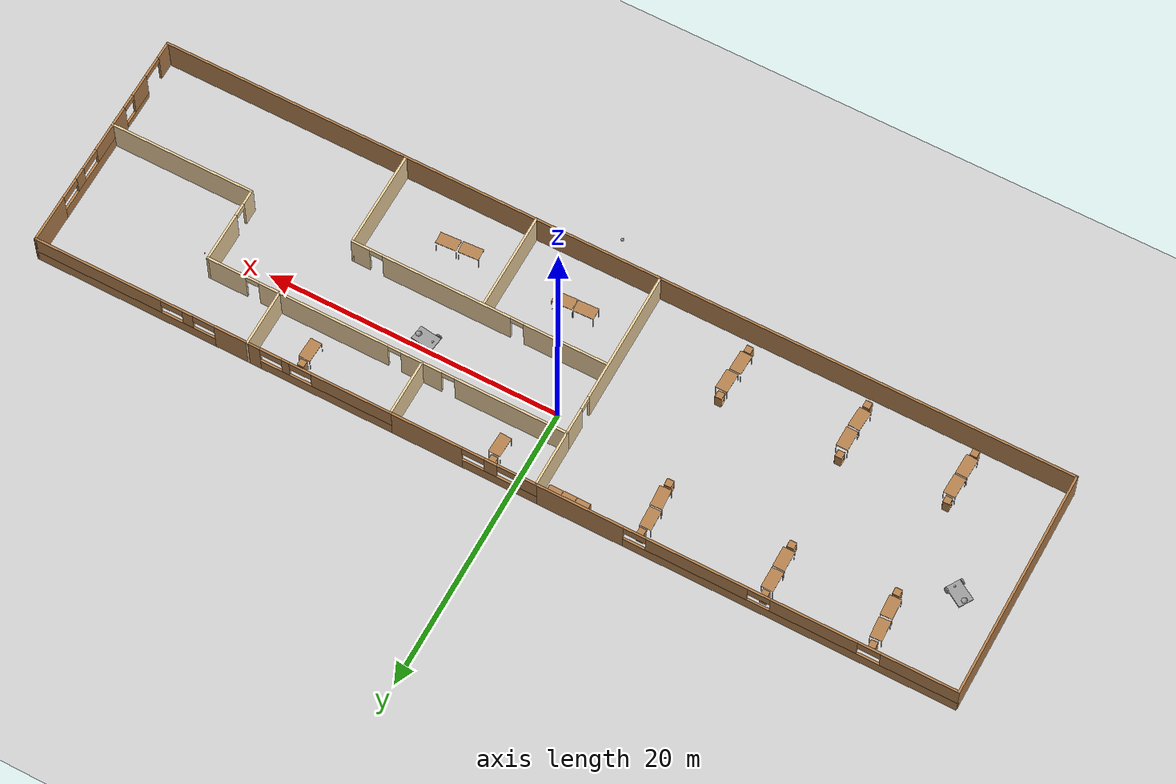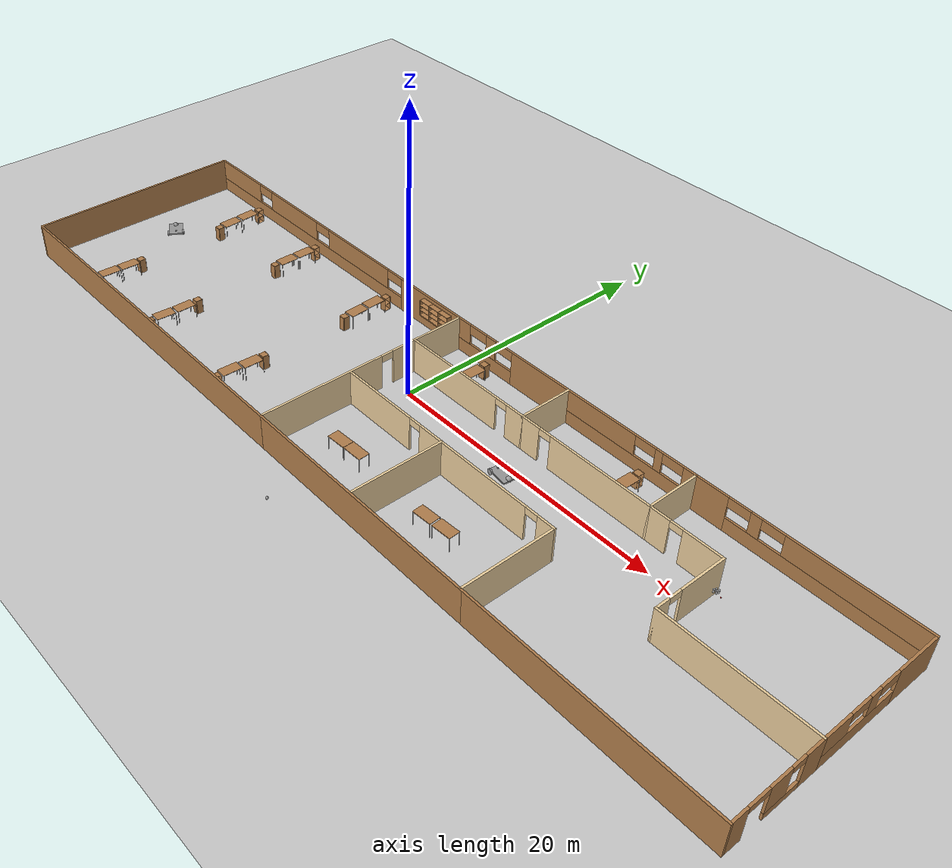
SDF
<sdf version="1.6">
 <world name="default">
  <plugin name="hello" filename="libhello.so"/>
  <light name="sun" type="directional">
   <pose>0 0 10 0 -0 0</pose>
   <diffuse>0.8 0.8 0.8 1</diffuse>
   <specular>0.2 0.2 0.2 1</specular>
   <attenuation>
    <range>1000</range>
    <constant>0.9</constant>
    <linear>0.01</linear>
    <quadratic>0.001</quadratic>
   </attenuation>
   <direction>-0.5 0.1 -0.9</direction>
  </light>
  <model name="ground_plane">
   <static>1</static>
   <link name="link">
    <collision name="collision">
     <geometry><plane><normal>0 0 1</normal><size>100 100</size></plane></geometry>
     <surface><friction><ode><mu>100</mu><mu2>50</mu2></ode></friction></surface>
    </collision>
    <visual name="visual">
     <cast_shadows>0</cast_shadows>
     <geometry><plane><normal>0 0 1</normal><size>100 100</size></plane></geometry>
     <material>
      <script><uri>file://media/materials/scripts/gazebo.material</uri><name>Gazebo/Grey</name></script>
     </material>
    </visual>
   </link>
  </model>
  <gravity>0 0 -9.8</gravity>
  <magnetic_field>6e-06 2.3e-05 -4.2e-05</magnetic_field>
  <atmosphere type="adiabatic"/>
  <physics name="default_physics" default="0" type="ode">
   <max_step_size>0.001</max_step_size>
   <real_time_factor>1</real_time_factor>
   <real_time_update_rate>1000</real_time_update_rate>
  </physics>
  <scene><ambient>0.4 0.4 0.4 1</ambient><background>0.7 0.7 0.7 1</background><shadows>1</shadows></scene>
  <spherical_coordinates>
   <surface_model>EARTH_WGS84</surface_model>
   <latitude_deg>0</latitude_deg>
   <longitude_deg>0</longitude_deg>
   <elevation>0</elevation>
   <heading_deg>0</heading_deg>
  </spherical_coordinates>
  <model name="mymodel_0">
   <pose>1.7436 -2.15546 0 0 -0 0</pose>
   <link name="Wall_119">
    <pose>21.35 1.375 0 0 0 -1.5708</pose>
    <visual name="Wall_119_Visual_0">
     <pose>-0.987502 0 1.25 0 -0 0</pose>
     <geometry><box><size>3.425 0.15 2.5</size></box></geometry>
     <material>
      <script><uri>file://media/materials/scripts/gazebo.material</uri><name>Gazebo/Grey</name></script>
      <ambient>0.921569 0.807843 0.615686 1</ambient>
     </material>
    </visual>
    <collision name="Wall_119_Collision_0">
     <geometry><box><size>3.425 0.15 2.5</size></box></geometry>
     <pose>-0.987502 0 1.25 0 -0 0</pose>
    </collision>
    <visual name="Wall_119_Visual_1">
     <pose>2.1625 0 1.25 0 -0 0</pose>
     <geometry><box><size>1.075 0.15 2.5</size></box></geometry>
     <material>
      <script><uri>file://media/materials/scripts/gazebo.material</uri><name>Gazebo/Grey</name></script>
      <ambient>0.921569 0.807843 0.615686 1</ambient>
     </material>
    </visual>
    <collision name="Wall_119_Collision_1">
     <geometry><box><size>1.075 0.15 2.5</size></box></geometry>
     <pose>2.1625 0 1.25 0 -0 0</pose>
    </collision>
    <visual name="Wall_119_Visual_2">
     <pose>1.175 0 2.25 0 -0 0</pose>
     <geometry><box><size>0.9 0.15 0.5</size></box></geometry>
     <material>
      <script><uri>file://media/materials/scripts/gazebo.material</uri><name>Gazebo/Grey</name></script>
      <ambient>0.921569 0.807843 0.615686 1</ambient>
     </material>
    </visual>
    <collision name="Wall_119_Collision_2">
     <geometry><box><size>0.9 0.15 0.5</size></box></geometry>
     <pose>1.175 0 2.25 0 -0 0</pose>
    </collision>
   </link>
   <link name="Wall_123">
    <collision name="Wall_123_Collision">
     <geometry><box><size>10 0.15 2.5</size></box></geometry>
     <pose>0 0 1.25 0 -0 0</pose>
    </collision>
    <visual name="Wall_123_Visual">
     <pose>0 0 1.25 0 -0 0</pose>
     <geometry><box><size>10 0.15 2.5</size></box></geometry>
     <material>
      <script><uri>file://media/materials/scripts/gazebo.material</uri><name>Gazebo/Grey</name></script>
      <ambient>0.921569 0.807843 0.615686 1</ambient>
     </material>
    </visual>
    <pose>26.275 -1.25 0 0 -0 0</pose>
   </link>
   <link name="Wall_125">
    <pose>1.575 7.85 0 0 -0 3.14159</pose>
    <visual name="Wall_125_Visual_0">
     <pose>-2.52053 0 1.25 0 -0 0</pose>
     <geometry><box><size>4.95895 0.15 2.5</size></box></geometry>
     <material>
      <script><uri>file://media/materials/scripts/gazebo.material</uri><name>Gazebo/Wood</name></script>
      <ambient>0.996078 0.47451 0.0196078 1</ambient>
     </material>
    </visual>
    <collision name="Wall_125_Collision_0">
     <geometry><box><size>4.95895 0.15 2.5</size></box></geometry>
     <pose>-2.52053 0 1.25 0 -0 0</pose>
    </collision>
    <visual name="Wall_125_Visual_1">
     <pose>2.47947 0 0.5 0 -0 0</pose>
     <geometry><box><size>5.04105 0.15 1</size></box></geometry>
     <material>
      <script><uri>file://media/materials/scripts/gazebo.material</uri><name>Gazebo/Wood</name></script>
      <ambient>0.996078 0.47451 0.0196078 1</ambient>
     </material>
    </visual>
    <collision name="Wall_125_Collision_1">
     <geometry><box><size>5.04105 0.15 1</size></box></geometry>
     <pose>2.47947 0 0.5 0 -0 0</pose>
    </collision>
    <visual name="Wall_125_Visual_2">
     <pose>1.88216 0 1.75 0 -0 0</pose>
     <geometry><box><size>0.846424 0.15 1.5</size></box></geometry>
     <material>
      <script><uri>file://media/materials/scripts/gazebo.material</uri><name>Gazebo/Wood</name></script>
      <ambient>0.996078 0.47451 0.0196078 1</ambient>
     </material>
    </visual>
    <collision name="Wall_125_Collision_2">
     <geometry><box><size>0.846424 0.15 1.5</size></box></geometry>
     <pose>1.88216 0 1.75 0 -0 0</pose>
    </collision>
    <visual name="Wall_125_Visual_3">
     <pose>4.40268 0 1.75 0 -0 0</pose>
     <geometry><box><size>1.19463 0.15 1.5</size></box></geometry>
     <material>
      <script><uri>file://media/materials/scripts/gazebo.material</uri><name>Gazebo/Wood</name></script>
      <ambient>0.996078 0.47451 0.0196078 1</ambient>
     </material>
    </visual>
    <collision name="Wall_125_Collision_3">
     <geometry><box><size>1.19463 0.15 1.5</size></box></geometry>
     <pose>4.40268 0 1.75 0 -0 0</pose>
    </collision>
    <visual name="Wall_125_Visual_4">
     <pose>0.708946 0 2.15 0 -0 0</pose>
     <geometry><box><size>1.5 0.15 0.7</size></box></geometry>
     <material>
      <script><uri>file://media/materials/scripts/gazebo.material</uri><name>Gazebo/Wood</name></script>
      <ambient>0.996078 0.47451 0.0196078 1</ambient>
     </material>
    </visual>
    <collision name="Wall_125_Collision_4">
     <geometry><box><size>1.5 0.15 0.7</size></box></geometry>
     <pose>0.708946 0 2.15 0 -0 0</pose>
    </collision>
    <visual name="Wall_125_Visual_5">
     <pose>3.05537 0 2.15 0 -0 0</pose>
     <geometry><box><size>1.5 0.15 0.7</size></box></geometry>
     <material>
      <script><uri>file://media/materials/scripts/gazebo.material</uri><name>Gazebo/Wood</name></script>
      <ambient>0.996078 0.47451 0.0196078 1</ambient>
     </material>
    </visual>
    <collision name="Wall_125_Collision_5">
     <geometry><box><size>1.5 0.15 0.7</size></box></geometry>
     <pose>3.05537 0 2.15 0 -0 0</pose>
    </collision>
   </link>
   <link name="Wall_127">
    <collision name="Wall_127_Collision">
     <geometry><box><size>4 0.15 2.5</size></box></geometry>
     <pose>0 0 1.25 0 -0 0</pose>
    </collision>
    <visual name="Wall_127_Visual">
     <pose>0 0 1.25 0 -0 0</pose>
     <geometry><box><size>4 0.15 2.5</size></box></geometry>
     <material>
      <script><uri>file://media/materials/scripts/gazebo.material</uri><name>Gazebo/Grey</name></script>
      <ambient>0.921569 0.807843 0.615686 1</ambient>
     </material>
    </visual>
    <pose>-3.35 5.925 0 0 0 -1.5708</pose>
   </link>
   <link name="Wall_129">
    <pose>1.575 4 0 0 -0 0</pose>
    <visual name="Wall_129_Visual_0">
     <pose>-1.15906 0 1.25 0 -0 0</pose>
     <geometry><box><size>7.68187 0.15 2.5</size></box></geometry>
     <material>
      <script><uri>file://media/materials/scripts/gazebo.material</uri><name>Gazebo/Grey</name></script>
      <ambient>0.921569 0.807843 0.615686 1</ambient>
     </material>
    </visual>
    <collision name="Wall_129_Collision_0">
     <geometry><box><size>7.68187 0.15 2.5</size></box></geometry>
     <pose>-1.15906 0 1.25 0 -0 0</pose>
    </collision>
    <visual name="Wall_129_Visual_1">
     <pose>4.29094 0 1.25 0 -0 0</pose>
     <geometry><box><size>1.41813 0.15 2.5</size></box></geometry>
     <material>
      <script><uri>file://media/materials/scripts/gazebo.material</uri><name>Gazebo/Grey</name></script>
      <ambient>0.921569 0.807843 0.615686 1</ambient>
     </material>
    </visual>
    <collision name="Wall_129_Collision_1">
     <geometry><box><size>1.41813 0.15 2.5</size></box></geometry>
     <pose>4.29094 0 1.25 0 -0 0</pose>
    </collision>
    <visual name="Wall_129_Visual_2">
     <pose>3.13187 0 2.25 0 -0 0</pose>
     <geometry><box><size>0.9 0.15 0.5</size></box></geometry>
     <material>
      <script><uri>file://media/materials/scripts/gazebo.material</uri><name>Gazebo/Grey</name></script>
      <ambient>0.921569 0.807843 0.615686 1</ambient>
     </material>
    </visual>
    <collision name="Wall_129_Collision_2">
     <geometry><box><size>0.9 0.15 0.5</size></box></geometry>
     <pose>3.13187 0 2.25 0 -0 0</pose>
    </collision>
   </link>
   <link name="Wall_144">
    <pose>-17.275 7.85 0 0 -0 3.14159</pose>
    <visual name="Wall_144_Visual_0">
     <pose>-11.0233 0 1.25 0 -0 0</pose>
     <geometry><box><size>5.95337 0.15 2.5</size></box></geometry>
     <material>
      <script><uri>file://media/materials/scripts/gazebo.material</uri><name>Gazebo/Wood</name></script>
      <ambient>0.996078 0.47451 0.0196078 1</ambient>
     </material>
    </visual>
    <collision name="Wall_144_Collision_0">
     <geometry><box><size>5.95337 0.15 2.5</size></box></geometry>
     <pose>-11.0233 0 1.25 0 -0 0</pose>
    </collision>
    <visual name="Wall_144_Visual_1">
     <pose>2.97669 0 0.5 0 -0 0</pose>
     <geometry><box><size>22.0466 0.15 1</size></box></geometry>
     <material>
      <script><uri>file://media/materials/scripts/gazebo.material</uri><name>Gazebo/Wood</name></script>
      <ambient>0.996078 0.47451 0.0196078 1</ambient>
     </material>
    </visual>
    <collision name="Wall_144_Collision_1">
     <geometry><box><size>22.0466 0.15 1</size></box></geometry>
     <pose>2.97669 0 0.5 0 -0 0</pose>
    </collision>
    <visual name="Wall_144_Visual_2">
     <pose>-3.18177 0 1.75 0 -0 0</pose>
     <geometry><box><size>6.72973 0.15 1.5</size></box></geometry>
     <material>
      <script><uri>file://media/materials/scripts/gazebo.material</uri><name>Gazebo/Wood</name></script>
      <ambient>0.996078 0.47451 0.0196078 1</ambient>
     </material>
    </visual>
    <collision name="Wall_144_Collision_2">
     <geometry><box><size>6.72973 0.15 1.5</size></box></geometry>
     <pose>-3.18177 0 1.75 0 -0 0</pose>
    </collision>
    <visual name="Wall_144_Visual_3">
     <pose>4.53578 0 1.75 0 -0 0</pose>
     <geometry><box><size>5.70537 0.15 1.5</size></box></geometry>
     <material>
      <script><uri>file://media/materials/scripts/gazebo.material</uri><name>Gazebo/Wood</name></script>
      <ambient>0.996078 0.47451 0.0196078 1</ambient>
     </material>
    </visual>
    <collision name="Wall_144_Collision_3">
     <geometry><box><size>5.70537 0.15 1.5</size></box></geometry>
     <pose>4.53578 0 1.75 0 -0 0</pose>
    </collision>
    <visual name="Wall_144_Visual_4">
     <pose>11.4442 0 1.75 0 -0 0</pose>
     <geometry><box><size>5.11153 0.15 1.5</size></box></geometry>
     <material>
      <script><uri>file://media/materials/scripts/gazebo.material</uri><name>Gazebo/Wood</name></script>
      <ambient>0.996078 0.47451 0.0196078 1</ambient>
     </material>
    </visual>
    <collision name="Wall_144_Collision_4">
     <geometry><box><size>5.11153 0.15 1.5</size></box></geometry>
     <pose>11.4442 0 1.75 0 -0 0</pose>
    </collision>
    <visual name="Wall_144_Visual_5">
     <pose>-7.29663 0 2.15 0 -0 0</pose>
     <geometry><box><size>1.5 0.15 0.7</size></box></geometry>
     <material>
      <script><uri>file://media/materials/scripts/gazebo.material</uri><name>Gazebo/Wood</name></script>
      <ambient>0.996078 0.47451 0.0196078 1</ambient>
     </material>
    </visual>
    <collision name="Wall_144_Collision_5">
     <geometry><box><size>1.5 0.15 0.7</size></box></geometry>
     <pose>-7.29663 0 2.15 0 -0 0</pose>
    </collision>
    <visual name="Wall_144_Visual_6">
     <pose>0.933096 0 2.15 0 -0 0</pose>
     <geometry><box><size>1.5 0.15 0.7</size></box></geometry>
     <material>
      <script><uri>file://media/materials/scripts/gazebo.material</uri><name>Gazebo/Wood</name></script>
      <ambient>0.996078 0.47451 0.0196078 1</ambient>
     </material>
    </visual>
    <collision name="Wall_144_Collision_6">
     <geometry><box><size>1.5 0.15 0.7</size></box></geometry>
     <pose>0.933096 0 2.15 0 -0 0</pose>
    </collision>
    <visual name="Wall_144_Visual_7">
     <pose>8.13847 0 2.15 0 -0 0</pose>
     <geometry><box><size>1.5 0.15 0.7</size></box></geometry>
     <material>
      <script><uri>file://media/materials/scripts/gazebo.material</uri><name>Gazebo/Wood</name></script>
      <ambient>0.996078 0.47451 0.0196078 1</ambient>
     </material>
    </visual>
    <collision name="Wall_144_Collision_7">
     <geometry><box><size>1.5 0.15 0.7</size></box></geometry>
     <pose>8.13847 0 2.15 0 -0 0</pose>
    </collision>
   </link>
   <link name="Wall_145">
    <collision name="Wall_145_Collision">
     <geometry><box><size>15.85 0.15 2.5</size></box></geometry>
     <pose>0 0 1.25 0 -0 0</pose>
    </collision>
    <visual name="Wall_145_Visual">
     <pose>0 0 1.25 0 -0 0</pose>
     <geometry><box><size>15.85 0.15 2.5</size></box></geometry>
     <material>
      <script><uri>file://media/materials/scripts/gazebo.material</uri><name>Gazebo/Wood</name></script>
      <ambient>0.996078 0.47451 0.0196078 1</ambient>
     </material>
    </visual>
    <pose>-31.2 0 0 0 0 -1.5708</pose>
   </link>
   <link name="Wall_148">
    <pose>-3.35 -1.925 0 0 0 -1.5708</pose>
    <visual name="Wall_148_Visual_0">
     <pose>-5.0473 0 1.25 0 -0 0</pose>
     <geometry><box><size>1.90541 0.15 2.5</size></box></geometry>
     <material>
      <script><uri>file://media/materials/scripts/gazebo.material</uri><name>Gazebo/Grey</name></script>
      <ambient>0.921569 0.807843 0.615686 1</ambient>
     </material>
    </visual>
    <collision name="Wall_148_Collision_0">
     <geometry><box><size>1.90541 0.15 2.5</size></box></geometry>
     <pose>-5.0473 0 1.25 0 -0 0</pose>
    </collision>
    <visual name="Wall_148_Visual_1">
     <pose>1.4027 0 1.25 0 -0 0</pose>
     <geometry><box><size>9.19459 0.15 2.5</size></box></geometry>
     <material>
      <script><uri>file://media/materials/scripts/gazebo.material</uri><name>Gazebo/Grey</name></script>
      <ambient>0.921569 0.807843 0.615686 1</ambient>
     </material>
    </visual>
    <collision name="Wall_148_Collision_1">
     <geometry><box><size>9.19459 0.15 2.5</size></box></geometry>
     <pose>1.4027 0 1.25 0 -0 0</pose>
    </collision>
    <visual name="Wall_148_Visual_2">
     <pose>-3.64459 0 2.25 0 -0 0</pose>
     <geometry><box><size>0.9 0.15 0.5</size></box></geometry>
     <material>
      <script><uri>file://media/materials/scripts/gazebo.material</uri><name>Gazebo/Grey</name></script>
      <ambient>0.921569 0.807843 0.615686 1</ambient>
     </material>
    </visual>
    <collision name="Wall_148_Collision_2">
     <geometry><box><size>0.9 0.15 0.5</size></box></geometry>
     <pose>-3.64459 0 2.25 0 -0 0</pose>
    </collision>
   </link>
   <link name="Wall_160">
    <pose>5.52431 -1.18597 0 0 0 -3e-06</pose>
    <visual name="Wall_160_Visual_0">
     <pose>-5.96657 0 1.25 0 -0 0</pose>
     <geometry><box><size>5.67479 0.15 2.5</size></box></geometry>
     <material>
      <script><uri>file://media/materials/scripts/gazebo.material</uri><name>Gazebo/Grey</name></script>
      <ambient>0.921569 0.807843 0.615686 1</ambient>
     </material>
    </visual>
    <collision name="Wall_160_Collision_0">
     <geometry><box><size>5.67479 0.15 2.5</size></box></geometry>
     <pose>-5.96657 0 1.25 0 -0 0</pose>
    </collision>
    <visual name="Wall_160_Visual_1">
     <pose>2.18678 0 1.25 0 -0 0</pose>
     <geometry><box><size>8.83193 0.15 2.5</size></box></geometry>
     <material>
      <script><uri>file://media/materials/scripts/gazebo.material</uri><name>Gazebo/Grey</name></script>
      <ambient>0.921569 0.807843 0.615686 1</ambient>
     </material>
    </visual>
    <collision name="Wall_160_Collision_1">
     <geometry><box><size>8.83193 0.15 2.5</size></box></geometry>
     <pose>2.18678 0 1.25 0 -0 0</pose>
    </collision>
    <visual name="Wall_160_Visual_2">
     <pose>8.15336 0 1.25 0 -0 0</pose>
     <geometry><box><size>1.30122 0.15 2.5</size></box></geometry>
     <material>
      <script><uri>file://media/materials/scripts/gazebo.material</uri><name>Gazebo/Grey</name></script>
      <ambient>0.921569 0.807843 0.615686 1</ambient>
     </material>
    </visual>
    <collision name="Wall_160_Collision_2">
     <geometry><box><size>1.30122 0.15 2.5</size></box></geometry>
     <pose>8.15336 0 1.25 0 -0 0</pose>
    </collision>
    <visual name="Wall_160_Visual_3">
     <pose>-2.67918 0 2.25 0 -0 0</pose>
     <geometry><box><size>0.9 0.15 0.5</size></box></geometry>
     <material>
      <script><uri>file://media/materials/scripts/gazebo.material</uri><name>Gazebo/Grey</name></script>
      <ambient>0.921569 0.807843 0.615686 1</ambient>
     </material>
    </visual>
    <collision name="Wall_160_Collision_3">
     <geometry><box><size>0.9 0.15 0.5</size></box></geometry>
     <pose>-2.67918 0 2.25 0 -0 0</pose>
    </collision>
    <visual name="Wall_160_Visual_4">
     <pose>7.05275 0 2.25 0 -0 0</pose>
     <geometry><box><size>0.9 0.15 0.5</size></box></geometry>
     <material>
      <script><uri>file://media/materials/scripts/gazebo.material</uri><name>Gazebo/Grey</name></script>
      <ambient>0.921569 0.807843 0.615686 1</ambient>
     </material>
    </visual>
    <collision name="Wall_160_Collision_4">
     <geometry><box><size>0.9 0.15 0.5</size></box></geometry>
     <pose>7.05275 0 2.25 0 -0 0</pose>
    </collision>
   </link>
   <link name="Wall_166">
    <pose>31.2 -4.55 0 0 0 -1.5708</pose>
    <visual name="Wall_166_Visual_0">
     <pose>-2.6617 0 1.25 0 -0 0</pose>
     <geometry><box><size>1.4266 0.15 2.5</size></box></geometry>
     <material>
      <script><uri>file://media/materials/scripts/gazebo.material</uri><name>Gazebo/Wood</name></script>
      <ambient>0.996078 0.47451 0.0196078 1</ambient>
     </material>
    </visual>
    <collision name="Wall_166_Collision_0">
     <geometry><box><size>1.4266 0.15 2.5</size></box></geometry>
     <pose>-2.6617 0 1.25 0 -0 0</pose>
    </collision>
    <visual name="Wall_166_Visual_1">
     <pose>2.74194 0 1.25 0 -0 0</pose>
     <geometry><box><size>1.26611 0.15 2.5</size></box></geometry>
     <material>
      <script><uri>file://media/materials/scripts/gazebo.material</uri><name>Gazebo/Wood</name></script>
      <ambient>0.996078 0.47451 0.0196078 1</ambient>
     </material>
    </visual>
    <collision name="Wall_166_Collision_1">
     <geometry><box><size>1.26611 0.15 2.5</size></box></geometry>
     <pose>2.74194 0 1.25 0 -0 0</pose>
    </collision>
    <visual name="Wall_166_Visual_2">
     <pose>-0.669753 0 0.25 0 -0 0</pose>
     <geometry><box><size>2.55729 0.15 0.5</size></box></geometry>
     <material>
      <script><uri>file://media/materials/scripts/gazebo.material</uri><name>Gazebo/Wood</name></script>
      <ambient>0.996078 0.47451 0.0196078 1</ambient>
     </material>
    </visual>
    <collision name="Wall_166_Collision_2">
     <geometry><box><size>2.55729 0.15 0.5</size></box></geometry>
     <pose>-0.669753 0 0.25 0 -0 0</pose>
    </collision>
    <visual name="Wall_166_Visual_3">
     <pose>-0.169753 0 1.5 0 -0 0</pose>
     <geometry><box><size>1.55729 0.15 2</size></box></geometry>
     <material>
      <script><uri>file://media/materials/scripts/gazebo.material</uri><name>Gazebo/Wood</name></script>
      <ambient>0.996078 0.47451 0.0196078 1</ambient>
     </material>
    </visual>
    <collision name="Wall_166_Collision_3">
     <geometry><box><size>1.55729 0.15 2</size></box></geometry>
     <pose>-0.169753 0 1.5 0 -0 0</pose>
    </collision>
    <visual name="Wall_166_Visual_4">
     <pose>-1.4484 0 2.25 0 -0 0</pose>
     <geometry><box><size>1 0.15 0.5</size></box></geometry>
     <material>
      <script><uri>file://media/materials/scripts/gazebo.material</uri><name>Gazebo/Wood</name></script>
      <ambient>0.996078 0.47451 0.0196078 1</ambient>
     </material>
    </visual>
    <collision name="Wall_166_Collision_4">
     <geometry><box><size>1 0.15 0.5</size></box></geometry>
     <pose>-1.4484 0 2.25 0 -0 0</pose>
    </collision>
    <visual name="Wall_166_Visual_5">
     <pose>1.35889 0 2.25 0 -0 0</pose>
     <geometry><box><size>1.5 0.15 0.5</size></box></geometry>
     <material>
      <script><uri>file://media/materials/scripts/gazebo.material</uri><name>Gazebo/Wood</name></script>
      <ambient>0.996078 0.47451 0.0196078 1</ambient>
     </material>
    </visual>
    <collision name="Wall_166_Collision_5">
     <geometry><box><size>1.5 0.15 0.5</size></box></geometry>
     <pose>1.35889 0 2.25 0 -0 0</pose>
    </collision>
   </link>
   <link name="Wall_170">
    <collision name="Wall_170_Collision">
     <geometry><box><size>6.814 0.15 2.5</size></box></geometry>
     <pose>0 0 1.25 0 -0 0</pose>
    </collision>
    <visual name="Wall_170_Visual">
     <pose>0 0 1.25 0 -0 0</pose>
     <geometry><box><size>6.814 0.15 2.5</size></box></geometry>
     <material>
      <script><uri>file://media/materials/scripts/gazebo.material</uri><name>Gazebo/Grey</name></script>
      <ambient>0.921569 0.807843 0.615686 1</ambient>
     </material>
    </visual>
    <pose>14.253 -4.518 0 0 0 -1.5708</pose>
   </link>
   <link name="Wall_173">
    <collision name="Wall_173_Collision">
     <geometry><box><size>17 0.15 2.5</size></box></geometry>
     <pose>0 0 1.25 0 -0 0</pose>
    </collision>
    <visual name="Wall_173_Visual">
     <pose>0 0 1.25 0 -0 0</pose>
     <geometry><box><size>17 0.15 2.5</size></box></geometry>
     <material>
      <script><uri>file://media/materials/scripts/gazebo.material</uri><name>Gazebo/Wood</name></script>
      <ambient>0.996078 0.47451 0.0196078 1</ambient>
     </material>
    </visual>
    <pose>22.775 -7.85 0 0 -0 3.14159</pose>
   </link>
   <link name="Wall_174">
    <collision name="Wall_174_Collision">
     <geometry><box><size>17.85 0.15 2.5</size></box></geometry>
     <pose>0 0 1.25 0 -0 0</pose>
    </collision>
    <visual name="Wall_174_Visual">
     <pose>0 0 1.25 0 -0 0</pose>
     <geometry><box><size>17.85 0.15 2.5</size></box></geometry>
     <material>
      <script><uri>file://media/materials/scripts/gazebo.material</uri><name>Gazebo/Wood</name></script>
      <ambient>0.996078 0.47451 0.0196078 1</ambient>
     </material>
    </visual>
    <pose>5.5 -7.85 0 0 -0 3.14159</pose>
   </link>
   <link name="Wall_175">
    <collision name="Wall_175_Collision">
     <geometry><box><size>28 0.15 2.5</size></box></geometry>
     <pose>0 0 1.25 0 -0 0</pose>
    </collision>
    <visual name="Wall_175_Visual">
     <pose>0 0 1.25 0 -0 0</pose>
     <geometry><box><size>28 0.15 2.5</size></box></geometry>
     <material>
      <script><uri>file://media/materials/scripts/gazebo.material</uri><name>Gazebo/Wood</name></script>
      <ambient>0.996078 0.47451 0.0196078 1</ambient>
     </material>
    </visual>
    <pose>-17.275 -7.85 0 0 -0 3.14159</pose>
   </link>
   <link name="Wall_177">
    <collision name="Wall_177_Collision">
     <geometry><box><size>6.75 0.15 2.5</size></box></geometry>
     <pose>0 0 1.25 0 -0 0</pose>
    </collision>
    <visual name="Wall_177_Visual">
     <pose>0 0 1.25 0 -0 0</pose>
     <geometry><box><size>6.75 0.15 2.5</size></box></geometry>
     <material>
      <script><uri>file://media/materials/scripts/gazebo.material</uri><name>Gazebo/Grey</name></script>
      <ambient>0.921569 0.807843 0.615686 1</ambient>
     </material>
    </visual>
    <pose>5.18454 -4.51051 0 0 0 -1.5708</pose>
   </link>
   <link name="Wall_29">
    <pose>23.775 7.85 0 0 -0 0</pose>
    <visual name="Wall_29_Visual_0">
     <pose>-6.31514 0 1.25 0 -0 0</pose>
     <geometry><box><size>2.36971 0.15 2.5</size></box></geometry>
     <material>
      <script><uri>file://media/materials/scripts/gazebo.material</uri><name>Gazebo/Wood</name></script>
      <ambient>0.996078 0.47451 0.0196078 1</ambient>
     </material>
    </visual>
    <collision name="Wall_29_Collision_0">
     <geometry><box><size>2.36971 0.15 2.5</size></box></geometry>
     <pose>-6.31514 0 1.25 0 -0 0</pose>
    </collision>
    <visual name="Wall_29_Visual_1">
     <pose>1.18486 0 0.5 0 -0 0</pose>
     <geometry><box><size>12.6303 0.15 1</size></box></geometry>
     <material>
      <script><uri>file://media/materials/scripts/gazebo.material</uri><name>Gazebo/Wood</name></script>
      <ambient>0.996078 0.47451 0.0196078 1</ambient>
     </material>
    </visual>
    <collision name="Wall_29_Collision_1">
     <geometry><box><size>12.6303 0.15 1</size></box></geometry>
     <pose>1.18486 0 0.5 0 -0 0</pose>
    </collision>
    <visual name="Wall_29_Visual_2">
     <pose>-3.26225 0 1.75 0 -0 0</pose>
     <geometry><box><size>0.736064 0.15 1.5</size></box></geometry>
     <material>
      <script><uri>file://media/materials/scripts/gazebo.material</uri><name>Gazebo/Wood</name></script>
      <ambient>0.996078 0.47451 0.0196078 1</ambient>
     </material>
    </visual>
    <collision name="Wall_29_Collision_2">
     <geometry><box><size>0.736064 0.15 1.5</size></box></geometry>
     <pose>-3.26225 0 1.75 0 -0 0</pose>
    </collision>
    <visual name="Wall_29_Visual_3">
     <pose>3.05289 0 1.75 0 -0 0</pose>
     <geometry><box><size>8.89422 0.15 1.5</size></box></geometry>
     <material>
      <script><uri>file://media/materials/scripts/gazebo.material</uri><name>Gazebo/Wood</name></script>
      <ambient>0.996078 0.47451 0.0196078 1</ambient>
     </material>
    </visual>
    <collision name="Wall_29_Collision_3">
     <geometry><box><size>8.89422 0.15 1.5</size></box></geometry>
     <pose>3.05289 0 1.75 0 -0 0</pose>
    </collision>
    <visual name="Wall_29_Visual_4">
     <pose>-4.38029 0 2.15 0 -0 0</pose>
     <geometry><box><size>1.5 0.15 0.7</size></box></geometry>
     <material>
      <script><uri>file://media/materials/scripts/gazebo.material</uri><name>Gazebo/Wood</name></script>
      <ambient>0.996078 0.47451 0.0196078 1</ambient>
     </material>
    </visual>
    <collision name="Wall_29_Collision_4">
     <geometry><box><size>1.5 0.15 0.7</size></box></geometry>
     <pose>-4.38029 0 2.15 0 -0 0</pose>
    </collision>
    <visual name="Wall_29_Visual_5">
     <pose>-2.14422 0 2.15 0 -0 0</pose>
     <geometry><box><size>1.5 0.15 0.7</size></box></geometry>
     <material>
      <script><uri>file://media/materials/scripts/gazebo.material</uri><name>Gazebo/Wood</name></script>
      <ambient>0.996078 0.47451 0.0196078 1</ambient>
     </material>
    </visual>
    <collision name="Wall_29_Collision_5">
     <geometry><box><size>1.5 0.15 0.7</size></box></geometry>
     <pose>-2.14422 0 2.15 0 -0 0</pose>
    </collision>
   </link>
   <link name="Wall_31">
    <pose>31.2 3.3 0 0 0 -1.5708</pose>
    <visual name="Wall_31_Visual_0">
     <pose>-2.97432 0 1.25 0 -0 0</pose>
     <geometry><box><size>3.30136 0.15 2.5</size></box></geometry>
     <material>
      <script><uri>file://media/materials/scripts/gazebo.material</uri><name>Gazebo/Wood</name></script>
      <ambient>0.996078 0.47451 0.0196078 1</ambient>
     </material>
    </visual>
    <collision name="Wall_31_Collision_0">
     <geometry><box><size>3.30136 0.15 2.5</size></box></geometry>
     <pose>-2.97432 0 1.25 0 -0 0</pose>
    </collision>
    <visual name="Wall_31_Visual_1">
     <pose>1.65068 0 0.5 0 -0 0</pose>
     <geometry><box><size>5.94864 0.15 1</size></box></geometry>
     <material>
      <script><uri>file://media/materials/scripts/gazebo.material</uri><name>Gazebo/Wood</name></script>
      <ambient>0.996078 0.47451 0.0196078 1</ambient>
     </material>
    </visual>
    <collision name="Wall_31_Collision_1">
     <geometry><box><size>5.94864 0.15 1</size></box></geometry>
     <pose>1.65068 0 0.5 0 -0 0</pose>
    </collision>
    <visual name="Wall_31_Visual_2">
     <pose>0.58726 0 1.75 0 -0 0</pose>
     <geometry><box><size>0.821797 0.15 1.5</size></box></geometry>
     <material>
      <script><uri>file://media/materials/scripts/gazebo.material</uri><name>Gazebo/Wood</name></script>
      <ambient>0.996078 0.47451 0.0196078 1</ambient>
     </material>
    </visual>
    <collision name="Wall_31_Collision_2">
     <geometry><box><size>0.821797 0.15 1.5</size></box></geometry>
     <pose>0.58726 0 1.75 0 -0 0</pose>
    </collision>
    <visual name="Wall_31_Visual_3">
     <pose>3.56158 0 1.75 0 -0 0</pose>
     <geometry><box><size>2.12684 0.15 1.5</size></box></geometry>
     <material>
      <script><uri>file://media/materials/scripts/gazebo.material</uri><name>Gazebo/Wood</name></script>
      <ambient>0.996078 0.47451 0.0196078 1</ambient>
     </material>
    </visual>
    <collision name="Wall_31_Collision_3">
     <geometry><box><size>2.12684 0.15 1.5</size></box></geometry>
     <pose>3.56158 0 1.75 0 -0 0</pose>
    </collision>
    <visual name="Wall_31_Visual_4">
     <pose>-0.573638 0 2.15 0 -0 0</pose>
     <geometry><box><size>1.5 0.15 0.7</size></box></geometry>
     <material>
      <script><uri>file://media/materials/scripts/gazebo.material</uri><name>Gazebo/Wood</name></script>
      <ambient>0.996078 0.47451 0.0196078 1</ambient>
     </material>
    </visual>
    <collision name="Wall_31_Collision_4">
     <geometry><box><size>1.5 0.15 0.7</size></box></geometry>
     <pose>-0.573638 0 2.15 0 -0 0</pose>
    </collision>
    <visual name="Wall_31_Visual_5">
     <pose>1.74816 0 2.15 0 -0 0</pose>
     <geometry><box><size>1.5 0.15 0.7</size></box></geometry>
     <material>
      <script><uri>file://media/materials/scripts/gazebo.material</uri><name>Gazebo/Wood</name></script>
      <ambient>0.996078 0.47451 0.0196078 1</ambient>
     </material>
    </visual>
    <collision name="Wall_31_Collision_5">
     <geometry><box><size>1.5 0.15 0.7</size></box></geometry>
     <pose>1.74816 0 2.15 0 -0 0</pose>
    </collision>
   </link>
   <link name="Wall_44">
    <pose>11.425 7.85 0 0 -0 3.14159</pose>
    <visual name="Wall_44_Visual_0">
     <pose>-4.52844 0 1.25 0 -0 0</pose>
     <geometry><box><size>0.943112 0.15 2.5</size></box></geometry>
     <material>
      <script><uri>file://media/materials/scripts/gazebo.material</uri><name>Gazebo/Wood</name></script>
      <ambient>0.996078 0.47451 0.0196078 1</ambient>
     </material>
    </visual>
    <collision name="Wall_44_Collision_0">
     <geometry><box><size>0.943112 0.15 2.5</size></box></geometry>
     <pose>-4.52844 0 1.25 0 -0 0</pose>
    </collision>
    <visual name="Wall_44_Visual_1">
     <pose>0.471556 0 0.5 0 -0 0</pose>
     <geometry><box><size>9.05689 0.15 1</size></box></geometry>
     <material>
      <script><uri>file://media/materials/scripts/gazebo.material</uri><name>Gazebo/Wood</name></script>
      <ambient>0.996078 0.47451 0.0196078 1</ambient>
     </material>
    </visual>
    <collision name="Wall_44_Collision_1">
     <geometry><box><size>9.05689 0.15 1</size></box></geometry>
     <pose>0.471556 0 0.5 0 -0 0</pose>
    </collision>
    <visual name="Wall_44_Visual_2">
     <pose>-2.28802 0 1.75 0 -0 0</pose>
     <geometry><box><size>0.537745 0.15 1.5</size></box></geometry>
     <material>
      <script><uri>file://media/materials/scripts/gazebo.material</uri><name>Gazebo/Wood</name></script>
      <ambient>0.996078 0.47451 0.0196078 1</ambient>
     </material>
    </visual>
    <collision name="Wall_44_Collision_2">
     <geometry><box><size>0.537745 0.15 1.5</size></box></geometry>
     <pose>-2.28802 0 1.75 0 -0 0</pose>
    </collision>
    <visual name="Wall_44_Visual_3">
     <pose>2.24043 0 1.75 0 -0 0</pose>
     <geometry><box><size>5.51914 0.15 1.5</size></box></geometry>
     <material>
      <script><uri>file://media/materials/scripts/gazebo.material</uri><name>Gazebo/Wood</name></script>
      <ambient>0.996078 0.47451 0.0196078 1</ambient>
     </material>
    </visual>
    <collision name="Wall_44_Collision_3">
     <geometry><box><size>5.51914 0.15 1.5</size></box></geometry>
     <pose>2.24043 0 1.75 0 -0 0</pose>
    </collision>
    <visual name="Wall_44_Visual_4">
     <pose>-3.30689 0 2.15 0 -0 0</pose>
     <geometry><box><size>1.5 0.15 0.7</size></box></geometry>
     <material>
      <script><uri>file://media/materials/scripts/gazebo.material</uri><name>Gazebo/Wood</name></script>
      <ambient>0.996078 0.47451 0.0196078 1</ambient>
     </material>
    </visual>
    <collision name="Wall_44_Collision_4">
     <geometry><box><size>1.5 0.15 0.7</size></box></geometry>
     <pose>-3.30689 0 2.15 0 -0 0</pose>
    </collision>
    <visual name="Wall_44_Visual_5">
     <pose>-1.26914 0 2.15 0 -0 0</pose>
     <geometry><box><size>1.5 0.15 0.7</size></box></geometry>
     <material>
      <script><uri>file://media/materials/scripts/gazebo.material</uri><name>Gazebo/Wood</name></script>
      <ambient>0.996078 0.47451 0.0196078 1</ambient>
     </material>
    </visual>
    <collision name="Wall_44_Collision_5">
     <geometry><box><size>1.5 0.15 0.7</size></box></geometry>
     <pose>-1.26914 0 2.15 0 -0 0</pose>
    </collision>
   </link>
   <link name="Wall_45">
    <collision name="Wall_45_Collision">
     <geometry><box><size>4 0.15 2.5</size></box></geometry>
     <pose>0 0 1.25 0 -0 0</pose>
    </collision>
    <visual name="Wall_45_Visual">
     <pose>0 0 1.25 0 -0 0</pose>
     <geometry><box><size>4 0.15 2.5</size></box></geometry>
     <material>
      <script><uri>file://media/materials/scripts/gazebo.material</uri><name>Gazebo/Grey</name></script>
      <ambient>0.921569 0.807843 0.615686 1</ambient>
     </material>
    </visual>
    <pose>6.5 5.925 0 0 0 -1.5708</pose>
   </link>
   <link name="Wall_80">
    <pose>11.425 4 0 0 -0 0</pose>
    <visual name="Wall_80_Visual_0">
     <pose>-4.24375 0 1.25 0 -0 0</pose>
     <geometry><box><size>1.51249 0.15 2.5</size></box></geometry>
     <material>
      <script><uri>file://media/materials/scripts/gazebo.material</uri><name>Gazebo/Grey</name></script>
      <ambient>0.921569 0.807843 0.615686 1</ambient>
     </material>
    </visual>
    <collision name="Wall_80_Collision_0">
     <geometry><box><size>1.51249 0.15 2.5</size></box></geometry>
     <pose>-4.24375 0 1.25 0 -0 0</pose>
    </collision>
    <visual name="Wall_80_Visual_1">
     <pose>1.20625 0 1.25 0 -0 0</pose>
     <geometry><box><size>7.58751 0.15 2.5</size></box></geometry>
     <material>
      <script><uri>file://media/materials/scripts/gazebo.material</uri><name>Gazebo/Grey</name></script>
      <ambient>0.921569 0.807843 0.615686 1</ambient>
     </material>
    </visual>
    <collision name="Wall_80_Collision_1">
     <geometry><box><size>7.58751 0.15 2.5</size></box></geometry>
     <pose>1.20625 0 1.25 0 -0 0</pose>
    </collision>
    <visual name="Wall_80_Visual_2">
     <pose>-3.03751 0 2.25 0 -0 0</pose>
     <geometry><box><size>0.9 0.15 0.5</size></box></geometry>
     <material>
      <script><uri>file://media/materials/scripts/gazebo.material</uri><name>Gazebo/Grey</name></script>
      <ambient>0.921569 0.807843 0.615686 1</ambient>
     </material>
    </visual>
    <collision name="Wall_80_Collision_2">
     <geometry><box><size>0.9 0.15 0.5</size></box></geometry>
     <pose>-3.03751 0 2.25 0 -0 0</pose>
    </collision>
   </link>
   <link name="Wall_81">
    <collision name="Wall_81_Collision">
     <geometry><box><size>4 0.15 2.5</size></box></geometry>
     <pose>0 0 1.25 0 -0 0</pose>
    </collision>
    <visual name="Wall_81_Visual">
     <pose>0 0 1.25 0 -0 0</pose>
     <geometry><box><size>4 0.15 2.5</size></box></geometry>
     <material>
      <script><uri>file://media/materials/scripts/gazebo.material</uri><name>Gazebo/Grey</name></script>
      <ambient>0.921569 0.807843 0.615686 1</ambient>
     </material>
    </visual>
    <pose>16.35 5.925 0 0 -0 1.5708</pose>
   </link>
   <link name="Wall_83">
    <pose>18.85 4 0 0 -0 0</pose>
    <visual name="Wall_83_Visual_0">
     <pose>-1.81995 0 1.25 0 -0 0</pose>
     <geometry><box><size>1.5101 0.15 2.5</size></box></geometry>
     <material>
      <script><uri>file://media/materials/scripts/gazebo.material</uri><name>Gazebo/Grey</name></script>
      <ambient>0.921569 0.807843 0.615686 1</ambient>
     </material>
    </visual>
    <collision name="Wall_83_Collision_0">
     <geometry><box><size>1.5101 0.15 2.5</size></box></geometry>
     <pose>-1.81995 0 1.25 0 -0 0</pose>
    </collision>
    <visual name="Wall_83_Visual_1">
     <pose>1.20505 0 1.25 0 -0 0</pose>
     <geometry><box><size>2.7399 0.15 2.5</size></box></geometry>
     <material>
      <script><uri>file://media/materials/scripts/gazebo.material</uri><name>Gazebo/Grey</name></script>
      <ambient>0.921569 0.807843 0.615686 1</ambient>
     </material>
    </visual>
    <collision name="Wall_83_Collision_1">
     <geometry><box><size>2.7399 0.15 2.5</size></box></geometry>
     <pose>1.20505 0 1.25 0 -0 0</pose>
    </collision>
    <visual name="Wall_83_Visual_2">
     <pose>-0.614896 0 2.25 0 -0 0</pose>
     <geometry><box><size>0.9 0.15 0.5</size></box></geometry>
     <material>
      <script><uri>file://media/materials/scripts/gazebo.material</uri><name>Gazebo/Grey</name></script>
      <ambient>0.921569 0.807843 0.615686 1</ambient>
     </material>
    </visual>
    <collision name="Wall_83_Collision_2">
     <geometry><box><size>0.9 0.15 0.5</size></box></geometry>
     <pose>-0.614896 0 2.25 0 -0 0</pose>
    </collision>
   </link>
   <static>1</static>
  </model>
  <model name="bookshelf_0">
   <static>1</static>
   <link name="bookshelf_0::bookshelf_0::link">
    <inertial><mass>1</mass></inertial>
    <collision name="back">
     <pose>0 0.005 0.6 0 -0 0</pose>
     <geometry><box><size>0.9 0.01 1.2</size></box></geometry>
    </collision>
    <visual name="visual1">
     <pose>0 0.005 0.6 0 -0 0</pose>
     <geometry><box><size>0.9 0.01 1.2</size></box></geometry>
     <material>
      <script><uri>file://media/materials/scripts/gazebo.material</uri><name>Gazebo/Wood</name></script>
     </material>
    </visual>
    <collision name="left_side">
     <pose>0.45 -0.195 0.6 0 -0 0</pose>
     <geometry><box><size>0.02 0.4 1.2</size></box></geometry>
    </collision>
    <visual name="visual2">
     <pose>0.45 -0.195 0.6 0 -0 0</pose>
     <geometry><box><size>0.02 0.4 1.2</size></box></geometry>
     <material>
      <script><uri>file://media/materials/scripts/gazebo.material</uri><name>Gazebo/Wood</name></script>
     </material>
    </visual>
    <collision name="right_side">
     <pose>-0.45 -0.195 0.6 0 -0 0</pose>
     <geometry><box><size>0.02 0.4 1.2</size></box></geometry>
    </collision>
    <visual name="visual3">
     <pose>-0.45 -0.195 0.6 0 -0 0</pose>
     <geometry><box><size>0.02 0.4 1.2</size></box></geometry>
     <material>
      <script><uri>file://media/materials/scripts/gazebo.material</uri><name>Gazebo/Wood</name></script>
     </material>
    </visual>
    <collision name="bottom">
     <pose>0 -0.195 0.03 0 -0 0</pose>
     <geometry><box><size>0.88 0.4 0.06</size></box></geometry>
    </collision>
    <visual name="visual4">
     <pose>0 -0.195 0.03 0 -0 0</pose>
     <geometry><box><size>0.88 0.4 0.06</size></box></geometry>
     <material>
      <script><uri>file://media/materials/scripts/gazebo.material</uri><name>Gazebo/Wood</name></script>
     </material>
    </visual>
    <collision name="top">
     <pose>0 -0.195 1.19 0 -0 0</pose>
     <geometry><box><size>0.88 0.4 0.02</size></box></geometry>
    </collision>
    <visual name="visual5">
     <pose>0 -0.195 1.19 0 -0 0</pose>
     <geometry><box><size>0.88 0.4 0.02</size></box></geometry>
     <material>
      <script><uri>file://media/materials/scripts/gazebo.material</uri><name>Gazebo/Wood</name></script>
     </material>
    </visual>
    <collision name="low_shelf">
     <pose>0 -0.195 0.43 0 -0 0</pose>
     <geometry><box><size>0.88 0.4 0.02</size></box></geometry>
    </collision>
    <visual name="visual6">
     <pose>0 -0.195 0.43 0 -0 0</pose>
     <geometry><box><size>0.88 0.4 0.02</size></box></geometry>
     <material>
      <script><uri>file://media/materials/scripts/gazebo.material</uri><name>Gazebo/Wood</name></script>
     </material>
    </visual>
    <collision name="high_shelf">
     <pose>0 -0.195 0.8 0 -0 0</pose>
     <geometry><box><size>0.88 0.4 0.02</size></box></geometry>
    </collision>
    <visual name="visual7">
     <pose>0 -0.195 0.8 0 -0 0</pose>
     <geometry><box><size>0.88 0.4 0.02</size></box></geometry>
     <material>
      <script><uri>file://media/materials/scripts/gazebo.material</uri><name>Gazebo/Wood</name></script>
     </material>
    </visual>
   </link>
   <pose>-4.58848 5.58592 1.04077 0 -0 0</pose>
  </model>
  <model name="bookshelf_0_clone">
   <static>1</static>
   <link name="bookshelf_0::bookshelf_0::link">
    <inertial><mass>1</mass></inertial>
    <collision name="back">
     <pose>0 0.005 0.6 0 -0 0</pose>
     <geometry><box><size>0.9 0.01 1.2</size></box></geometry>
    </collision>
    <visual name="visual1">
     <pose>0 0.005 0.6 0 -0 0</pose>
     <geometry><box><size>0.9 0.01 1.2</size></box></geometry>
     <material>
      <script><uri>file://media/materials/scripts/gazebo.material</uri><name>Gazebo/Wood</name></script>
     </material>
    </visual>
    <collision name="left_side">
     <pose>0.45 -0.195 0.6 0 -0 0</pose>
     <geometry><box><size>0.02 0.4 1.2</size></box></geometry>
    </collision>
    <visual name="visual2">
     <pose>0.45 -0.195 0.6 0 -0 0</pose>
     <geometry><box><size>0.02 0.4 1.2</size></box></geometry>
     <material>
      <script><uri>file://media/materials/scripts/gazebo.material</uri><name>Gazebo/Wood</name></script>
     </material>
    </visual>
    <collision name="right_side">
     <pose>-0.45 -0.195 0.6 0 -0 0</pose>
     <geometry><box><size>0.02 0.4 1.2</size></box></geometry>
    </collision>
    <visual name="visual3">
     <pose>-0.45 -0.195 0.6 0 -0 0</pose>
     <geometry><box><size>0.02 0.4 1.2</size></box></geometry>
     <material>
      <script><uri>file://media/materials/scripts/gazebo.material</uri><name>Gazebo/Wood</name></script>
     </material>
    </visual>
    <collision name="bottom">
     <pose>0 -0.195 0.03 0 -0 0</pose>
     <geometry><box><size>0.88 0.4 0.06</size></box></geometry>
    </collision>
    <visual name="visual4">
     <pose>0 -0.195 0.03 0 -0 0</pose>
     <geometry><box><size>0.88 0.4 0.06</size></box></geometry>
     <material>
      <script><uri>file://media/materials/scripts/gazebo.material</uri><name>Gazebo/Wood</name></script>
     </material>
    </visual>
    <collision name="top">
     <pose>0 -0.195 1.19 0 -0 0</pose>
     <geometry><box><size>0.88 0.4 0.02</size></box></geometry>
    </collision>
    <visual name="visual5">
     <pose>0 -0.195 1.19 0 -0 0</pose>
     <geometry><box><size>0.88 0.4 0.02</size></box></geometry>
     <material>
      <script><uri>file://media/materials/scripts/gazebo.material</uri><name>Gazebo/Wood</name></script>
     </material>
    </visual>
    <collision name="low_shelf">
     <pose>0 -0.195 0.43 0 -0 0</pose>
     <geometry><box><size>0.88 0.4 0.02</size></box></geometry>
    </collision>
    <visual name="visual6">
     <pose>0 -0.195 0.43 0 -0 0</pose>
     <geometry><box><size>0.88 0.4 0.02</size></box></geometry>
     <material>
      <script><uri>file://media/materials/scripts/gazebo.material</uri><name>Gazebo/Wood</name></script>
     </material>
    </visual>
    <collision name="high_shelf">
     <pose>0 -0.195 0.8 0 -0 0</pose>
     <geometry><box><size>0.88 0.4 0.02</size></box></geometry>
    </collision>
    <visual name="visual7">
     <pose>0 -0.195 0.8 0 -0 0</pose>
     <geometry><box><size>0.88 0.4 0.02</size></box></geometry>
     <material>
      <script><uri>file://media/materials/scripts/gazebo.material</uri><name>Gazebo/Wood</name></script>
     </material>
    </visual>
   </link>
   <pose>-3.67407 5.58213 1.04077 0 -0 0</pose>
  </model>
  <model name="bookshelf_0_clone_clone">
   <static>1</static>
   <link name="bookshelf_0::bookshelf_0::link">
    <inertial><mass>1</mass></inertial>
    <collision name="back">
     <pose>0 0.005 0.6 0 -0 0</pose>
     <geometry><box><size>0.9 0.01 1.2</size></box></geometry>
    </collision>
    <visual name="visual1">
     <pose>0 0.005 0.6 0 -0 0</pose>
     <geometry><box><size>0.9 0.01 1.2</size></box></geometry>
     <material>
      <script><uri>file://media/materials/scripts/gazebo.material</uri><name>Gazebo/Wood</name></script>
     </material>
    </visual>
    <collision name="left_side">
     <pose>0.45 -0.195 0.6 0 -0 0</pose>
     <geometry><box><size>0.02 0.4 1.2</size></box></geometry>
    </collision>
    <visual name="visual2">
     <pose>0.45 -0.195 0.6 0 -0 0</pose>
     <geometry><box><size>0.02 0.4 1.2</size></box></geometry>
     <material>
      <script><uri>file://media/materials/scripts/gazebo.material</uri><name>Gazebo/Wood</name></script>
     </material>
    </visual>
    <collision name="right_side">
     <pose>-0.45 -0.195 0.6 0 -0 0</pose>
     <geometry><box><size>0.02 0.4 1.2</size></box></geometry>
    </collision>
    <visual name="visual3">
     <pose>-0.45 -0.195 0.6 0 -0 0</pose>
     <geometry><box><size>0.02 0.4 1.2</size></box></geometry>
     <material>
      <script><uri>file://media/materials/scripts/gazebo.material</uri><name>Gazebo/Wood</name></script>
     </material>
    </visual>
    <collision name="bottom">
     <pose>0 -0.195 0.03 0 -0 0</pose>
     <geometry><box><size>0.88 0.4 0.06</size></box></geometry>
    </collision>
    <visual name="visual4">
     <pose>0 -0.195 0.03 0 -0 0</pose>
     <geometry><box><size>0.88 0.4 0.06</size></box></geometry>
     <material>
      <script><uri>file://media/materials/scripts/gazebo.material</uri><name>Gazebo/Wood</name></script>
     </material>
    </visual>
    <collision name="top">
     <pose>0 -0.195 1.19 0 -0 0</pose>
     <geometry><box><size>0.88 0.4 0.02</size></box></geometry>
    </collision>
    <visual name="visual5">
     <pose>0 -0.195 1.19 0 -0 0</pose>
     <geometry><box><size>0.88 0.4 0.02</size></box></geometry>
     <material>
      <script><uri>file://media/materials/scripts/gazebo.material</uri><name>Gazebo/Wood</name></script>
     </material>
    </visual>
    <collision name="low_shelf">
     <pose>0 -0.195 0.43 0 -0 0</pose>
     <geometry><box><size>0.88 0.4 0.02</size></box></geometry>
    </collision>
    <visual name="visual6">
     <pose>0 -0.195 0.43 0 -0 0</pose>
     <geometry><box><size>0.88 0.4 0.02</size></box></geometry>
     <material>
      <script><uri>file://media/materials/scripts/gazebo.material</uri><name>Gazebo/Wood</name></script>
     </material>
    </visual>
    <collision name="high_shelf">
     <pose>0 -0.195 0.8 0 -0 0</pose>
     <geometry><box><size>0.88 0.4 0.02</size></box></geometry>
    </collision>
    <visual name="visual7">
     <pose>0 -0.195 0.8 0 -0 0</pose>
     <geometry><box><size>0.88 0.4 0.02</size></box></geometry>
     <material>
      <script><uri>file://media/materials/scripts/gazebo.material</uri><name>Gazebo/Wood</name></script>
     </material>
    </visual>
   </link>
   <pose>-2.75403 5.58407 1.04077 0 -0 0</pose>
  </model>
  <model name="cabinet">
   <static>1</static>
   <link name="cabinet_bottom_plate">
    <inertial>
     <pose>0 0 -1 0 -0 0</pose>
     <inertia><ixx>2.05</ixx><ixy>0</ixy><ixz>0</ixz><iyy>2.05</iyy><iyz>0</iyz><izz>2.05</izz></inertia>
     <mass>25</mass>
    </inertial>
    <collision name="cabinet_bottom_plate_geom">
     <pose>0 0 0.01 0 -0 0</pose>
     <geometry><box><size>0.45 0.45 0.02</size></box></geometry>
    </collision>
    <visual name="cabinet_bottom_plate_geom_visual">
     <pose>0 0 0.01 0 -0 0</pose>
     <geometry><box><size>0.45 0.45 0.02</size></box></geometry>
     <material>
      <script><uri>file://media/materials/scripts/gazebo.material</uri><name>Gazebo/Wood</name></script>
     </material>
    </visual>
    <collision name="cabinet_bottom_plate_geom_cabinet_back_plate">
     <pose>0.235 0 0.51 0 -0 0</pose>
     <geometry><box><size>0.02 0.45 1.02</size></box></geometry>
    </collision>
    <visual name="cabinet_bottom_plate_geom_cabinet_back_plate_visual">
     <pose>0.235 0 0.51 0 -0 0</pose>
     <geometry><box><size>0.02 0.45 1.02</size></box></geometry>
     <material>
      <script><uri>file://media/materials/scripts/gazebo.material</uri><name>Gazebo/Wood</name></script>
     </material>
    </visual>
    <collision name="cabinet_bottom_plate_geom_cabinet_left_plate">
     <pose>0 0.235 0.51 0 -0 0</pose>
     <geometry><box><size>0.45 0.02 1.02</size></box></geometry>
    </collision>
    <visual name="cabinet_bottom_plate_geom_cabinet_left_plate_visual">
     <pose>0 0.235 0.51 0 -0 0</pose>
     <geometry><box><size>0.45 0.02 1.02</size></box></geometry>
     <material>
      <script><uri>file://media/materials/scripts/gazebo.material</uri><name>Gazebo/Wood</name></script>
     </material>
    </visual>
    <collision name="cabinet_bottom_plate_geom_cabinet_middle_plate">
     <pose>0 0 0.51 0 -0 0</pose>
     <geometry><box><size>0.45 0.45 0.02</size></box></geometry>
    </collision>
    <visual name="cabinet_bottom_plate_geom_cabinet_middle_plate_visual">
     <pose>0 0 0.51 0 -0 0</pose>
     <geometry><box><size>0.45 0.45 0.02</size></box></geometry>
     <material>
      <script><uri>file://media/materials/scripts/gazebo.material</uri><name>Gazebo/Wood</name></script>
     </material>
    </visual>
    <collision name="cabinet_bottom_plate_geom_cabinet_right_plate">
     <pose>0 -0.235 0.51 0 -0 0</pose>
     <geometry><box><size>0.45 0.02 1.02</size></box></geometry>
    </collision>
    <visual name="cabinet_bottom_plate_geom_cabinet_right_plate_visual">
     <pose>0 -0.235 0.51 0 -0 0</pose>
     <geometry><box><size>0.45 0.02 1.02</size></box></geometry>
     <material>
      <script><uri>file://media/materials/scripts/gazebo.material</uri><name>Gazebo/Wood</name></script>
     </material>
    </visual>
    <collision name="cabinet_bottom_plate_geom_cabinet_top_plate">
     <pose>0 0 1.01 0 -0 0</pose>
     <geometry><box><size>0.45 0.45 0.02</size></box></geometry>
    </collision>
    <visual name="cabinet_bottom_plate_geom_cabinet_top_plate_visual">
     <pose>0 0 1.01 0 -0 0</pose>
     <geometry><box><size>0.45 0.45 0.02</size></box></geometry>
     <material>
      <script><uri>file://media/materials/scripts/gazebo.material</uri><name>Gazebo/Wood</name></script>
     </material>
    </visual>
   </link>
   <pose>-23.2293 -5.67908 0 0 -0 0.000948</pose>
  </model>
  <model name="table">
   <static>0</static>
   <link name="link">
    <collision name="surface">
     <pose>0 0 1 0 -0 0</pose>
     <geometry><box><size>1.5 0.8 0.03</size></box></geometry>
     <surface><friction><ode><mu>0.6</mu><mu2>0.6</mu2></ode></friction></surface>
    </collision>
    <visual name="visual1">
     <pose>0 0 1 0 -0 0</pose>
     <geometry><box><size>1.4 0.8 0.04</size></box></geometry>
     <material>
      <script><uri>file://media/materials/scripts/gazebo.material</uri><name>Gazebo/Wood</name></script>
     </material>
    </visual>
    <collision name="front_left_leg">
     <pose>0.68 0.38 0.5 0 -0 0</pose>
     <geometry><cylinder><radius>0.02</radius><length>1</length></cylinder></geometry>
    </collision>
    <visual name="front_left_leg">
     <pose>0.68 0.38 0.5 0 -0 0</pose>
     <geometry><cylinder><radius>0.02</radius><length>1</length></cylinder></geometry>
     <material>
      <script><uri>file://media/materials/scripts/gazebo.material</uri><name>Gazebo/Grey</name></script>
     </material>
    </visual>
    <collision name="front_right_leg">
     <pose>0.68 -0.38 0.5 0 -0 0</pose>
     <geometry><cylinder><radius>0.02</radius><length>1</length></cylinder></geometry>
    </collision>
    <visual name="front_right_leg">
     <pose>0.68 -0.38 0.5 0 -0 0</pose>
     <geometry><cylinder><radius>0.02</radius><length>1</length></cylinder></geometry>
     <material>
      <script><uri>file://media/materials/scripts/gazebo.material</uri><name>Gazebo/Grey</name></script>
     </material>
    </visual>
    <collision name="back_right_leg">
     <pose>-0.68 -0.38 0.5 0 -0 0</pose>
     <geometry><cylinder><radius>0.02</radius><length>1</length></cylinder></geometry>
    </collision>
    <visual name="back_right_leg">
     <pose>-0.68 -0.38 0.5 0 -0 0</pose>
     <geometry><cylinder><radius>0.02</radius><length>1</length></cylinder></geometry>
     <material>
      <script><uri>file://media/materials/scripts/gazebo.material</uri><name>Gazebo/Grey</name></script>
     </material>
    </visual>
    <collision name="back_left_leg">
     <pose>-0.68 0.38 0.5 0 -0 0</pose>
     <geometry><cylinder><radius>0.02</radius><length>1</length></cylinder></geometry>
    </collision>
    <visual name="back_left_leg">
     <pose>-0.68 0.38 0.5 0 -0 0</pose>
     <geometry><cylinder><radius>0.02</radius><length>1</length></cylinder></geometry>
     <material>
      <script><uri>file://media/materials/scripts/gazebo.material</uri><name>Gazebo/Grey</name></script>
     </material>
    </visual>
    <inertial>
     <inertia><ixx>1</ixx><ixy>0</ixy><ixz>0</ixz><iyy>1</iyy><iyz>0</iyz><izz>1</izz></inertia>
     <mass>1</mass>
    </inertial>
   </link>
   <pose>-23.227 -8.22913 -1e-06 -0 1e-06 -1.60622</pose>
  </model>
  <model name="table_clone">
   <static>0</static>
   <link name="link">
    <collision name="surface">
     <pose>0 0 1 0 -0 0</pose>
     <geometry><box><size>1.5 0.8 0.03</size></box></geometry>
     <surface><friction><ode><mu>0.6</mu><mu2>0.6</mu2></ode></friction></surface>
    </collision>
    <visual name="visual1">
     <pose>0 0 1 0 -0 0</pose>
     <geometry><box><size>1.4 0.8 0.04</size></box></geometry>
     <material>
      <script><uri>file://media/materials/scripts/gazebo.material</uri><name>Gazebo/Wood</name></script>
     </material>
    </visual>
    <collision name="front_left_leg">
     <pose>0.68 0.38 0.5 0 -0 0</pose>
     <geometry><cylinder><radius>0.02</radius><length>1</length></cylinder></geometry>
    </collision>
    <visual name="front_left_leg">
     <pose>0.68 0.38 0.5 0 -0 0</pose>
     <geometry><cylinder><radius>0.02</radius><length>1</length></cylinder></geometry>
     <material>
      <script><uri>file://media/materials/scripts/gazebo.material</uri><name>Gazebo/Grey</name></script>
     </material>
    </visual>
    <collision name="front_right_leg">
     <pose>0.68 -0.38 0.5 0 -0 0</pose>
     <geometry><cylinder><radius>0.02</radius><length>1</length></cylinder></geometry>
    </collision>
    <visual name="front_right_leg">
     <pose>0.68 -0.38 0.5 0 -0 0</pose>
     <geometry><cylinder><radius>0.02</radius><length>1</length></cylinder></geometry>
     <material>
      <script><uri>file://media/materials/scripts/gazebo.material</uri><name>Gazebo/Grey</name></script>
     </material>
    </visual>
    <collision name="back_right_leg">
     <pose>-0.68 -0.38 0.5 0 -0 0</pose>
     <geometry><cylinder><radius>0.02</radius><length>1</length></cylinder></geometry>
    </collision>
    <visual name="back_right_leg">
     <pose>-0.68 -0.38 0.5 0 -0 0</pose>
     <geometry><cylinder><radius>0.02</radius><length>1</length></cylinder></geometry>
     <material>
      <script><uri>file://media/materials/scripts/gazebo.material</uri><name>Gazebo/Grey</name></script>
     </material>
    </visual>
    <collision name="back_left_leg">
     <pose>-0.68 0.38 0.5 0 -0 0</pose>
     <geometry><cylinder><radius>0.02</radius><length>1</length></cylinder></geometry>
    </collision>
    <visual name="back_left_leg">
     <pose>-0.68 0.38 0.5 0 -0 0</pose>
     <geometry><cylinder><radius>0.02</radius><length>1</length></cylinder></geometry>
     <material>
      <script><uri>file://media/materials/scripts/gazebo.material</uri><name>Gazebo/Grey</name></script>
     </material>
    </visual>
    <inertial>
     <inertia><ixx>1</ixx><ixy>0</ixy><ixz>0</ixz><iyy>1</iyy><iyz>0</iyz><izz>1</izz></inertia>
     <mass>1</mass>
    </inertial>
   </link>
   <pose>-23.4772 3.6839 -9e-06 1e-06 -0 1.62339</pose>
  </model>
  <model name="table_clone_0">
   <static>0</static>
   <link name="link">
    <collision name="surface">
     <pose>0 0 1 0 -0 0</pose>
     <geometry><box><size>1.5 0.8 0.03</size></box></geometry>
     <surface><friction><ode><mu>0.6</mu><mu2>0.6</mu2></ode></friction></surface>
    </collision>
    <visual name="visual1">
     <pose>0 0 1 0 -0 0</pose>
     <geometry><box><size>1.4 0.8 0.04</size></box></geometry>
     <material>
      <script><uri>file://media/materials/scripts/gazebo.material</uri><name>Gazebo/Wood</name></script>
     </material>
    </visual>
    <collision name="front_left_leg">
     <pose>0.68 0.38 0.5 0 -0 0</pose>
     <geometry><cylinder><radius>0.02</radius><length>1</length></cylinder></geometry>
    </collision>
    <visual name="front_left_leg">
     <pose>0.68 0.38 0.5 0 -0 0</pose>
     <geometry><cylinder><radius>0.02</radius><length>1</length></cylinder></geometry>
     <material>
      <script><uri>file://media/materials/scripts/gazebo.material</uri><name>Gazebo/Grey</name></script>
     </material>
    </visual>
    <collision name="front_right_leg">
     <pose>0.68 -0.38 0.5 0 -0 0</pose>
     <geometry><cylinder><radius>0.02</radius><length>1</length></cylinder></geometry>
    </collision>
    <visual name="front_right_leg">
     <pose>0.68 -0.38 0.5 0 -0 0</pose>
     <geometry><cylinder><radius>0.02</radius><length>1</length></cylinder></geometry>
     <material>
      <script><uri>file://media/materials/scripts/gazebo.material</uri><name>Gazebo/Grey</name></script>
     </material>
    </visual>
    <collision name="back_right_leg">
     <pose>-0.68 -0.38 0.5 0 -0 0</pose>
     <geometry><cylinder><radius>0.02</radius><length>1</length></cylinder></geometry>
    </collision>
    <visual name="back_right_leg">
     <pose>-0.68 -0.38 0.5 0 -0 0</pose>
     <geometry><cylinder><radius>0.02</radius><length>1</length></cylinder></geometry>
     <material>
      <script><uri>file://media/materials/scripts/gazebo.material</uri><name>Gazebo/Grey</name></script>
     </material>
    </visual>
    <collision name="back_left_leg">
     <pose>-0.68 0.38 0.5 0 -0 0</pose>
     <geometry><cylinder><radius>0.02</radius><length>1</length></cylinder></geometry>
    </collision>
    <visual name="back_left_leg">
     <pose>-0.68 0.38 0.5 0 -0 0</pose>
     <geometry><cylinder><radius>0.02</radius><length>1</length></cylinder></geometry>
     <material>
      <script><uri>file://media/materials/scripts/gazebo.material</uri><name>Gazebo/Grey</name></script>
     </material>
    </visual>
    <inertial>
     <inertia><ixx>1</ixx><ixy>0</ixy><ixz>0</ixz><iyy>1</iyy><iyz>0</iyz><izz>1</izz></inertia>
     <mass>1</mass>
    </inertial>
   </link>
   <pose>-23.1636 -6.73043 -8e-06 0 0 -1.60622</pose>
  </model>
  <model name="table_clone_clone">
   <static>0</static>
   <link name="link">
    <collision name="surface">
     <pose>0 0 1 0 -0 0</pose>
     <geometry><box><size>1.5 0.8 0.03</size></box></geometry>
     <surface><friction><ode><mu>0.6</mu><mu2>0.6</mu2></ode></friction></surface>
    </collision>
    <visual name="visual1">
     <pose>0 0 1 0 -0 0</pose>
     <geometry><box><size>1.4 0.8 0.04</size></box></geometry>
     <material>
      <script><uri>file://media/materials/scripts/gazebo.material</uri><name>Gazebo/Wood</name></script>
     </material>
    </visual>
    <collision name="front_left_leg">
     <pose>0.68 0.38 0.5 0 -0 0</pose>
     <geometry><cylinder><radius>0.02</radius><length>1</length></cylinder></geometry>
    </collision>
    <visual name="front_left_leg">
     <pose>0.68 0.38 0.5 0 -0 0</pose>
     <geometry><cylinder><radius>0.02</radius><length>1</length></cylinder></geometry>
     <material>
      <script><uri>file://media/materials/scripts/gazebo.material</uri><name>Gazebo/Grey</name></script>
     </material>
    </visual>
    <collision name="front_right_leg">
     <pose>0.68 -0.38 0.5 0 -0 0</pose>
     <geometry><cylinder><radius>0.02</radius><length>1</length></cylinder></geometry>
    </collision>
    <visual name="front_right_leg">
     <pose>0.68 -0.38 0.5 0 -0 0</pose>
     <geometry><cylinder><radius>0.02</radius><length>1</length></cylinder></geometry>
     <material>
      <script><uri>file://media/materials/scripts/gazebo.material</uri><name>Gazebo/Grey</name></script>
     </material>
    </visual>
    <collision name="back_right_leg">
     <pose>-0.68 -0.38 0.5 0 -0 0</pose>
     <geometry><cylinder><radius>0.02</radius><length>1</length></cylinder></geometry>
    </collision>
    <visual name="back_right_leg">
     <pose>-0.68 -0.38 0.5 0 -0 0</pose>
     <geometry><cylinder><radius>0.02</radius><length>1</length></cylinder></geometry>
     <material>
      <script><uri>file://media/materials/scripts/gazebo.material</uri><name>Gazebo/Grey</name></script>
     </material>
    </visual>
    <collision name="back_left_leg">
     <pose>-0.68 0.38 0.5 0 -0 0</pose>
     <geometry><cylinder><radius>0.02</radius><length>1</length></cylinder></geometry>
    </collision>
    <visual name="back_left_leg">
     <pose>-0.68 0.38 0.5 0 -0 0</pose>
     <geometry><cylinder><radius>0.02</radius><length>1</length></cylinder></geometry>
     <material>
      <script><uri>file://media/materials/scripts/gazebo.material</uri><name>Gazebo/Grey</name></script>
     </material>
    </visual>
    <inertial>
     <inertia><ixx>1</ixx><ixy>0</ixy><ixz>0</ixz><iyy>1</iyy><iyz>0</iyz><izz>1</izz></inertia>
     <mass>1</mass>
    </inertial>
   </link>
   <pose>-23.3855 2.13103 -2e-06 0 -0 1.61497</pose>
  </model>
  <model name="cabinet_clone">
   <static>1</static>
   <link name="cabinet_bottom_plate">
    <inertial>
     <pose>0 0 -1 0 -0 0</pose>
     <inertia><ixx>2.05</ixx><ixy>0</ixy><ixz>0</ixz><iyy>2.05</iyy><iyz>0</iyz><izz>2.05</izz></inertia>
     <mass>25</mass>
    </inertial>
    <collision name="cabinet_bottom_plate_geom">
     <pose>0 0 0.01 0 -0 0</pose>
     <geometry><box><size>0.45 0.45 0.02</size></box></geometry>
    </collision>
    <visual name="cabinet_bottom_plate_geom_visual">
     <pose>0 0 0.01 0 -0 0</pose>
     <geometry><box><size>0.45 0.45 0.02</size></box></geometry>
     <material>
      <script><uri>file://media/materials/scripts/gazebo.material</uri><name>Gazebo/Wood</name></script>
     </material>
    </visual>
    <collision name="cabinet_bottom_plate_geom_cabinet_back_plate">
     <pose>0.235 0 0.51 0 -0 0</pose>
     <geometry><box><size>0.02 0.45 1.02</size></box></geometry>
    </collision>
    <visual name="cabinet_bottom_plate_geom_cabinet_back_plate_visual">
     <pose>0.235 0 0.51 0 -0 0</pose>
     <geometry><box><size>0.02 0.45 1.02</size></box></geometry>
     <material>
      <script><uri>file://media/materials/scripts/gazebo.material</uri><name>Gazebo/Wood</name></script>
     </material>
    </visual>
    <collision name="cabinet_bottom_plate_geom_cabinet_left_plate">
     <pose>0 0.235 0.51 0 -0 0</pose>
     <geometry><box><size>0.45 0.02 1.02</size></box></geometry>
    </collision>
    <visual name="cabinet_bottom_plate_geom_cabinet_left_plate_visual">
     <pose>0 0.235 0.51 0 -0 0</pose>
     <geometry><box><size>0.45 0.02 1.02</size></box></geometry>
     <material>
      <script><uri>file://media/materials/scripts/gazebo.material</uri><name>Gazebo/Wood</name></script>
     </material>
    </visual>
    <collision name="cabinet_bottom_plate_geom_cabinet_middle_plate">
     <pose>0 0 0.51 0 -0 0</pose>
     <geometry><box><size>0.45 0.45 0.02</size></box></geometry>
    </collision>
    <visual name="cabinet_bottom_plate_geom_cabinet_middle_plate_visual">
     <pose>0 0 0.51 0 -0 0</pose>
     <geometry><box><size>0.45 0.45 0.02</size></box></geometry>
     <material>
      <script><uri>file://media/materials/scripts/gazebo.material</uri><name>Gazebo/Wood</name></script>
     </material>
    </visual>
    <collision name="cabinet_bottom_plate_geom_cabinet_right_plate">
     <pose>0 -0.235 0.51 0 -0 0</pose>
     <geometry><box><size>0.45 0.02 1.02</size></box></geometry>
    </collision>
    <visual name="cabinet_bottom_plate_geom_cabinet_right_plate_visual">
     <pose>0 -0.235 0.51 0 -0 0</pose>
     <geometry><box><size>0.45 0.02 1.02</size></box></geometry>
     <material>
      <script><uri>file://media/materials/scripts/gazebo.material</uri><name>Gazebo/Wood</name></script>
     </material>
    </visual>
    <collision name="cabinet_bottom_plate_geom_cabinet_top_plate">
     <pose>0 0 1.01 0 -0 0</pose>
     <geometry><box><size>0.45 0.45 0.02</size></box></geometry>
    </collision>
    <visual name="cabinet_bottom_plate_geom_cabinet_top_plate_visual">
     <pose>0 0 1.01 0 -0 0</pose>
     <geometry><box><size>0.45 0.45 0.02</size></box></geometry>
     <material>
      <script><uri>file://media/materials/scripts/gazebo.material</uri><name>Gazebo/Wood</name></script>
     </material>
    </visual>
   </link>
   <pose>-23.5321 4.76626 0.017437 0 0 -3.06279</pose>
  </model>
  <model name="cabinet_clone_clone">
   <static>1</static>
   <link name="cabinet_bottom_plate">
    <inertial>
     <pose>0 0 -1 0 -0 0</pose>
     <inertia><ixx>2.05</ixx><ixy>0</ixy><ixz>0</ixz><iyy>2.05</iyy><iyz>0</iyz><izz>2.05</izz></inertia>
     <mass>25</mass>
    </inertial>
    <collision name="cabinet_bottom_plate_geom">
     <pose>0 0 0.01 0 -0 0</pose>
     <geometry><box><size>0.45 0.45 0.02</size></box></geometry>
    </collision>
    <visual name="cabinet_bottom_plate_geom_visual">
     <pose>0 0 0.01 0 -0 0</pose>
     <geometry><box><size>0.45 0.45 0.02</size></box></geometry>
     <material>
      <script><uri>file://media/materials/scripts/gazebo.material</uri><name>Gazebo/Wood</name></script>
     </material>
    </visual>
    <collision name="cabinet_bottom_plate_geom_cabinet_back_plate">
     <pose>0.235 0 0.51 0 -0 0</pose>
     <geometry><box><size>0.02 0.45 1.02</size></box></geometry>
    </collision>
    <visual name="cabinet_bottom_plate_geom_cabinet_back_plate_visual">
     <pose>0.235 0 0.51 0 -0 0</pose>
     <geometry><box><size>0.02 0.45 1.02</size></box></geometry>
     <material>
      <script><uri>file://media/materials/scripts/gazebo.material</uri><name>Gazebo/Wood</name></script>
     </material>
    </visual>
    <collision name="cabinet_bottom_plate_geom_cabinet_left_plate">
     <pose>0 0.235 0.51 0 -0 0</pose>
     <geometry><box><size>0.45 0.02 1.02</size></box></geometry>
    </collision>
    <visual name="cabinet_bottom_plate_geom_cabinet_left_plate_visual">
     <pose>0 0.235 0.51 0 -0 0</pose>
     <geometry><box><size>0.45 0.02 1.02</size></box></geometry>
     <material>
      <script><uri>file://media/materials/scripts/gazebo.material</uri><name>Gazebo/Wood</name></script>
     </material>
    </visual>
    <collision name="cabinet_bottom_plate_geom_cabinet_middle_plate">
     <pose>0 0 0.51 0 -0 0</pose>
     <geometry><box><size>0.45 0.45 0.02</size></box></geometry>
    </collision>
    <visual name="cabinet_bottom_plate_geom_cabinet_middle_plate_visual">
     <pose>0 0 0.51 0 -0 0</pose>
     <geometry><box><size>0.45 0.45 0.02</size></box></geometry>
     <material>
      <script><uri>file://media/materials/scripts/gazebo.material</uri><name>Gazebo/Wood</name></script>
     </material>
    </visual>
    <collision name="cabinet_bottom_plate_geom_cabinet_right_plate">
     <pose>0 -0.235 0.51 0 -0 0</pose>
     <geometry><box><size>0.45 0.02 1.02</size></box></geometry>
    </collision>
    <visual name="cabinet_bottom_plate_geom_cabinet_right_plate_visual">
     <pose>0 -0.235 0.51 0 -0 0</pose>
     <geometry><box><size>0.45 0.02 1.02</size></box></geometry>
     <material>
      <script><uri>file://media/materials/scripts/gazebo.material</uri><name>Gazebo/Wood</name></script>
     </material>
    </visual>
    <collision name="cabinet_bottom_plate_geom_cabinet_top_plate">
     <pose>0 0 1.01 0 -0 0</pose>
     <geometry><box><size>0.45 0.45 0.02</size></box></geometry>
    </collision>
    <visual name="cabinet_bottom_plate_geom_cabinet_top_plate_visual">
     <pose>0 0 1.01 0 -0 0</pose>
     <geometry><box><size>0.45 0.45 0.02</size></box></geometry>
     <material>
      <script><uri>file://media/materials/scripts/gazebo.material</uri><name>Gazebo/Wood</name></script>
     </material>
    </visual>
   </link>
   <pose>-23.2868 1.07698 0.017437 -0.01053 -0.000628 0.017723</pose>
  </model>
  <model name="cabinet_clone_clone_0">
   <static>1</static>
   <link name="cabinet_bottom_plate">
    <inertial>
     <pose>0 0 -1 0 -0 0</pose>
     <inertia><ixx>2.05</ixx><ixy>0</ixy><ixz>0</ixz><iyy>2.05</iyy><iyz>0</iyz><izz>2.05</izz></inertia>
     <mass>25</mass>
    </inertial>
    <collision name="cabinet_bottom_plate_geom">
     <pose>0 0 0.01 0 -0 0</pose>
     <geometry><box><size>0.45 0.45 0.02</size></box></geometry>
    </collision>
    <visual name="cabinet_bottom_plate_geom_visual">
     <pose>0 0 0.01 0 -0 0</pose>
     <geometry><box><size>0.45 0.45 0.02</size></box></geometry>
     <material>
      <script><uri>file://media/materials/scripts/gazebo.material</uri><name>Gazebo/Wood</name></script>
     </material>
    </visual>
    <collision name="cabinet_bottom_plate_geom_cabinet_back_plate">
     <pose>0.235 0 0.51 0 -0 0</pose>
     <geometry><box><size>0.02 0.45 1.02</size></box></geometry>
    </collision>
    <visual name="cabinet_bottom_plate_geom_cabinet_back_plate_visual">
     <pose>0.235 0 0.51 0 -0 0</pose>
     <geometry><box><size>0.02 0.45 1.02</size></box></geometry>
     <material>
      <script><uri>file://media/materials/scripts/gazebo.material</uri><name>Gazebo/Wood</name></script>
     </material>
    </visual>
    <collision name="cabinet_bottom_plate_geom_cabinet_left_plate">
     <pose>0 0.235 0.51 0 -0 0</pose>
     <geometry><box><size>0.45 0.02 1.02</size></box></geometry>
    </collision>
    <visual name="cabinet_bottom_plate_geom_cabinet_left_plate_visual">
     <pose>0 0.235 0.51 0 -0 0</pose>
     <geometry><box><size>0.45 0.02 1.02</size></box></geometry>
     <material>
      <script><uri>file://media/materials/scripts/gazebo.material</uri><name>Gazebo/Wood</name></script>
     </material>
    </visual>
    <collision name="cabinet_bottom_plate_geom_cabinet_middle_plate">
     <pose>0 0 0.51 0 -0 0</pose>
     <geometry><box><size>0.45 0.45 0.02</size></box></geometry>
    </collision>
    <visual name="cabinet_bottom_plate_geom_cabinet_middle_plate_visual">
     <pose>0 0 0.51 0 -0 0</pose>
     <geometry><box><size>0.45 0.45 0.02</size></box></geometry>
     <material>
      <script><uri>file://media/materials/scripts/gazebo.material</uri><name>Gazebo/Wood</name></script>
     </material>
    </visual>
    <collision name="cabinet_bottom_plate_geom_cabinet_right_plate">
     <pose>0 -0.235 0.51 0 -0 0</pose>
     <geometry><box><size>0.45 0.02 1.02</size></box></geometry>
    </collision>
    <visual name="cabinet_bottom_plate_geom_cabinet_right_plate_visual">
     <pose>0 -0.235 0.51 0 -0 0</pose>
     <geometry><box><size>0.45 0.02 1.02</size></box></geometry>
     <material>
      <script><uri>file://media/materials/scripts/gazebo.material</uri><name>Gazebo/Wood</name></script>
     </material>
    </visual>
    <collision name="cabinet_bottom_plate_geom_cabinet_top_plate">
     <pose>0 0 1.01 0 -0 0</pose>
     <geometry><box><size>0.45 0.45 0.02</size></box></geometry>
    </collision>
    <visual name="cabinet_bottom_plate_geom_cabinet_top_plate_visual">
     <pose>0 0 1.01 0 -0 0</pose>
     <geometry><box><size>0.45 0.45 0.02</size></box></geometry>
     <material>
      <script><uri>file://media/materials/scripts/gazebo.material</uri><name>Gazebo/Wood</name></script>
     </material>
    </visual>
   </link>
   <pose>-16.504 4.88239 0.017437 0 0 -3.10692</pose>
  </model>
  <model name="table_clone_clone_0">
   <static>0</static>
   <link name="link">
    <collision name="surface">
     <pose>0 0 1 0 -0 0</pose>
     <geometry><box><size>1.5 0.8 0.03</size></box></geometry>
     <surface><friction><ode><mu>0.6</mu><mu2>0.6</mu2></ode></friction></surface>
    </collision>
    <visual name="visual1">
     <pose>0 0 1 0 -0 0</pose>
     <geometry><box><size>1.4 0.8 0.04</size></box></geometry>
     <material>
      <script><uri>file://media/materials/scripts/gazebo.material</uri><name>Gazebo/Wood</name></script>
     </material>
    </visual>
    <collision name="front_left_leg">
     <pose>0.68 0.38 0.5 0 -0 0</pose>
     <geometry><cylinder><radius>0.02</radius><length>1</length></cylinder></geometry>
    </collision>
    <visual name="front_left_leg">
     <pose>0.68 0.38 0.5 0 -0 0</pose>
     <geometry><cylinder><radius>0.02</radius><length>1</length></cylinder></geometry>
     <material>
      <script><uri>file://media/materials/scripts/gazebo.material</uri><name>Gazebo/Grey</name></script>
     </material>
    </visual>
    <collision name="front_right_leg">
     <pose>0.68 -0.38 0.5 0 -0 0</pose>
     <geometry><cylinder><radius>0.02</radius><length>1</length></cylinder></geometry>
    </collision>
    <visual name="front_right_leg">
     <pose>0.68 -0.38 0.5 0 -0 0</pose>
     <geometry><cylinder><radius>0.02</radius><length>1</length></cylinder></geometry>
     <material>
      <script><uri>file://media/materials/scripts/gazebo.material</uri><name>Gazebo/Grey</name></script>
     </material>
    </visual>
    <collision name="back_right_leg">
     <pose>-0.68 -0.38 0.5 0 -0 0</pose>
     <geometry><cylinder><radius>0.02</radius><length>1</length></cylinder></geometry>
    </collision>
    <visual name="back_right_leg">
     <pose>-0.68 -0.38 0.5 0 -0 0</pose>
     <geometry><cylinder><radius>0.02</radius><length>1</length></cylinder></geometry>
     <material>
      <script><uri>file://media/materials/scripts/gazebo.material</uri><name>Gazebo/Grey</name></script>
     </material>
    </visual>
    <collision name="back_left_leg">
     <pose>-0.68 0.38 0.5 0 -0 0</pose>
     <geometry><cylinder><radius>0.02</radius><length>1</length></cylinder></geometry>
    </collision>
    <visual name="back_left_leg">
     <pose>-0.68 0.38 0.5 0 -0 0</pose>
     <geometry><cylinder><radius>0.02</radius><length>1</length></cylinder></geometry>
     <material>
      <script><uri>file://media/materials/scripts/gazebo.material</uri><name>Gazebo/Grey</name></script>
     </material>
    </visual>
    <inertial>
     <inertia><ixx>1</ixx><ixy>0</ixy><ixz>0</ixz><iyy>1</iyy><iyz>0</iyz><izz>1</izz></inertia>
     <mass>1</mass>
    </inertial>
   </link>
   <pose>-16.4627 3.87988 -1e-06 -1e-06 1e-06 1.57136</pose>
  </model>
  <model name="table_clone_clone_clone">
   <static>0</static>
   <link name="link">
    <collision name="surface">
     <pose>0 0 1 0 -0 0</pose>
     <geometry><box><size>1.5 0.8 0.03</size></box></geometry>
     <surface><friction><ode><mu>0.6</mu><mu2>0.6</mu2></ode></friction></surface>
    </collision>
    <visual name="visual1">
     <pose>0 0 1 0 -0 0</pose>
     <geometry><box><size>1.4 0.8 0.04</size></box></geometry>
     <material>
      <script><uri>file://media/materials/scripts/gazebo.material</uri><name>Gazebo/Wood</name></script>
     </material>
    </visual>
    <collision name="front_left_leg">
     <pose>0.68 0.38 0.5 0 -0 0</pose>
     <geometry><cylinder><radius>0.02</radius><length>1</length></cylinder></geometry>
    </collision>
    <visual name="front_left_leg">
     <pose>0.68 0.38 0.5 0 -0 0</pose>
     <geometry><cylinder><radius>0.02</radius><length>1</length></cylinder></geometry>
     <material>
      <script><uri>file://media/materials/scripts/gazebo.material</uri><name>Gazebo/Grey</name></script>
     </material>
    </visual>
    <collision name="front_right_leg">
     <pose>0.68 -0.38 0.5 0 -0 0</pose>
     <geometry><cylinder><radius>0.02</radius><length>1</length></cylinder></geometry>
    </collision>
    <visual name="front_right_leg">
     <pose>0.68 -0.38 0.5 0 -0 0</pose>
     <geometry><cylinder><radius>0.02</radius><length>1</length></cylinder></geometry>
     <material>
      <script><uri>file://media/materials/scripts/gazebo.material</uri><name>Gazebo/Grey</name></script>
     </material>
    </visual>
    <collision name="back_right_leg">
     <pose>-0.68 -0.38 0.5 0 -0 0</pose>
     <geometry><cylinder><radius>0.02</radius><length>1</length></cylinder></geometry>
    </collision>
    <visual name="back_right_leg">
     <pose>-0.68 -0.38 0.5 0 -0 0</pose>
     <geometry><cylinder><radius>0.02</radius><length>1</length></cylinder></geometry>
     <material>
      <script><uri>file://media/materials/scripts/gazebo.material</uri><name>Gazebo/Grey</name></script>
     </material>
    </visual>
    <collision name="back_left_leg">
     <pose>-0.68 0.38 0.5 0 -0 0</pose>
     <geometry><cylinder><radius>0.02</radius><length>1</length></cylinder></geometry>
    </collision>
    <visual name="back_left_leg">
     <pose>-0.68 0.38 0.5 0 -0 0</pose>
     <geometry><cylinder><radius>0.02</radius><length>1</length></cylinder></geometry>
     <material>
      <script><uri>file://media/materials/scripts/gazebo.material</uri><name>Gazebo/Grey</name></script>
     </material>
    </visual>
    <inertial>
     <inertia><ixx>1</ixx><ixy>0</ixy><ixz>0</ixz><iyy>1</iyy><iyz>0</iyz><izz>1</izz></inertia>
     <mass>1</mass>
    </inertial>
   </link>
   <pose>-16.4451 2.37988 -2e-06 0 -0 1.57134</pose>
  </model>
  <model name="cabinet_clone_clone_clone">
   <static>1</static>
   <link name="cabinet_bottom_plate">
    <inertial>
     <pose>0 0 -1 0 -0 0</pose>
     <inertia><ixx>2.05</ixx><ixy>0</ixy><ixz>0</ixz><iyy>2.05</iyy><iyz>0</iyz><izz>2.05</izz></inertia>
     <mass>25</mass>
    </inertial>
    <collision name="cabinet_bottom_plate_geom">
     <pose>0 0 0.01 0 -0 0</pose>
     <geometry><box><size>0.45 0.45 0.02</size></box></geometry>
    </collision>
    <visual name="cabinet_bottom_plate_geom_visual">
     <pose>0 0 0.01 0 -0 0</pose>
     <geometry><box><size>0.45 0.45 0.02</size></box></geometry>
     <material>
      <script><uri>file://media/materials/scripts/gazebo.material</uri><name>Gazebo/Wood</name></script>
     </material>
    </visual>
    <collision name="cabinet_bottom_plate_geom_cabinet_back_plate">
     <pose>0.235 0 0.51 0 -0 0</pose>
     <geometry><box><size>0.02 0.45 1.02</size></box></geometry>
    </collision>
    <visual name="cabinet_bottom_plate_geom_cabinet_back_plate_visual">
     <pose>0.235 0 0.51 0 -0 0</pose>
     <geometry><box><size>0.02 0.45 1.02</size></box></geometry>
     <material>
      <script><uri>file://media/materials/scripts/gazebo.material</uri><name>Gazebo/Wood</name></script>
     </material>
    </visual>
    <collision name="cabinet_bottom_plate_geom_cabinet_left_plate">
     <pose>0 0.235 0.51 0 -0 0</pose>
     <geometry><box><size>0.45 0.02 1.02</size></box></geometry>
    </collision>
    <visual name="cabinet_bottom_plate_geom_cabinet_left_plate_visual">
     <pose>0 0.235 0.51 0 -0 0</pose>
     <geometry><box><size>0.45 0.02 1.02</size></box></geometry>
     <material>
      <script><uri>file://media/materials/scripts/gazebo.material</uri><name>Gazebo/Wood</name></script>
     </material>
    </visual>
    <collision name="cabinet_bottom_plate_geom_cabinet_middle_plate">
     <pose>0 0 0.51 0 -0 0</pose>
     <geometry><box><size>0.45 0.45 0.02</size></box></geometry>
    </collision>
    <visual name="cabinet_bottom_plate_geom_cabinet_middle_plate_visual">
     <pose>0 0 0.51 0 -0 0</pose>
     <geometry><box><size>0.45 0.45 0.02</size></box></geometry>
     <material>
      <script><uri>file://media/materials/scripts/gazebo.material</uri><name>Gazebo/Wood</name></script>
     </material>
    </visual>
    <collision name="cabinet_bottom_plate_geom_cabinet_right_plate">
     <pose>0 -0.235 0.51 0 -0 0</pose>
     <geometry><box><size>0.45 0.02 1.02</size></box></geometry>
    </collision>
    <visual name="cabinet_bottom_plate_geom_cabinet_right_plate_visual">
     <pose>0 -0.235 0.51 0 -0 0</pose>
     <geometry><box><size>0.45 0.02 1.02</size></box></geometry>
     <material>
      <script><uri>file://media/materials/scripts/gazebo.material</uri><name>Gazebo/Wood</name></script>
     </material>
    </visual>
    <collision name="cabinet_bottom_plate_geom_cabinet_top_plate">
     <pose>0 0 1.01 0 -0 0</pose>
     <geometry><box><size>0.45 0.45 0.02</size></box></geometry>
    </collision>
    <visual name="cabinet_bottom_plate_geom_cabinet_top_plate_visual">
     <pose>0 0 1.01 0 -0 0</pose>
     <geometry><box><size>0.45 0.45 0.02</size></box></geometry>
     <material>
      <script><uri>file://media/materials/scripts/gazebo.material</uri><name>Gazebo/Wood</name></script>
     </material>
    </visual>
   </link>
   <pose>-16.4428 1.3197 0.017437 -0.01053 -0.000628 0.017723</pose>
  </model>
  <model name="cabinet_clone_clone_0_clone">
   <static>1</static>
   <link name="cabinet_bottom_plate">
    <inertial>
     <pose>0 0 -1 0 -0 0</pose>
     <inertia><ixx>2.05</ixx><ixy>0</ixy><ixz>0</ixz><iyy>2.05</iyy><iyz>0</iyz><izz>2.05</izz></inertia>
     <mass>25</mass>
    </inertial>
    <collision name="cabinet_bottom_plate_geom">
     <pose>0 0 0.01 0 -0 0</pose>
     <geometry><box><size>0.45 0.45 0.02</size></box></geometry>
    </collision>
    <visual name="cabinet_bottom_plate_geom_visual">
     <pose>0 0 0.01 0 -0 0</pose>
     <geometry><box><size>0.45 0.45 0.02</size></box></geometry>
     <material>
      <script><uri>file://media/materials/scripts/gazebo.material</uri><name>Gazebo/Wood</name></script>
     </material>
    </visual>
    <collision name="cabinet_bottom_plate_geom_cabinet_back_plate">
     <pose>0.235 0 0.51 0 -0 0</pose>
     <geometry><box><size>0.02 0.45 1.02</size></box></geometry>
    </collision>
    <visual name="cabinet_bottom_plate_geom_cabinet_back_plate_visual">
     <pose>0.235 0 0.51 0 -0 0</pose>
     <geometry><box><size>0.02 0.45 1.02</size></box></geometry>
     <material>
      <script><uri>file://media/materials/scripts/gazebo.material</uri><name>Gazebo/Wood</name></script>
     </material>
    </visual>
    <collision name="cabinet_bottom_plate_geom_cabinet_left_plate">
     <pose>0 0.235 0.51 0 -0 0</pose>
     <geometry><box><size>0.45 0.02 1.02</size></box></geometry>
    </collision>
    <visual name="cabinet_bottom_plate_geom_cabinet_left_plate_visual">
     <pose>0 0.235 0.51 0 -0 0</pose>
     <geometry><box><size>0.45 0.02 1.02</size></box></geometry>
     <material>
      <script><uri>file://media/materials/scripts/gazebo.material</uri><name>Gazebo/Wood</name></script>
     </material>
    </visual>
    <collision name="cabinet_bottom_plate_geom_cabinet_middle_plate">
     <pose>0 0 0.51 0 -0 0</pose>
     <geometry><box><size>0.45 0.45 0.02</size></box></geometry>
    </collision>
    <visual name="cabinet_bottom_plate_geom_cabinet_middle_plate_visual">
     <pose>0 0 0.51 0 -0 0</pose>
     <geometry><box><size>0.45 0.45 0.02</size></box></geometry>
     <material>
      <script><uri>file://media/materials/scripts/gazebo.material</uri><name>Gazebo/Wood</name></script>
     </material>
    </visual>
    <collision name="cabinet_bottom_plate_geom_cabinet_right_plate">
     <pose>0 -0.235 0.51 0 -0 0</pose>
     <geometry><box><size>0.45 0.02 1.02</size></box></geometry>
    </collision>
    <visual name="cabinet_bottom_plate_geom_cabinet_right_plate_visual">
     <pose>0 -0.235 0.51 0 -0 0</pose>
     <geometry><box><size>0.45 0.02 1.02</size></box></geometry>
     <material>
      <script><uri>file://media/materials/scripts/gazebo.material</uri><name>Gazebo/Wood</name></script>
     </material>
    </visual>
    <collision name="cabinet_bottom_plate_geom_cabinet_top_plate">
     <pose>0 0 1.01 0 -0 0</pose>
     <geometry><box><size>0.45 0.45 0.02</size></box></geometry>
    </collision>
    <visual name="cabinet_bottom_plate_geom_cabinet_top_plate_visual">
     <pose>0 0 1.01 0 -0 0</pose>
     <geometry><box><size>0.45 0.45 0.02</size></box></geometry>
     <material>
      <script><uri>file://media/materials/scripts/gazebo.material</uri><name>Gazebo/Wood</name></script>
     </material>
    </visual>
   </link>
   <pose>-8.2361 4.81951 0.017437 0 0 -3.09441</pose>
  </model>
  <model name="table_clone_clone_0_clone">
   <static>0</static>
   <link name="link">
    <collision name="surface">
     <pose>0 0 1 0 -0 0</pose>
     <geometry><box><size>1.5 0.8 0.03</size></box></geometry>
     <surface><friction><ode><mu>0.6</mu><mu2>0.6</mu2></ode></friction></surface>
    </collision>
    <visual name="visual1">
     <pose>0 0 1 0 -0 0</pose>
     <geometry><box><size>1.4 0.8 0.04</size></box></geometry>
     <material>
      <script><uri>file://media/materials/scripts/gazebo.material</uri><name>Gazebo/Wood</name></script>
     </material>
    </visual>
    <collision name="front_left_leg">
     <pose>0.68 0.38 0.5 0 -0 0</pose>
     <geometry><cylinder><radius>0.02</radius><length>1</length></cylinder></geometry>
    </collision>
    <visual name="front_left_leg">
     <pose>0.68 0.38 0.5 0 -0 0</pose>
     <geometry><cylinder><radius>0.02</radius><length>1</length></cylinder></geometry>
     <material>
      <script><uri>file://media/materials/scripts/gazebo.material</uri><name>Gazebo/Grey</name></script>
     </material>
    </visual>
    <collision name="front_right_leg">
     <pose>0.68 -0.38 0.5 0 -0 0</pose>
     <geometry><cylinder><radius>0.02</radius><length>1</length></cylinder></geometry>
    </collision>
    <visual name="front_right_leg">
     <pose>0.68 -0.38 0.5 0 -0 0</pose>
     <geometry><cylinder><radius>0.02</radius><length>1</length></cylinder></geometry>
     <material>
      <script><uri>file://media/materials/scripts/gazebo.material</uri><name>Gazebo/Grey</name></script>
     </material>
    </visual>
    <collision name="back_right_leg">
     <pose>-0.68 -0.38 0.5 0 -0 0</pose>
     <geometry><cylinder><radius>0.02</radius><length>1</length></cylinder></geometry>
    </collision>
    <visual name="back_right_leg">
     <pose>-0.68 -0.38 0.5 0 -0 0</pose>
     <geometry><cylinder><radius>0.02</radius><length>1</length></cylinder></geometry>
     <material>
      <script><uri>file://media/materials/scripts/gazebo.material</uri><name>Gazebo/Grey</name></script>
     </material>
    </visual>
    <collision name="back_left_leg">
     <pose>-0.68 0.38 0.5 0 -0 0</pose>
     <geometry><cylinder><radius>0.02</radius><length>1</length></cylinder></geometry>
    </collision>
    <visual name="back_left_leg">
     <pose>-0.68 0.38 0.5 0 -0 0</pose>
     <geometry><cylinder><radius>0.02</radius><length>1</length></cylinder></geometry>
     <material>
      <script><uri>file://media/materials/scripts/gazebo.material</uri><name>Gazebo/Grey</name></script>
     </material>
    </visual>
    <inertial>
     <inertia><ixx>1</ixx><ixy>0</ixy><ixz>0</ixz><iyy>1</iyy><iyz>0</iyz><izz>1</izz></inertia>
     <mass>1</mass>
    </inertial>
   </link>
   <pose>-8.29871 3.79829 -3e-06 1e-06 1e-06 1.59882</pose>
  </model>
  <model name="table_clone_clone_clone_clone">
   <static>0</static>
   <link name="link">
    <collision name="surface">
     <pose>0 0 1 0 -0 0</pose>
     <geometry><box><size>1.5 0.8 0.03</size></box></geometry>
     <surface><friction><ode><mu>0.6</mu><mu2>0.6</mu2></ode></friction></surface>
    </collision>
    <visual name="visual1">
     <pose>0 0 1 0 -0 0</pose>
     <geometry><box><size>1.4 0.8 0.04</size></box></geometry>
     <material>
      <script><uri>file://media/materials/scripts/gazebo.material</uri><name>Gazebo/Wood</name></script>
     </material>
    </visual>
    <collision name="front_left_leg">
     <pose>0.68 0.38 0.5 0 -0 0</pose>
     <geometry><cylinder><radius>0.02</radius><length>1</length></cylinder></geometry>
    </collision>
    <visual name="front_left_leg">
     <pose>0.68 0.38 0.5 0 -0 0</pose>
     <geometry><cylinder><radius>0.02</radius><length>1</length></cylinder></geometry>
     <material>
      <script><uri>file://media/materials/scripts/gazebo.material</uri><name>Gazebo/Grey</name></script>
     </material>
    </visual>
    <collision name="front_right_leg">
     <pose>0.68 -0.38 0.5 0 -0 0</pose>
     <geometry><cylinder><radius>0.02</radius><length>1</length></cylinder></geometry>
    </collision>
    <visual name="front_right_leg">
     <pose>0.68 -0.38 0.5 0 -0 0</pose>
     <geometry><cylinder><radius>0.02</radius><length>1</length></cylinder></geometry>
     <material>
      <script><uri>file://media/materials/scripts/gazebo.material</uri><name>Gazebo/Grey</name></script>
     </material>
    </visual>
    <collision name="back_right_leg">
     <pose>-0.68 -0.38 0.5 0 -0 0</pose>
     <geometry><cylinder><radius>0.02</radius><length>1</length></cylinder></geometry>
    </collision>
    <visual name="back_right_leg">
     <pose>-0.68 -0.38 0.5 0 -0 0</pose>
     <geometry><cylinder><radius>0.02</radius><length>1</length></cylinder></geometry>
     <material>
      <script><uri>file://media/materials/scripts/gazebo.material</uri><name>Gazebo/Grey</name></script>
     </material>
    </visual>
    <collision name="back_left_leg">
     <pose>-0.68 0.38 0.5 0 -0 0</pose>
     <geometry><cylinder><radius>0.02</radius><length>1</length></cylinder></geometry>
    </collision>
    <visual name="back_left_leg">
     <pose>-0.68 0.38 0.5 0 -0 0</pose>
     <geometry><cylinder><radius>0.02</radius><length>1</length></cylinder></geometry>
     <material>
      <script><uri>file://media/materials/scripts/gazebo.material</uri><name>Gazebo/Grey</name></script>
     </material>
    </visual>
    <inertial>
     <inertia><ixx>1</ixx><ixy>0</ixy><ixz>0</ixz><iyy>1</iyy><iyz>0</iyz><izz>1</izz></inertia>
     <mass>1</mass>
    </inertial>
   </link>
   <pose>-8.20317 2.29226 -1e-06 -1e-06 -0 1.62146</pose>
  </model>
  <model name="cabinet_clone_clone_clone_clone">
   <static>1</static>
   <link name="cabinet_bottom_plate">
    <inertial>
     <pose>0 0 -1 0 -0 0</pose>
     <inertia><ixx>2.05</ixx><ixy>0</ixy><ixz>0</ixz><iyy>2.05</iyy><iyz>0</iyz><izz>2.05</izz></inertia>
     <mass>25</mass>
    </inertial>
    <collision name="cabinet_bottom_plate_geom">
     <pose>0 0 0.01 0 -0 0</pose>
     <geometry><box><size>0.45 0.45 0.02</size></box></geometry>
    </collision>
    <visual name="cabinet_bottom_plate_geom_visual">
     <pose>0 0 0.01 0 -0 0</pose>
     <geometry><box><size>0.45 0.45 0.02</size></box></geometry>
     <material>
      <script><uri>file://media/materials/scripts/gazebo.material</uri><name>Gazebo/Wood</name></script>
     </material>
    </visual>
    <collision name="cabinet_bottom_plate_geom_cabinet_back_plate">
     <pose>0.235 0 0.51 0 -0 0</pose>
     <geometry><box><size>0.02 0.45 1.02</size></box></geometry>
    </collision>
    <visual name="cabinet_bottom_plate_geom_cabinet_back_plate_visual">
     <pose>0.235 0 0.51 0 -0 0</pose>
     <geometry><box><size>0.02 0.45 1.02</size></box></geometry>
     <material>
      <script><uri>file://media/materials/scripts/gazebo.material</uri><name>Gazebo/Wood</name></script>
     </material>
    </visual>
    <collision name="cabinet_bottom_plate_geom_cabinet_left_plate">
     <pose>0 0.235 0.51 0 -0 0</pose>
     <geometry><box><size>0.45 0.02 1.02</size></box></geometry>
    </collision>
    <visual name="cabinet_bottom_plate_geom_cabinet_left_plate_visual">
     <pose>0 0.235 0.51 0 -0 0</pose>
     <geometry><box><size>0.45 0.02 1.02</size></box></geometry>
     <material>
      <script><uri>file://media/materials/scripts/gazebo.material</uri><name>Gazebo/Wood</name></script>
     </material>
    </visual>
    <collision name="cabinet_bottom_plate_geom_cabinet_middle_plate">
     <pose>0 0 0.51 0 -0 0</pose>
     <geometry><box><size>0.45 0.45 0.02</size></box></geometry>
    </collision>
    <visual name="cabinet_bottom_plate_geom_cabinet_middle_plate_visual">
     <pose>0 0 0.51 0 -0 0</pose>
     <geometry><box><size>0.45 0.45 0.02</size></box></geometry>
     <material>
      <script><uri>file://media/materials/scripts/gazebo.material</uri><name>Gazebo/Wood</name></script>
     </material>
    </visual>
    <collision name="cabinet_bottom_plate_geom_cabinet_right_plate">
     <pose>0 -0.235 0.51 0 -0 0</pose>
     <geometry><box><size>0.45 0.02 1.02</size></box></geometry>
    </collision>
    <visual name="cabinet_bottom_plate_geom_cabinet_right_plate_visual">
     <pose>0 -0.235 0.51 0 -0 0</pose>
     <geometry><box><size>0.45 0.02 1.02</size></box></geometry>
     <material>
      <script><uri>file://media/materials/scripts/gazebo.material</uri><name>Gazebo/Wood</name></script>
     </material>
    </visual>
    <collision name="cabinet_bottom_plate_geom_cabinet_top_plate">
     <pose>0 0 1.01 0 -0 0</pose>
     <geometry><box><size>0.45 0.45 0.02</size></box></geometry>
    </collision>
    <visual name="cabinet_bottom_plate_geom_cabinet_top_plate_visual">
     <pose>0 0 1.01 0 -0 0</pose>
     <geometry><box><size>0.45 0.45 0.02</size></box></geometry>
     <material>
      <script><uri>file://media/materials/scripts/gazebo.material</uri><name>Gazebo/Wood</name></script>
     </material>
    </visual>
   </link>
   <pose>-8.19764 1.21371 0.017437 -0.01053 -0.000628 0.017723</pose>
  </model>
  <model name="cabinet_clone_0">
   <static>1</static>
   <link name="cabinet_bottom_plate">
    <inertial>
     <pose>0 0 -1 0 -0 0</pose>
     <inertia><ixx>2.05</ixx><ixy>0</ixy><ixz>0</ixz><iyy>2.05</iyy><iyz>0</iyz><izz>2.05</izz></inertia>
     <mass>25</mass>
    </inertial>
    <collision name="cabinet_bottom_plate_geom">
     <pose>0 0 0.01 0 -0 0</pose>
     <geometry><box><size>0.45 0.45 0.02</size></box></geometry>
    </collision>
    <visual name="cabinet_bottom_plate_geom_visual">
     <pose>0 0 0.01 0 -0 0</pose>
     <geometry><box><size>0.45 0.45 0.02</size></box></geometry>
     <material>
      <script><uri>file://media/materials/scripts/gazebo.material</uri><name>Gazebo/Wood</name></script>
     </material>
    </visual>
    <collision name="cabinet_bottom_plate_geom_cabinet_back_plate">
     <pose>0.235 0 0.51 0 -0 0</pose>
     <geometry><box><size>0.02 0.45 1.02</size></box></geometry>
    </collision>
    <visual name="cabinet_bottom_plate_geom_cabinet_back_plate_visual">
     <pose>0.235 0 0.51 0 -0 0</pose>
     <geometry><box><size>0.02 0.45 1.02</size></box></geometry>
     <material>
      <script><uri>file://media/materials/scripts/gazebo.material</uri><name>Gazebo/Wood</name></script>
     </material>
    </visual>
    <collision name="cabinet_bottom_plate_geom_cabinet_left_plate">
     <pose>0 0.235 0.51 0 -0 0</pose>
     <geometry><box><size>0.45 0.02 1.02</size></box></geometry>
    </collision>
    <visual name="cabinet_bottom_plate_geom_cabinet_left_plate_visual">
     <pose>0 0.235 0.51 0 -0 0</pose>
     <geometry><box><size>0.45 0.02 1.02</size></box></geometry>
     <material>
      <script><uri>file://media/materials/scripts/gazebo.material</uri><name>Gazebo/Wood</name></script>
     </material>
    </visual>
    <collision name="cabinet_bottom_plate_geom_cabinet_middle_plate">
     <pose>0 0 0.51 0 -0 0</pose>
     <geometry><box><size>0.45 0.45 0.02</size></box></geometry>
    </collision>
    <visual name="cabinet_bottom_plate_geom_cabinet_middle_plate_visual">
     <pose>0 0 0.51 0 -0 0</pose>
     <geometry><box><size>0.45 0.45 0.02</size></box></geometry>
     <material>
      <script><uri>file://media/materials/scripts/gazebo.material</uri><name>Gazebo/Wood</name></script>
     </material>
    </visual>
    <collision name="cabinet_bottom_plate_geom_cabinet_right_plate">
     <pose>0 -0.235 0.51 0 -0 0</pose>
     <geometry><box><size>0.45 0.02 1.02</size></box></geometry>
    </collision>
    <visual name="cabinet_bottom_plate_geom_cabinet_right_plate_visual">
     <pose>0 -0.235 0.51 0 -0 0</pose>
     <geometry><box><size>0.45 0.02 1.02</size></box></geometry>
     <material>
      <script><uri>file://media/materials/scripts/gazebo.material</uri><name>Gazebo/Wood</name></script>
     </material>
    </visual>
    <collision name="cabinet_bottom_plate_geom_cabinet_top_plate">
     <pose>0 0 1.01 0 -0 0</pose>
     <geometry><box><size>0.45 0.45 0.02</size></box></geometry>
    </collision>
    <visual name="cabinet_bottom_plate_geom_cabinet_top_plate_visual">
     <pose>0 0 1.01 0 -0 0</pose>
     <geometry><box><size>0.45 0.45 0.02</size></box></geometry>
     <material>
      <script><uri>file://media/materials/scripts/gazebo.material</uri><name>Gazebo/Wood</name></script>
     </material>
    </visual>
   </link>
   <pose>-23.2584 -9.22941 0 0 -0 3.13215</pose>
  </model>
  <model name="table_clone_0_clone">
   <static>0</static>
   <link name="link">
    <collision name="surface">
     <pose>0 0 1 0 -0 0</pose>
     <geometry><box><size>1.5 0.8 0.03</size></box></geometry>
     <surface><friction><ode><mu>0.6</mu><mu2>0.6</mu2></ode></friction></surface>
    </collision>
    <visual name="visual1">
     <pose>0 0 1 0 -0 0</pose>
     <geometry><box><size>1.4 0.8 0.04</size></box></geometry>
     <material>
      <script><uri>file://media/materials/scripts/gazebo.material</uri><name>Gazebo/Wood</name></script>
     </material>
    </visual>
    <collision name="front_left_leg">
     <pose>0.68 0.38 0.5 0 -0 0</pose>
     <geometry><cylinder><radius>0.02</radius><length>1</length></cylinder></geometry>
    </collision>
    <visual name="front_left_leg">
     <pose>0.68 0.38 0.5 0 -0 0</pose>
     <geometry><cylinder><radius>0.02</radius><length>1</length></cylinder></geometry>
     <material>
      <script><uri>file://media/materials/scripts/gazebo.material</uri><name>Gazebo/Grey</name></script>
     </material>
    </visual>
    <collision name="front_right_leg">
     <pose>0.68 -0.38 0.5 0 -0 0</pose>
     <geometry><cylinder><radius>0.02</radius><length>1</length></cylinder></geometry>
    </collision>
    <visual name="front_right_leg">
     <pose>0.68 -0.38 0.5 0 -0 0</pose>
     <geometry><cylinder><radius>0.02</radius><length>1</length></cylinder></geometry>
     <material>
      <script><uri>file://media/materials/scripts/gazebo.material</uri><name>Gazebo/Grey</name></script>
     </material>
    </visual>
    <collision name="back_right_leg">
     <pose>-0.68 -0.38 0.5 0 -0 0</pose>
     <geometry><cylinder><radius>0.02</radius><length>1</length></cylinder></geometry>
    </collision>
    <visual name="back_right_leg">
     <pose>-0.68 -0.38 0.5 0 -0 0</pose>
     <geometry><cylinder><radius>0.02</radius><length>1</length></cylinder></geometry>
     <material>
      <script><uri>file://media/materials/scripts/gazebo.material</uri><name>Gazebo/Grey</name></script>
     </material>
    </visual>
    <collision name="back_left_leg">
     <pose>-0.68 0.38 0.5 0 -0 0</pose>
     <geometry><cylinder><radius>0.02</radius><length>1</length></cylinder></geometry>
    </collision>
    <visual name="back_left_leg">
     <pose>-0.68 0.38 0.5 0 -0 0</pose>
     <geometry><cylinder><radius>0.02</radius><length>1</length></cylinder></geometry>
     <material>
      <script><uri>file://media/materials/scripts/gazebo.material</uri><name>Gazebo/Grey</name></script>
     </material>
    </visual>
    <inertial>
     <inertia><ixx>1</ixx><ixy>0</ixy><ixz>0</ixz><iyy>1</iyy><iyz>0</iyz><izz>1</izz></inertia>
     <mass>1</mass>
    </inertial>
   </link>
   <pose>-16.1989 -7.98887 -1e-06 -1e-06 -0 1.5042</pose>
  </model>
  <model name="cabinet_clone_1">
   <static>1</static>
   <link name="cabinet_bottom_plate">
    <inertial>
     <pose>0 0 -1 0 -0 0</pose>
     <inertia><ixx>2.05</ixx><ixy>0</ixy><ixz>0</ixz><iyy>2.05</iyy><iyz>0</iyz><izz>2.05</izz></inertia>
     <mass>25</mass>
    </inertial>
    <collision name="cabinet_bottom_plate_geom">
     <pose>0 0 0.01 0 -0 0</pose>
     <geometry><box><size>0.45 0.45 0.02</size></box></geometry>
    </collision>
    <visual name="cabinet_bottom_plate_geom_visual">
     <pose>0 0 0.01 0 -0 0</pose>
     <geometry><box><size>0.45 0.45 0.02</size></box></geometry>
     <material>
      <script><uri>file://media/materials/scripts/gazebo.material</uri><name>Gazebo/Wood</name></script>
     </material>
    </visual>
    <collision name="cabinet_bottom_plate_geom_cabinet_back_plate">
     <pose>0.235 0 0.51 0 -0 0</pose>
     <geometry><box><size>0.02 0.45 1.02</size></box></geometry>
    </collision>
    <visual name="cabinet_bottom_plate_geom_cabinet_back_plate_visual">
     <pose>0.235 0 0.51 0 -0 0</pose>
     <geometry><box><size>0.02 0.45 1.02</size></box></geometry>
     <material>
      <script><uri>file://media/materials/scripts/gazebo.material</uri><name>Gazebo/Wood</name></script>
     </material>
    </visual>
    <collision name="cabinet_bottom_plate_geom_cabinet_left_plate">
     <pose>0 0.235 0.51 0 -0 0</pose>
     <geometry><box><size>0.45 0.02 1.02</size></box></geometry>
    </collision>
    <visual name="cabinet_bottom_plate_geom_cabinet_left_plate_visual">
     <pose>0 0.235 0.51 0 -0 0</pose>
     <geometry><box><size>0.45 0.02 1.02</size></box></geometry>
     <material>
      <script><uri>file://media/materials/scripts/gazebo.material</uri><name>Gazebo/Wood</name></script>
     </material>
    </visual>
    <collision name="cabinet_bottom_plate_geom_cabinet_middle_plate">
     <pose>0 0 0.51 0 -0 0</pose>
     <geometry><box><size>0.45 0.45 0.02</size></box></geometry>
    </collision>
    <visual name="cabinet_bottom_plate_geom_cabinet_middle_plate_visual">
     <pose>0 0 0.51 0 -0 0</pose>
     <geometry><box><size>0.45 0.45 0.02</size></box></geometry>
     <material>
      <script><uri>file://media/materials/scripts/gazebo.material</uri><name>Gazebo/Wood</name></script>
     </material>
    </visual>
    <collision name="cabinet_bottom_plate_geom_cabinet_right_plate">
     <pose>0 -0.235 0.51 0 -0 0</pose>
     <geometry><box><size>0.45 0.02 1.02</size></box></geometry>
    </collision>
    <visual name="cabinet_bottom_plate_geom_cabinet_right_plate_visual">
     <pose>0 -0.235 0.51 0 -0 0</pose>
     <geometry><box><size>0.45 0.02 1.02</size></box></geometry>
     <material>
      <script><uri>file://media/materials/scripts/gazebo.material</uri><name>Gazebo/Wood</name></script>
     </material>
    </visual>
    <collision name="cabinet_bottom_plate_geom_cabinet_top_plate">
     <pose>0 0 1.01 0 -0 0</pose>
     <geometry><box><size>0.45 0.45 0.02</size></box></geometry>
    </collision>
    <visual name="cabinet_bottom_plate_geom_cabinet_top_plate_visual">
     <pose>0 0 1.01 0 -0 0</pose>
     <geometry><box><size>0.45 0.45 0.02</size></box></geometry>
     <material>
      <script><uri>file://media/materials/scripts/gazebo.material</uri><name>Gazebo/Wood</name></script>
     </material>
    </visual>
   </link>
   <pose>-16.2422 -5.32126 0 0 -0 0.000948</pose>
  </model>
  <model name="table_clone_0_clone_clone">
   <static>0</static>
   <link name="link">
    <collision name="surface">
     <pose>0 0 1 0 -0 0</pose>
     <geometry><box><size>1.5 0.8 0.03</size></box></geometry>
     <surface><friction><ode><mu>0.6</mu><mu2>0.6</mu2></ode></friction></surface>
    </collision>
    <visual name="visual1">
     <pose>0 0 1 0 -0 0</pose>
     <geometry><box><size>1.4 0.8 0.04</size></box></geometry>
     <material>
      <script><uri>file://media/materials/scripts/gazebo.material</uri><name>Gazebo/Wood</name></script>
     </material>
    </visual>
    <collision name="front_left_leg">
     <pose>0.68 0.38 0.5 0 -0 0</pose>
     <geometry><cylinder><radius>0.02</radius><length>1</length></cylinder></geometry>
    </collision>
    <visual name="front_left_leg">
     <pose>0.68 0.38 0.5 0 -0 0</pose>
     <geometry><cylinder><radius>0.02</radius><length>1</length></cylinder></geometry>
     <material>
      <script><uri>file://media/materials/scripts/gazebo.material</uri><name>Gazebo/Grey</name></script>
     </material>
    </visual>
    <collision name="front_right_leg">
     <pose>0.68 -0.38 0.5 0 -0 0</pose>
     <geometry><cylinder><radius>0.02</radius><length>1</length></cylinder></geometry>
    </collision>
    <visual name="front_right_leg">
     <pose>0.68 -0.38 0.5 0 -0 0</pose>
     <geometry><cylinder><radius>0.02</radius><length>1</length></cylinder></geometry>
     <material>
      <script><uri>file://media/materials/scripts/gazebo.material</uri><name>Gazebo/Grey</name></script>
     </material>
    </visual>
    <collision name="back_right_leg">
     <pose>-0.68 -0.38 0.5 0 -0 0</pose>
     <geometry><cylinder><radius>0.02</radius><length>1</length></cylinder></geometry>
    </collision>
    <visual name="back_right_leg">
     <pose>-0.68 -0.38 0.5 0 -0 0</pose>
     <geometry><cylinder><radius>0.02</radius><length>1</length></cylinder></geometry>
     <material>
      <script><uri>file://media/materials/scripts/gazebo.material</uri><name>Gazebo/Grey</name></script>
     </material>
    </visual>
    <collision name="back_left_leg">
     <pose>-0.68 0.38 0.5 0 -0 0</pose>
     <geometry><cylinder><radius>0.02</radius><length>1</length></cylinder></geometry>
    </collision>
    <visual name="back_left_leg">
     <pose>-0.68 0.38 0.5 0 -0 0</pose>
     <geometry><cylinder><radius>0.02</radius><length>1</length></cylinder></geometry>
     <material>
      <script><uri>file://media/materials/scripts/gazebo.material</uri><name>Gazebo/Grey</name></script>
     </material>
    </visual>
    <inertial>
     <inertia><ixx>1</ixx><ixy>0</ixy><ixz>0</ixz><iyy>1</iyy><iyz>0</iyz><izz>1</izz></inertia>
     <mass>1</mass>
    </inertial>
   </link>
   <pose>-16.142 -6.46563 -2e-06 0 0 -1.57475</pose>
  </model>
  <model name="table_clone_0_clone_clone_0">
   <static>0</static>
   <link name="link">
    <collision name="surface">
     <pose>0 0 1 0 -0 0</pose>
     <geometry><box><size>1.5 0.8 0.03</size></box></geometry>
     <surface><friction><ode><mu>0.6</mu><mu2>0.6</mu2></ode></friction></surface>
    </collision>
    <visual name="visual1">
     <pose>0 0 1 0 -0 0</pose>
     <geometry><box><size>1.4 0.8 0.04</size></box></geometry>
     <material>
      <script><uri>file://media/materials/scripts/gazebo.material</uri><name>Gazebo/Wood</name></script>
     </material>
    </visual>
    <collision name="front_left_leg">
     <pose>0.68 0.38 0.5 0 -0 0</pose>
     <geometry><cylinder><radius>0.02</radius><length>1</length></cylinder></geometry>
    </collision>
    <visual name="front_left_leg">
     <pose>0.68 0.38 0.5 0 -0 0</pose>
     <geometry><cylinder><radius>0.02</radius><length>1</length></cylinder></geometry>
     <material>
      <script><uri>file://media/materials/scripts/gazebo.material</uri><name>Gazebo/Grey</name></script>
     </material>
    </visual>
    <collision name="front_right_leg">
     <pose>0.68 -0.38 0.5 0 -0 0</pose>
     <geometry><cylinder><radius>0.02</radius><length>1</length></cylinder></geometry>
    </collision>
    <visual name="front_right_leg">
     <pose>0.68 -0.38 0.5 0 -0 0</pose>
     <geometry><cylinder><radius>0.02</radius><length>1</length></cylinder></geometry>
     <material>
      <script><uri>file://media/materials/scripts/gazebo.material</uri><name>Gazebo/Grey</name></script>
     </material>
    </visual>
    <collision name="back_right_leg">
     <pose>-0.68 -0.38 0.5 0 -0 0</pose>
     <geometry><cylinder><radius>0.02</radius><length>1</length></cylinder></geometry>
    </collision>
    <visual name="back_right_leg">
     <pose>-0.68 -0.38 0.5 0 -0 0</pose>
     <geometry><cylinder><radius>0.02</radius><length>1</length></cylinder></geometry>
     <material>
      <script><uri>file://media/materials/scripts/gazebo.material</uri><name>Gazebo/Grey</name></script>
     </material>
    </visual>
    <collision name="back_left_leg">
     <pose>-0.68 0.38 0.5 0 -0 0</pose>
     <geometry><cylinder><radius>0.02</radius><length>1</length></cylinder></geometry>
    </collision>
    <visual name="back_left_leg">
     <pose>-0.68 0.38 0.5 0 -0 0</pose>
     <geometry><cylinder><radius>0.02</radius><length>1</length></cylinder></geometry>
     <material>
      <script><uri>file://media/materials/scripts/gazebo.material</uri><name>Gazebo/Grey</name></script>
     </material>
    </visual>
    <inertial>
     <inertia><ixx>1</ixx><ixy>0</ixy><ixz>0</ixz><iyy>1</iyy><iyz>0</iyz><izz>1</izz></inertia>
     <mass>1</mass>
    </inertial>
   </link>
   <pose>-8.05156 -6.45782 -8e-06 0 -2e-06 -1.60539</pose>
  </model>
  <model name="table_clone_0_clone_clone_1">
   <static>0</static>
   <link name="link">
    <collision name="surface">
     <pose>0 0 1 0 -0 0</pose>
     <geometry><box><size>1.5 0.8 0.03</size></box></geometry>
     <surface><friction><ode><mu>0.6</mu><mu2>0.6</mu2></ode></friction></surface>
    </collision>
    <visual name="visual1">
     <pose>0 0 1 0 -0 0</pose>
     <geometry><box><size>1.4 0.8 0.04</size></box></geometry>
     <material>
      <script><uri>file://media/materials/scripts/gazebo.material</uri><name>Gazebo/Wood</name></script>
     </material>
    </visual>
    <collision name="front_left_leg">
     <pose>0.68 0.38 0.5 0 -0 0</pose>
     <geometry><cylinder><radius>0.02</radius><length>1</length></cylinder></geometry>
    </collision>
    <visual name="front_left_leg">
     <pose>0.68 0.38 0.5 0 -0 0</pose>
     <geometry><cylinder><radius>0.02</radius><length>1</length></cylinder></geometry>
     <material>
      <script><uri>file://media/materials/scripts/gazebo.material</uri><name>Gazebo/Grey</name></script>
     </material>
    </visual>
    <collision name="front_right_leg">
     <pose>0.68 -0.38 0.5 0 -0 0</pose>
     <geometry><cylinder><radius>0.02</radius><length>1</length></cylinder></geometry>
    </collision>
    <visual name="front_right_leg">
     <pose>0.68 -0.38 0.5 0 -0 0</pose>
     <geometry><cylinder><radius>0.02</radius><length>1</length></cylinder></geometry>
     <material>
      <script><uri>file://media/materials/scripts/gazebo.material</uri><name>Gazebo/Grey</name></script>
     </material>
    </visual>
    <collision name="back_right_leg">
     <pose>-0.68 -0.38 0.5 0 -0 0</pose>
     <geometry><cylinder><radius>0.02</radius><length>1</length></cylinder></geometry>
    </collision>
    <visual name="back_right_leg">
     <pose>-0.68 -0.38 0.5 0 -0 0</pose>
     <geometry><cylinder><radius>0.02</radius><length>1</length></cylinder></geometry>
     <material>
      <script><uri>file://media/materials/scripts/gazebo.material</uri><name>Gazebo/Grey</name></script>
     </material>
    </visual>
    <collision name="back_left_leg">
     <pose>-0.68 0.38 0.5 0 -0 0</pose>
     <geometry><cylinder><radius>0.02</radius><length>1</length></cylinder></geometry>
    </collision>
    <visual name="back_left_leg">
     <pose>-0.68 0.38 0.5 0 -0 0</pose>
     <geometry><cylinder><radius>0.02</radius><length>1</length></cylinder></geometry>
     <material>
      <script><uri>file://media/materials/scripts/gazebo.material</uri><name>Gazebo/Grey</name></script>
     </material>
    </visual>
    <inertial>
     <inertia><ixx>1</ixx><ixy>0</ixy><ixz>0</ixz><iyy>1</iyy><iyz>0</iyz><izz>1</izz></inertia>
     <mass>1</mass>
    </inertial>
   </link>
   <pose>-8.21552 -7.95305 -9e-06 0 0 -1.60537</pose>
  </model>
  <model name="cabinet_clone_1_clone">
   <static>1</static>
   <link name="cabinet_bottom_plate">
    <inertial>
     <pose>0 0 -1 0 -0 0</pose>
     <inertia><ixx>2.05</ixx><ixy>0</ixy><ixz>0</ixz><iyy>2.05</iyy><iyz>0</iyz><izz>2.05</izz></inertia>
     <mass>25</mass>
    </inertial>
    <collision name="cabinet_bottom_plate_geom">
     <pose>0 0 0.01 0 -0 0</pose>
     <geometry><box><size>0.45 0.45 0.02</size></box></geometry>
    </collision>
    <visual name="cabinet_bottom_plate_geom_visual">
     <pose>0 0 0.01 0 -0 0</pose>
     <geometry><box><size>0.45 0.45 0.02</size></box></geometry>
     <material>
      <script><uri>file://media/materials/scripts/gazebo.material</uri><name>Gazebo/Wood</name></script>
     </material>
    </visual>
    <collision name="cabinet_bottom_plate_geom_cabinet_back_plate">
     <pose>0.235 0 0.51 0 -0 0</pose>
     <geometry><box><size>0.02 0.45 1.02</size></box></geometry>
    </collision>
    <visual name="cabinet_bottom_plate_geom_cabinet_back_plate_visual">
     <pose>0.235 0 0.51 0 -0 0</pose>
     <geometry><box><size>0.02 0.45 1.02</size></box></geometry>
     <material>
      <script><uri>file://media/materials/scripts/gazebo.material</uri><name>Gazebo/Wood</name></script>
     </material>
    </visual>
    <collision name="cabinet_bottom_plate_geom_cabinet_left_plate">
     <pose>0 0.235 0.51 0 -0 0</pose>
     <geometry><box><size>0.45 0.02 1.02</size></box></geometry>
    </collision>
    <visual name="cabinet_bottom_plate_geom_cabinet_left_plate_visual">
     <pose>0 0.235 0.51 0 -0 0</pose>
     <geometry><box><size>0.45 0.02 1.02</size></box></geometry>
     <material>
      <script><uri>file://media/materials/scripts/gazebo.material</uri><name>Gazebo/Wood</name></script>
     </material>
    </visual>
    <collision name="cabinet_bottom_plate_geom_cabinet_middle_plate">
     <pose>0 0 0.51 0 -0 0</pose>
     <geometry><box><size>0.45 0.45 0.02</size></box></geometry>
    </collision>
    <visual name="cabinet_bottom_plate_geom_cabinet_middle_plate_visual">
     <pose>0 0 0.51 0 -0 0</pose>
     <geometry><box><size>0.45 0.45 0.02</size></box></geometry>
     <material>
      <script><uri>file://media/materials/scripts/gazebo.material</uri><name>Gazebo/Wood</name></script>
     </material>
    </visual>
    <collision name="cabinet_bottom_plate_geom_cabinet_right_plate">
     <pose>0 -0.235 0.51 0 -0 0</pose>
     <geometry><box><size>0.45 0.02 1.02</size></box></geometry>
    </collision>
    <visual name="cabinet_bottom_plate_geom_cabinet_right_plate_visual">
     <pose>0 -0.235 0.51 0 -0 0</pose>
     <geometry><box><size>0.45 0.02 1.02</size></box></geometry>
     <material>
      <script><uri>file://media/materials/scripts/gazebo.material</uri><name>Gazebo/Wood</name></script>
     </material>
    </visual>
    <collision name="cabinet_bottom_plate_geom_cabinet_top_plate">
     <pose>0 0 1.01 0 -0 0</pose>
     <geometry><box><size>0.45 0.45 0.02</size></box></geometry>
    </collision>
    <visual name="cabinet_bottom_plate_geom_cabinet_top_plate_visual">
     <pose>0 0 1.01 0 -0 0</pose>
     <geometry><box><size>0.45 0.45 0.02</size></box></geometry>
     <material>
      <script><uri>file://media/materials/scripts/gazebo.material</uri><name>Gazebo/Wood</name></script>
     </material>
    </visual>
   </link>
   <pose>-8.13203 -5.40721 0 0 -0 0.000948</pose>
  </model>
  <model name="cabinet_clone_0_clone">
   <static>1</static>
   <link name="cabinet_bottom_plate">
    <inertial>
     <pose>0 0 -1 0 -0 0</pose>
     <inertia><ixx>2.05</ixx><ixy>0</ixy><ixz>0</ixz><iyy>2.05</iyy><iyz>0</iyz><izz>2.05</izz></inertia>
     <mass>25</mass>
    </inertial>
    <collision name="cabinet_bottom_plate_geom">
     <pose>0 0 0.01 0 -0 0</pose>
     <geometry><box><size>0.45 0.45 0.02</size></box></geometry>
    </collision>
    <visual name="cabinet_bottom_plate_geom_visual">
     <pose>0 0 0.01 0 -0 0</pose>
     <geometry><box><size>0.45 0.45 0.02</size></box></geometry>
     <material>
      <script><uri>file://media/materials/scripts/gazebo.material</uri><name>Gazebo/Wood</name></script>
     </material>
    </visual>
    <collision name="cabinet_bottom_plate_geom_cabinet_back_plate">
     <pose>0.235 0 0.51 0 -0 0</pose>
     <geometry><box><size>0.02 0.45 1.02</size></box></geometry>
    </collision>
    <visual name="cabinet_bottom_plate_geom_cabinet_back_plate_visual">
     <pose>0.235 0 0.51 0 -0 0</pose>
     <geometry><box><size>0.02 0.45 1.02</size></box></geometry>
     <material>
      <script><uri>file://media/materials/scripts/gazebo.material</uri><name>Gazebo/Wood</name></script>
     </material>
    </visual>
    <collision name="cabinet_bottom_plate_geom_cabinet_left_plate">
     <pose>0 0.235 0.51 0 -0 0</pose>
     <geometry><box><size>0.45 0.02 1.02</size></box></geometry>
    </collision>
    <visual name="cabinet_bottom_plate_geom_cabinet_left_plate_visual">
     <pose>0 0.235 0.51 0 -0 0</pose>
     <geometry><box><size>0.45 0.02 1.02</size></box></geometry>
     <material>
      <script><uri>file://media/materials/scripts/gazebo.material</uri><name>Gazebo/Wood</name></script>
     </material>
    </visual>
    <collision name="cabinet_bottom_plate_geom_cabinet_middle_plate">
     <pose>0 0 0.51 0 -0 0</pose>
     <geometry><box><size>0.45 0.45 0.02</size></box></geometry>
    </collision>
    <visual name="cabinet_bottom_plate_geom_cabinet_middle_plate_visual">
     <pose>0 0 0.51 0 -0 0</pose>
     <geometry><box><size>0.45 0.45 0.02</size></box></geometry>
     <material>
      <script><uri>file://media/materials/scripts/gazebo.material</uri><name>Gazebo/Wood</name></script>
     </material>
    </visual>
    <collision name="cabinet_bottom_plate_geom_cabinet_right_plate">
     <pose>0 -0.235 0.51 0 -0 0</pose>
     <geometry><box><size>0.45 0.02 1.02</size></box></geometry>
    </collision>
    <visual name="cabinet_bottom_plate_geom_cabinet_right_plate_visual">
     <pose>0 -0.235 0.51 0 -0 0</pose>
     <geometry><box><size>0.45 0.02 1.02</size></box></geometry>
     <material>
      <script><uri>file://media/materials/scripts/gazebo.material</uri><name>Gazebo/Wood</name></script>
     </material>
    </visual>
    <collision name="cabinet_bottom_plate_geom_cabinet_top_plate">
     <pose>0 0 1.01 0 -0 0</pose>
     <geometry><box><size>0.45 0.45 0.02</size></box></geometry>
    </collision>
    <visual name="cabinet_bottom_plate_geom_cabinet_top_plate_visual">
     <pose>0 0 1.01 0 -0 0</pose>
     <geometry><box><size>0.45 0.45 0.02</size></box></geometry>
     <material>
      <script><uri>file://media/materials/scripts/gazebo.material</uri><name>Gazebo/Wood</name></script>
     </material>
    </visual>
   </link>
   <pose>-16.1875 -9.0556 0 0 -0 3.13215</pose>
  </model>
  <model name="cabinet_clone_0_clone_0">
   <static>1</static>
   <link name="cabinet_bottom_plate">
    <inertial>
     <pose>0 0 -1 0 -0 0</pose>
     <inertia><ixx>2.05</ixx><ixy>0</ixy><ixz>0</ixz><iyy>2.05</iyy><iyz>0</iyz><izz>2.05</izz></inertia>
     <mass>25</mass>
    </inertial>
    <collision name="cabinet_bottom_plate_geom">
     <pose>0 0 0.01 0 -0 0</pose>
     <geometry><box><size>0.45 0.45 0.02</size></box></geometry>
    </collision>
    <visual name="cabinet_bottom_plate_geom_visual">
     <pose>0 0 0.01 0 -0 0</pose>
     <geometry><box><size>0.45 0.45 0.02</size></box></geometry>
     <material>
      <script><uri>file://media/materials/scripts/gazebo.material</uri><name>Gazebo/Wood</name></script>
     </material>
    </visual>
    <collision name="cabinet_bottom_plate_geom_cabinet_back_plate">
     <pose>0.235 0 0.51 0 -0 0</pose>
     <geometry><box><size>0.02 0.45 1.02</size></box></geometry>
    </collision>
    <visual name="cabinet_bottom_plate_geom_cabinet_back_plate_visual">
     <pose>0.235 0 0.51 0 -0 0</pose>
     <geometry><box><size>0.02 0.45 1.02</size></box></geometry>
     <material>
      <script><uri>file://media/materials/scripts/gazebo.material</uri><name>Gazebo/Wood</name></script>
     </material>
    </visual>
    <collision name="cabinet_bottom_plate_geom_cabinet_left_plate">
     <pose>0 0.235 0.51 0 -0 0</pose>
     <geometry><box><size>0.45 0.02 1.02</size></box></geometry>
    </collision>
    <visual name="cabinet_bottom_plate_geom_cabinet_left_plate_visual">
     <pose>0 0.235 0.51 0 -0 0</pose>
     <geometry><box><size>0.45 0.02 1.02</size></box></geometry>
     <material>
      <script><uri>file://media/materials/scripts/gazebo.material</uri><name>Gazebo/Wood</name></script>
     </material>
    </visual>
    <collision name="cabinet_bottom_plate_geom_cabinet_middle_plate">
     <pose>0 0 0.51 0 -0 0</pose>
     <geometry><box><size>0.45 0.45 0.02</size></box></geometry>
    </collision>
    <visual name="cabinet_bottom_plate_geom_cabinet_middle_plate_visual">
     <pose>0 0 0.51 0 -0 0</pose>
     <geometry><box><size>0.45 0.45 0.02</size></box></geometry>
     <material>
      <script><uri>file://media/materials/scripts/gazebo.material</uri><name>Gazebo/Wood</name></script>
     </material>
    </visual>
    <collision name="cabinet_bottom_plate_geom_cabinet_right_plate">
     <pose>0 -0.235 0.51 0 -0 0</pose>
     <geometry><box><size>0.45 0.02 1.02</size></box></geometry>
    </collision>
    <visual name="cabinet_bottom_plate_geom_cabinet_right_plate_visual">
     <pose>0 -0.235 0.51 0 -0 0</pose>
     <geometry><box><size>0.45 0.02 1.02</size></box></geometry>
     <material>
      <script><uri>file://media/materials/scripts/gazebo.material</uri><name>Gazebo/Wood</name></script>
     </material>
    </visual>
    <collision name="cabinet_bottom_plate_geom_cabinet_top_plate">
     <pose>0 0 1.01 0 -0 0</pose>
     <geometry><box><size>0.45 0.45 0.02</size></box></geometry>
    </collision>
    <visual name="cabinet_bottom_plate_geom_cabinet_top_plate_visual">
     <pose>0 0 1.01 0 -0 0</pose>
     <geometry><box><size>0.45 0.45 0.02</size></box></geometry>
     <material>
      <script><uri>file://media/materials/scripts/gazebo.material</uri><name>Gazebo/Wood</name></script>
     </material>
    </visual>
   </link>
   <pose>-8.2186 -8.95412 0 0 -0 3.13215</pose>
  </model>
  <model name="table_clone_clone_clone_clone_clone">
   <static>0</static>
   <link name="link">
    <collision name="surface">
     <pose>0 0 1 0 -0 0</pose>
     <geometry><box><size>1.5 0.8 0.03</size></box></geometry>
     <surface><friction><ode><mu>0.6</mu><mu2>0.6</mu2></ode></friction></surface>
    </collision>
    <visual name="visual1">
     <pose>0 0 1 0 -0 0</pose>
     <geometry><box><size>1.4 0.8 0.04</size></box></geometry>
     <material>
      <script><uri>file://media/materials/scripts/gazebo.material</uri><name>Gazebo/Wood</name></script>
     </material>
    </visual>
    <collision name="front_left_leg">
     <pose>0.68 0.38 0.5 0 -0 0</pose>
     <geometry><cylinder><radius>0.02</radius><length>1</length></cylinder></geometry>
    </collision>
    <visual name="front_left_leg">
     <pose>0.68 0.38 0.5 0 -0 0</pose>
     <geometry><cylinder><radius>0.02</radius><length>1</length></cylinder></geometry>
     <material>
      <script><uri>file://media/materials/scripts/gazebo.material</uri><name>Gazebo/Grey</name></script>
     </material>
    </visual>
    <collision name="front_right_leg">
     <pose>0.68 -0.38 0.5 0 -0 0</pose>
     <geometry><cylinder><radius>0.02</radius><length>1</length></cylinder></geometry>
    </collision>
    <visual name="front_right_leg">
     <pose>0.68 -0.38 0.5 0 -0 0</pose>
     <geometry><cylinder><radius>0.02</radius><length>1</length></cylinder></geometry>
     <material>
      <script><uri>file://media/materials/scripts/gazebo.material</uri><name>Gazebo/Grey</name></script>
     </material>
    </visual>
    <collision name="back_right_leg">
     <pose>-0.68 -0.38 0.5 0 -0 0</pose>
     <geometry><cylinder><radius>0.02</radius><length>1</length></cylinder></geometry>
    </collision>
    <visual name="back_right_leg">
     <pose>-0.68 -0.38 0.5 0 -0 0</pose>
     <geometry><cylinder><radius>0.02</radius><length>1</length></cylinder></geometry>
     <material>
      <script><uri>file://media/materials/scripts/gazebo.material</uri><name>Gazebo/Grey</name></script>
     </material>
    </visual>
    <collision name="back_left_leg">
     <pose>-0.68 0.38 0.5 0 -0 0</pose>
     <geometry><cylinder><radius>0.02</radius><length>1</length></cylinder></geometry>
    </collision>
    <visual name="back_left_leg">
     <pose>-0.68 0.38 0.5 0 -0 0</pose>
     <geometry><cylinder><radius>0.02</radius><length>1</length></cylinder></geometry>
     <material>
      <script><uri>file://media/materials/scripts/gazebo.material</uri><name>Gazebo/Grey</name></script>
     </material>
    </visual>
    <inertial>
     <inertia><ixx>1</ixx><ixy>0</ixy><ixz>0</ixz><iyy>1</iyy><iyz>0</iyz><izz>1</izz></inertia>
     <mass>1</mass>
    </inertial>
   </link>
   <pose>1.85244 3.80082 -2e-06 -1e-06 -0 1.53944</pose>
  </model>
  <model name="cabinet_clone_clone_clone_clone_0">
   <static>1</static>
   <link name="cabinet_bottom_plate">
    <inertial>
     <pose>0 0 -1 0 -0 0</pose>
     <inertia><ixx>2.05</ixx><ixy>0</ixy><ixz>0</ixz><iyy>2.05</iyy><iyz>0</iyz><izz>2.05</izz></inertia>
     <mass>25</mass>
    </inertial>
    <collision name="cabinet_bottom_plate_geom">
     <pose>0 0 0.01 0 -0 0</pose>
     <geometry><box><size>0.45 0.45 0.02</size></box></geometry>
    </collision>
    <visual name="cabinet_bottom_plate_geom_visual">
     <pose>0 0 0.01 0 -0 0</pose>
     <geometry><box><size>0.45 0.45 0.02</size></box></geometry>
     <material>
      <script><uri>file://media/materials/scripts/gazebo.material</uri><name>Gazebo/Wood</name></script>
     </material>
    </visual>
    <collision name="cabinet_bottom_plate_geom_cabinet_back_plate">
     <pose>0.235 0 0.51 0 -0 0</pose>
     <geometry><box><size>0.02 0.45 1.02</size></box></geometry>
    </collision>
    <visual name="cabinet_bottom_plate_geom_cabinet_back_plate_visual">
     <pose>0.235 0 0.51 0 -0 0</pose>
     <geometry><box><size>0.02 0.45 1.02</size></box></geometry>
     <material>
      <script><uri>file://media/materials/scripts/gazebo.material</uri><name>Gazebo/Wood</name></script>
     </material>
    </visual>
    <collision name="cabinet_bottom_plate_geom_cabinet_left_plate">
     <pose>0 0.235 0.51 0 -0 0</pose>
     <geometry><box><size>0.45 0.02 1.02</size></box></geometry>
    </collision>
    <visual name="cabinet_bottom_plate_geom_cabinet_left_plate_visual">
     <pose>0 0.235 0.51 0 -0 0</pose>
     <geometry><box><size>0.45 0.02 1.02</size></box></geometry>
     <material>
      <script><uri>file://media/materials/scripts/gazebo.material</uri><name>Gazebo/Wood</name></script>
     </material>
    </visual>
    <collision name="cabinet_bottom_plate_geom_cabinet_middle_plate">
     <pose>0 0 0.51 0 -0 0</pose>
     <geometry><box><size>0.45 0.45 0.02</size></box></geometry>
    </collision>
    <visual name="cabinet_bottom_plate_geom_cabinet_middle_plate_visual">
     <pose>0 0 0.51 0 -0 0</pose>
     <geometry><box><size>0.45 0.45 0.02</size></box></geometry>
     <material>
      <script><uri>file://media/materials/scripts/gazebo.material</uri><name>Gazebo/Wood</name></script>
     </material>
    </visual>
    <collision name="cabinet_bottom_plate_geom_cabinet_right_plate">
     <pose>0 -0.235 0.51 0 -0 0</pose>
     <geometry><box><size>0.45 0.02 1.02</size></box></geometry>
    </collision>
    <visual name="cabinet_bottom_plate_geom_cabinet_right_plate_visual">
     <pose>0 -0.235 0.51 0 -0 0</pose>
     <geometry><box><size>0.45 0.02 1.02</size></box></geometry>
     <material>
      <script><uri>file://media/materials/scripts/gazebo.material</uri><name>Gazebo/Wood</name></script>
     </material>
    </visual>
    <collision name="cabinet_bottom_plate_geom_cabinet_top_plate">
     <pose>0 0 1.01 0 -0 0</pose>
     <geometry><box><size>0.45 0.45 0.02</size></box></geometry>
    </collision>
    <visual name="cabinet_bottom_plate_geom_cabinet_top_plate_visual">
     <pose>0 0 1.01 0 -0 0</pose>
     <geometry><box><size>0.45 0.45 0.02</size></box></geometry>
     <material>
      <script><uri>file://media/materials/scripts/gazebo.material</uri><name>Gazebo/Wood</name></script>
     </material>
    </visual>
   </link>
   <pose>1.75909 4.84633 0.017437 -0.01053 -0.000628 0.017723</pose>
  </model>
  <model name="table_clone_clone_clone_clone_clone_clone">
   <static>0</static>
   <link name="link">
    <collision name="surface">
     <pose>0 0 1 0 -0 0</pose>
     <geometry><box><size>1.5 0.8 0.03</size></box></geometry>
     <surface><friction><ode><mu>0.6</mu><mu2>0.6</mu2></ode></friction></surface>
    </collision>
    <visual name="visual1">
     <pose>0 0 1 0 -0 0</pose>
     <geometry><box><size>1.4 0.8 0.04</size></box></geometry>
     <material>
      <script><uri>file://media/materials/scripts/gazebo.material</uri><name>Gazebo/Wood</name></script>
     </material>
    </visual>
    <collision name="front_left_leg">
     <pose>0.68 0.38 0.5 0 -0 0</pose>
     <geometry><cylinder><radius>0.02</radius><length>1</length></cylinder></geometry>
    </collision>
    <visual name="front_left_leg">
     <pose>0.68 0.38 0.5 0 -0 0</pose>
     <geometry><cylinder><radius>0.02</radius><length>1</length></cylinder></geometry>
     <material>
      <script><uri>file://media/materials/scripts/gazebo.material</uri><name>Gazebo/Grey</name></script>
     </material>
    </visual>
    <collision name="front_right_leg">
     <pose>0.68 -0.38 0.5 0 -0 0</pose>
     <geometry><cylinder><radius>0.02</radius><length>1</length></cylinder></geometry>
    </collision>
    <visual name="front_right_leg">
     <pose>0.68 -0.38 0.5 0 -0 0</pose>
     <geometry><cylinder><radius>0.02</radius><length>1</length></cylinder></geometry>
     <material>
      <script><uri>file://media/materials/scripts/gazebo.material</uri><name>Gazebo/Grey</name></script>
     </material>
    </visual>
    <collision name="back_right_leg">
     <pose>-0.68 -0.38 0.5 0 -0 0</pose>
     <geometry><cylinder><radius>0.02</radius><length>1</length></cylinder></geometry>
    </collision>
    <visual name="back_right_leg">
     <pose>-0.68 -0.38 0.5 0 -0 0</pose>
     <geometry><cylinder><radius>0.02</radius><length>1</length></cylinder></geometry>
     <material>
      <script><uri>file://media/materials/scripts/gazebo.material</uri><name>Gazebo/Grey</name></script>
     </material>
    </visual>
    <collision name="back_left_leg">
     <pose>-0.68 0.38 0.5 0 -0 0</pose>
     <geometry><cylinder><radius>0.02</radius><length>1</length></cylinder></geometry>
    </collision>
    <visual name="back_left_leg">
     <pose>-0.68 0.38 0.5 0 -0 0</pose>
     <geometry><cylinder><radius>0.02</radius><length>1</length></cylinder></geometry>
     <material>
      <script><uri>file://media/materials/scripts/gazebo.material</uri><name>Gazebo/Grey</name></script>
     </material>
    </visual>
    <inertial>
     <inertia><ixx>1</ixx><ixy>0</ixy><ixz>0</ixz><iyy>1</iyy><iyz>0</iyz><izz>1</izz></inertia>
     <mass>1</mass>
    </inertial>
   </link>
   <pose>14.9641 3.68834 -2e-06 0 -0 1.5326</pose>
  </model>
  <model name="cabinet_clone_clone_clone_clone_0_clone">
   <static>1</static>
   <link name="cabinet_bottom_plate">
    <inertial>
     <pose>0 0 -1 0 -0 0</pose>
     <inertia><ixx>2.05</ixx><ixy>0</ixy><ixz>0</ixz><iyy>2.05</iyy><iyz>0</iyz><izz>2.05</izz></inertia>
     <mass>25</mass>
    </inertial>
    <collision name="cabinet_bottom_plate_geom">
     <pose>0 0 0.01 0 -0 0</pose>
     <geometry><box><size>0.45 0.45 0.02</size></box></geometry>
    </collision>
    <visual name="cabinet_bottom_plate_geom_visual">
     <pose>0 0 0.01 0 -0 0</pose>
     <geometry><box><size>0.45 0.45 0.02</size></box></geometry>
     <material>
      <script><uri>file://media/materials/scripts/gazebo.material</uri><name>Gazebo/Wood</name></script>
     </material>
    </visual>
    <collision name="cabinet_bottom_plate_geom_cabinet_back_plate">
     <pose>0.235 0 0.51 0 -0 0</pose>
     <geometry><box><size>0.02 0.45 1.02</size></box></geometry>
    </collision>
    <visual name="cabinet_bottom_plate_geom_cabinet_back_plate_visual">
     <pose>0.235 0 0.51 0 -0 0</pose>
     <geometry><box><size>0.02 0.45 1.02</size></box></geometry>
     <material>
      <script><uri>file://media/materials/scripts/gazebo.material</uri><name>Gazebo/Wood</name></script>
     </material>
    </visual>
    <collision name="cabinet_bottom_plate_geom_cabinet_left_plate">
     <pose>0 0.235 0.51 0 -0 0</pose>
     <geometry><box><size>0.45 0.02 1.02</size></box></geometry>
    </collision>
    <visual name="cabinet_bottom_plate_geom_cabinet_left_plate_visual">
     <pose>0 0.235 0.51 0 -0 0</pose>
     <geometry><box><size>0.45 0.02 1.02</size></box></geometry>
     <material>
      <script><uri>file://media/materials/scripts/gazebo.material</uri><name>Gazebo/Wood</name></script>
     </material>
    </visual>
    <collision name="cabinet_bottom_plate_geom_cabinet_middle_plate">
     <pose>0 0 0.51 0 -0 0</pose>
     <geometry><box><size>0.45 0.45 0.02</size></box></geometry>
    </collision>
    <visual name="cabinet_bottom_plate_geom_cabinet_middle_plate_visual">
     <pose>0 0 0.51 0 -0 0</pose>
     <geometry><box><size>0.45 0.45 0.02</size></box></geometry>
     <material>
      <script><uri>file://media/materials/scripts/gazebo.material</uri><name>Gazebo/Wood</name></script>
     </material>
    </visual>
    <collision name="cabinet_bottom_plate_geom_cabinet_right_plate">
     <pose>0 -0.235 0.51 0 -0 0</pose>
     <geometry><box><size>0.45 0.02 1.02</size></box></geometry>
    </collision>
    <visual name="cabinet_bottom_plate_geom_cabinet_right_plate_visual">
     <pose>0 -0.235 0.51 0 -0 0</pose>
     <geometry><box><size>0.45 0.02 1.02</size></box></geometry>
     <material>
      <script><uri>file://media/materials/scripts/gazebo.material</uri><name>Gazebo/Wood</name></script>
     </material>
    </visual>
    <collision name="cabinet_bottom_plate_geom_cabinet_top_plate">
     <pose>0 0 1.01 0 -0 0</pose>
     <geometry><box><size>0.45 0.45 0.02</size></box></geometry>
    </collision>
    <visual name="cabinet_bottom_plate_geom_cabinet_top_plate_visual">
     <pose>0 0 1.01 0 -0 0</pose>
     <geometry><box><size>0.45 0.45 0.02</size></box></geometry>
     <material>
      <script><uri>file://media/materials/scripts/gazebo.material</uri><name>Gazebo/Wood</name></script>
     </material>
    </visual>
   </link>
   <pose>14.9528 4.68511 0.017437 0.010494 0.00107 3.11725</pose>
  </model>
  <light name="user_point_light_0" type="point">
   <pose>-23.0673 -1.75088 1 0 -0 0</pose>
   <diffuse>0.5 0.5 0.5 1</diffuse>
   <specular>0.1 0.1 0.1 1</specular>
   <attenuation>
    <range>20</range>
    <constant>0.5</constant>
    <linear>0.01</linear>
    <quadratic>0.001</quadratic>
   </attenuation>
   <cast_shadows>0</cast_shadows>
   <direction>0 0 -1</direction>
  </light>
  <light name="user_point_light_1" type="point">
   <pose>-8.15542 -1.70417 1 0 -0 0</pose>
   <diffuse>0.5 0.5 0.5 1</diffuse>
   <specular>0.1 0.1 0.1 1</specular>
   <attenuation>
    <range>20</range>
    <constant>0.5</constant>
    <linear>0.01</linear>
    <quadratic>0.001</quadratic>
   </attenuation>
   <cast_shadows>0</cast_shadows>
   <direction>0 0 -1</direction>
  </light>
  <light name="user_point_light_2" type="point">
   <pose>8.58602 2.50881 1 0 -0 0</pose>
   <diffuse>0.5 0.5 0.5 1</diffuse>
   <specular>0.1 0.1 0.1 1</specular>
   <attenuation>
    <range>20</range>
    <constant>0.5</constant>
    <linear>0.01</linear>
    <quadratic>0.001</quadratic>
   </attenuation>
   <cast_shadows>0</cast_shadows>
   <direction>0 0 -1</direction>
  </light>
  <light name="user_point_light_3" type="point">
   <pose>28.3287 2.73851 1 0 -0 0</pose>
   <diffuse>0.5 0.5 0.5 1</diffuse>
   <specular>0.1 0.1 0.1 1</specular>
   <attenuation>
    <range>20</range>
    <constant>0.5</constant>
    <linear>0.01</linear>
    <quadratic>0.001</quadratic>
   </attenuation>
   <cast_shadows>0</cast_shadows>
   <direction>0 0 -1</direction>
  </light>
  <model name="table_clone_0_clone_clone_0_clone">
   <static>0</static>
   <link name="link">
    <collision name="surface">
     <pose>0 0 1 0 -0 0</pose>
     <geometry><box><size>1.5 0.8 0.03</size></box></geometry>
     <surface><friction><ode><mu>0.6</mu><mu2>0.6</mu2></ode></friction></surface>
    </collision>
    <visual name="visual1">
     <pose>0 0 1 0 -0 0</pose>
     <geometry><box><size>1.4 0.8 0.04</size></box></geometry>
     <material>
      <script><uri>file://media/materials/scripts/gazebo.material</uri><name>Gazebo/Wood</name></script>
     </material>
    </visual>
    <collision name="front_left_leg">
     <pose>0.68 0.38 0.5 0 -0 0</pose>
     <geometry><cylinder><radius>0.02</radius><length>1</length></cylinder></geometry>
    </collision>
    <visual name="front_left_leg">
     <pose>0.68 0.38 0.5 0 -0 0</pose>
     <geometry><cylinder><radius>0.02</radius><length>1</length></cylinder></geometry>
     <material>
      <script><uri>file://media/materials/scripts/gazebo.material</uri><name>Gazebo/Grey</name></script>
     </material>
    </visual>
    <collision name="front_right_leg">
     <pose>0.68 -0.38 0.5 0 -0 0</pose>
     <geometry><cylinder><radius>0.02</radius><length>1</length></cylinder></geometry>
    </collision>
    <visual name="front_right_leg">
     <pose>0.68 -0.38 0.5 0 -0 0</pose>
     <geometry><cylinder><radius>0.02</radius><length>1</length></cylinder></geometry>
     <material>
      <script><uri>file://media/materials/scripts/gazebo.material</uri><name>Gazebo/Grey</name></script>
     </material>
    </visual>
    <collision name="back_right_leg">
     <pose>-0.68 -0.38 0.5 0 -0 0</pose>
     <geometry><cylinder><radius>0.02</radius><length>1</length></cylinder></geometry>
    </collision>
    <visual name="back_right_leg">
     <pose>-0.68 -0.38 0.5 0 -0 0</pose>
     <geometry><cylinder><radius>0.02</radius><length>1</length></cylinder></geometry>
     <material>
      <script><uri>file://media/materials/scripts/gazebo.material</uri><name>Gazebo/Grey</name></script>
     </material>
    </visual>
    <collision name="back_left_leg">
     <pose>-0.68 0.38 0.5 0 -0 0</pose>
     <geometry><cylinder><radius>0.02</radius><length>1</length></cylinder></geometry>
    </collision>
    <visual name="back_left_leg">
     <pose>-0.68 0.38 0.5 0 -0 0</pose>
     <geometry><cylinder><radius>0.02</radius><length>1</length></cylinder></geometry>
     <material>
      <script><uri>file://media/materials/scripts/gazebo.material</uri><name>Gazebo/Grey</name></script>
     </material>
    </visual>
    <inertial>
     <inertia><ixx>1</ixx><ixy>0</ixy><ixz>0</ixz><iyy>1</iyy><iyz>0</iyz><izz>1</izz></inertia>
     <mass>1</mass>
    </inertial>
   </link>
   <pose>1.67632 -6.65062 -1e-06 0 2e-06 -3.09728</pose>
  </model>
  <model name="table_clone_0_clone_clone_0_clone_clone">
   <static>0</static>
   <link name="link">
    <collision name="surface">
     <pose>0 0 1 0 -0 0</pose>
     <geometry><box><size>1.5 0.8 0.03</size></box></geometry>
     <surface><friction><ode><mu>0.6</mu><mu2>0.6</mu2></ode></friction></surface>
    </collision>
    <visual name="visual1">
     <pose>0 0 1 0 -0 0</pose>
     <geometry><box><size>1.4 0.8 0.04</size></box></geometry>
     <material>
      <script><uri>file://media/materials/scripts/gazebo.material</uri><name>Gazebo/Wood</name></script>
     </material>
    </visual>
    <collision name="front_left_leg">
     <pose>0.68 0.38 0.5 0 -0 0</pose>
     <geometry><cylinder><radius>0.02</radius><length>1</length></cylinder></geometry>
    </collision>
    <visual name="front_left_leg">
     <pose>0.68 0.38 0.5 0 -0 0</pose>
     <geometry><cylinder><radius>0.02</radius><length>1</length></cylinder></geometry>
     <material>
      <script><uri>file://media/materials/scripts/gazebo.material</uri><name>Gazebo/Grey</name></script>
     </material>
    </visual>
    <collision name="front_right_leg">
     <pose>0.68 -0.38 0.5 0 -0 0</pose>
     <geometry><cylinder><radius>0.02</radius><length>1</length></cylinder></geometry>
    </collision>
    <visual name="front_right_leg">
     <pose>0.68 -0.38 0.5 0 -0 0</pose>
     <geometry><cylinder><radius>0.02</radius><length>1</length></cylinder></geometry>
     <material>
      <script><uri>file://media/materials/scripts/gazebo.material</uri><name>Gazebo/Grey</name></script>
     </material>
    </visual>
    <collision name="back_right_leg">
     <pose>-0.68 -0.38 0.5 0 -0 0</pose>
     <geometry><cylinder><radius>0.02</radius><length>1</length></cylinder></geometry>
    </collision>
    <visual name="back_right_leg">
     <pose>-0.68 -0.38 0.5 0 -0 0</pose>
     <geometry><cylinder><radius>0.02</radius><length>1</length></cylinder></geometry>
     <material>
      <script><uri>file://media/materials/scripts/gazebo.material</uri><name>Gazebo/Grey</name></script>
     </material>
    </visual>
    <collision name="back_left_leg">
     <pose>-0.68 0.38 0.5 0 -0 0</pose>
     <geometry><cylinder><radius>0.02</radius><length>1</length></cylinder></geometry>
    </collision>
    <visual name="back_left_leg">
     <pose>-0.68 0.38 0.5 0 -0 0</pose>
     <geometry><cylinder><radius>0.02</radius><length>1</length></cylinder></geometry>
     <material>
      <script><uri>file://media/materials/scripts/gazebo.material</uri><name>Gazebo/Grey</name></script>
     </material>
    </visual>
    <inertial>
     <inertia><ixx>1</ixx><ixy>0</ixy><ixz>0</ixz><iyy>1</iyy><iyz>0</iyz><izz>1</izz></inertia>
     <mass>1</mass>
    </inertial>
   </link>
   <pose>3.1045 -6.59553 0.0151 2e-06 -0.021583 -3.09729</pose>
  </model>
  <model name="table_clone_0_clone_clone_0_clone_clone_1">
   <static>0</static>
   <link name="link">
    <collision name="surface">
     <pose>0 0 1 0 -0 0</pose>
     <geometry><box><size>1.5 0.8 0.03</size></box></geometry>
     <surface><friction><ode><mu>0.6</mu><mu2>0.6</mu2></ode></friction></surface>
    </collision>
    <visual name="visual1">
     <pose>0 0 1 0 -0 0</pose>
     <geometry><box><size>1.4 0.8 0.04</size></box></geometry>
     <material>
      <script><uri>file://media/materials/scripts/gazebo.material</uri><name>Gazebo/Wood</name></script>
     </material>
    </visual>
    <collision name="front_left_leg">
     <pose>0.68 0.38 0.5 0 -0 0</pose>
     <geometry><cylinder><radius>0.02</radius><length>1</length></cylinder></geometry>
    </collision>
    <visual name="front_left_leg">
     <pose>0.68 0.38 0.5 0 -0 0</pose>
     <geometry><cylinder><radius>0.02</radius><length>1</length></cylinder></geometry>
     <material>
      <script><uri>file://media/materials/scripts/gazebo.material</uri><name>Gazebo/Grey</name></script>
     </material>
    </visual>
    <collision name="front_right_leg">
     <pose>0.68 -0.38 0.5 0 -0 0</pose>
     <geometry><cylinder><radius>0.02</radius><length>1</length></cylinder></geometry>
    </collision>
    <visual name="front_right_leg">
     <pose>0.68 -0.38 0.5 0 -0 0</pose>
     <geometry><cylinder><radius>0.02</radius><length>1</length></cylinder></geometry>
     <material>
      <script><uri>file://media/materials/scripts/gazebo.material</uri><name>Gazebo/Grey</name></script>
     </material>
    </visual>
    <collision name="back_right_leg">
     <pose>-0.68 -0.38 0.5 0 -0 0</pose>
     <geometry><cylinder><radius>0.02</radius><length>1</length></cylinder></geometry>
    </collision>
    <visual name="back_right_leg">
     <pose>-0.68 -0.38 0.5 0 -0 0</pose>
     <geometry><cylinder><radius>0.02</radius><length>1</length></cylinder></geometry>
     <material>
      <script><uri>file://media/materials/scripts/gazebo.material</uri><name>Gazebo/Grey</name></script>
     </material>
    </visual>
    <collision name="back_left_leg">
     <pose>-0.68 0.38 0.5 0 -0 0</pose>
     <geometry><cylinder><radius>0.02</radius><length>1</length></cylinder></geometry>
    </collision>
    <visual name="back_left_leg">
     <pose>-0.68 0.38 0.5 0 -0 0</pose>
     <geometry><cylinder><radius>0.02</radius><length>1</length></cylinder></geometry>
     <material>
      <script><uri>file://media/materials/scripts/gazebo.material</uri><name>Gazebo/Grey</name></script>
     </material>
    </visual>
    <inertial>
     <inertia><ixx>1</ixx><ixy>0</ixy><ixz>0</ixz><iyy>1</iyy><iyz>0</iyz><izz>1</izz></inertia>
     <mass>1</mass>
    </inertial>
   </link>
   <pose>11.2726 -6.77937 0 1e-06 -0 -3.08509</pose>
  </model>
  <model name="table_clone_0_clone_clone_0_clone_clone_1_clone">
   <static>0</static>
   <link name="link">
    <collision name="surface">
     <pose>0 0 1 0 -0 0</pose>
     <geometry><box><size>1.5 0.8 0.03</size></box></geometry>
     <surface><friction><ode><mu>0.6</mu><mu2>0.6</mu2></ode></friction></surface>
    </collision>
    <visual name="visual1">
     <pose>0 0 1 0 -0 0</pose>
     <geometry><box><size>1.4 0.8 0.04</size></box></geometry>
     <material>
      <script><uri>file://media/materials/scripts/gazebo.material</uri><name>Gazebo/Wood</name></script>
     </material>
    </visual>
    <collision name="front_left_leg">
     <pose>0.68 0.38 0.5 0 -0 0</pose>
     <geometry><cylinder><radius>0.02</radius><length>1</length></cylinder></geometry>
    </collision>
    <visual name="front_left_leg">
     <pose>0.68 0.38 0.5 0 -0 0</pose>
     <geometry><cylinder><radius>0.02</radius><length>1</length></cylinder></geometry>
     <material>
      <script><uri>file://media/materials/scripts/gazebo.material</uri><name>Gazebo/Grey</name></script>
     </material>
    </visual>
    <collision name="front_right_leg">
     <pose>0.68 -0.38 0.5 0 -0 0</pose>
     <geometry><cylinder><radius>0.02</radius><length>1</length></cylinder></geometry>
    </collision>
    <visual name="front_right_leg">
     <pose>0.68 -0.38 0.5 0 -0 0</pose>
     <geometry><cylinder><radius>0.02</radius><length>1</length></cylinder></geometry>
     <material>
      <script><uri>file://media/materials/scripts/gazebo.material</uri><name>Gazebo/Grey</name></script>
     </material>
    </visual>
    <collision name="back_right_leg">
     <pose>-0.68 -0.38 0.5 0 -0 0</pose>
     <geometry><cylinder><radius>0.02</radius><length>1</length></cylinder></geometry>
    </collision>
    <visual name="back_right_leg">
     <pose>-0.68 -0.38 0.5 0 -0 0</pose>
     <geometry><cylinder><radius>0.02</radius><length>1</length></cylinder></geometry>
     <material>
      <script><uri>file://media/materials/scripts/gazebo.material</uri><name>Gazebo/Grey</name></script>
     </material>
    </visual>
    <collision name="back_left_leg">
     <pose>-0.68 0.38 0.5 0 -0 0</pose>
     <geometry><cylinder><radius>0.02</radius><length>1</length></cylinder></geometry>
    </collision>
    <visual name="back_left_leg">
     <pose>-0.68 0.38 0.5 0 -0 0</pose>
     <geometry><cylinder><radius>0.02</radius><length>1</length></cylinder></geometry>
     <material>
      <script><uri>file://media/materials/scripts/gazebo.material</uri><name>Gazebo/Grey</name></script>
     </material>
    </visual>
    <inertial>
     <inertia><ixx>1</ixx><ixy>0</ixy><ixz>0</ixz><iyy>1</iyy><iyz>0</iyz><izz>1</izz></inertia>
     <mass>1</mass>
    </inertial>
   </link>
   <pose>9.76327 -6.87805 0 1e-06 -0 -3.08509</pose>
  </model>
  <model name="cricket_ball">
   <link name="link">
    <pose>0 0 0.0375 0 -0 0</pose>
    <inertial>
     <mass>0.1467</mass>
     <inertia>
      <ixx>8.25187e-05</ixx>
      <ixy>0</ixy>
      <ixz>0</ixz>
      <iyy>8.25187e-05</iyy>
      <iyz>0</iyz>
      <izz>8.25187e-05</izz>
     </inertia>
    </inertial>
    <collision name="collision">
     <geometry><sphere><radius>0.0375</radius></sphere></geometry>
     <surface>
      <contact>
       <poissons_ratio>0.347</poissons_ratio>
       <elastic_modulus>8.8e+09</elastic_modulus>
       <ode><kp>100000</kp><kd>100</kd><max_vel>100</max_vel><min_depth>0.001</min_depth></ode>
      </contact>
      <friction>
       <torsional>
        <coefficient>1</coefficient>
        <use_patch_radius>0</use_patch_radius>
        <surface_radius>0.01</surface_radius>
       </torsional>
      </friction>
     </surface>
    </collision>
    <visual name="visual">
     <geometry><sphere><radius>0.0375</radius></sphere></geometry>
     <material>
      <script><uri>file://media/materials/scripts/gazebo.material</uri><name>Gazebo/Red</name></script>
     </material>
    </visual>
    <velocity_decay><linear>0</linear><angular>0.005</angular></velocity_decay>
   </link>
   <pose>23.9458 0.948328 0.811101 -0.19958 0.141013 -0.015823</pose>
  </model>
  <model name="beer">
   <link name="link">
    <pose>0 0 0.115 0 -0 0</pose>
    <inertial>
     <mass>0.39</mass>
     <inertia><ixx>0.00058</ixx><ixy>0</ixy><ixz>0</ixz><iyy>0.00058</iyy><iyz>0</iyz><izz>0.00019</izz></inertia>
    </inertial>
    <collision name="collision">
     <geometry><cylinder><radius>0.055</radius><length>0.23</length></cylinder></geometry>
    </collision>
    <visual name="visual">
     <geometry><cylinder><radius>0.055</radius><length>0.23</length></cylinder></geometry>
     <material>
      <script>
       <uri>model://beer/materials/scripts</uri>
       <uri>model://beer/materials/textures</uri>
       <name>Beer/Diffuse</name>
      </script>
     </material>
    </visual>
   </link>
   <pose>23.5893 1.05264 0.775002 3e-05 2e-06 0.023404</pose>
  </model>
  <model name="beer_clone">
   <link name="link">
    <pose>0 0 0.115 0 -0 0</pose>
    <inertial>
     <mass>0.39</mass>
     <inertia><ixx>0.00058</ixx><ixy>0</ixy><ixz>0</ixz><iyy>0.00058</iyy><iyz>0</iyz><izz>0.00019</izz></inertia>
    </inertial>
    <collision name="collision">
     <geometry><cylinder><radius>0.055</radius><length>0.23</length></cylinder></geometry>
    </collision>
    <visual name="visual">
     <geometry><cylinder><radius>0.055</radius><length>0.23</length></cylinder></geometry>
     <material>
      <script>
       <uri>model://beer/materials/scripts</uri>
       <uri>model://beer/materials/textures</uri>
       <name>Beer/Diffuse</name>
      </script>
     </material>
    </visual>
   </link>
   <pose>23.634 1.17606 0.775001 1e-06 -2.7e-05 0.023166</pose>
  </model>
  <model name="beer_clone_0">
   <link name="link">
    <pose>0 0 0.115 0 -0 0</pose>
    <inertial>
     <mass>0.39</mass>
     <inertia><ixx>0.00058</ixx><ixy>0</ixy><ixz>0</ixz><iyy>0.00058</iyy><iyz>0</iyz><izz>0.00019</izz></inertia>
    </inertial>
    <collision name="collision">
     <geometry><cylinder><radius>0.055</radius><length>0.23</length></cylinder></geometry>
    </collision>
    <visual name="visual">
     <geometry><cylinder><radius>0.055</radius><length>0.23</length></cylinder></geometry>
     <material>
      <script>
       <uri>model://beer/materials/scripts</uri>
       <uri>model://beer/materials/textures</uri>
       <name>Beer/Diffuse</name>
      </script>
     </material>
    </visual>
   </link>
   <pose>23.4247 1.01039 0.774995 1.8e-05 8.9e-05 0.020819</pose>
  </model>
  <model name="beer_clone_1">
   <link name="link">
    <pose>0 0 0.115 0 -0 0</pose>
    <inertial>
     <mass>0.39</mass>
     <inertia><ixx>0.00058</ixx><ixy>0</ixy><ixz>0</ixz><iyy>0.00058</iyy><iyz>0</iyz><izz>0.00019</izz></inertia>
    </inertial>
    <collision name="collision">
     <geometry><cylinder><radius>0.055</radius><length>0.23</length></cylinder></geometry>
    </collision>
    <visual name="visual">
     <geometry><cylinder><radius>0.055</radius><length>0.23</length></cylinder></geometry>
     <material>
      <script>
       <uri>model://beer/materials/scripts</uri>
       <uri>model://beer/materials/textures</uri>
       <name>Beer/Diffuse</name>
      </script>
     </material>
    </visual>
   </link>
   <pose>23.4574 1.16827 0.774999 -1.1e-05 -1e-06 0.02213</pose>
  </model>
  <model name="chassis_robot_with_camera">
   <link name="link_0">
    <pose>0.207166 0.002354 -0.014274 0 -0 0</pose>
    <inertial>
     <mass>1</mass>
     <inertia>
      <ixx>0.166667</ixx>
      <ixy>0</ixy>
      <ixz>0</ixz>
      <iyy>0.166667</iyy>
      <iyz>0</iyz>
      <izz>0.166667</izz>
     </inertia>
    </inertial>
    <visual name="visual">
     <geometry><box><size>1.5 1 0.1</size></box></geometry>
     <material>
      <lighting>1</lighting>
      <script><uri>file://media/materials/scripts/gazebo.material</uri><name>Gazebo/Grey</name></script>
      <ambient>0.3 0.3 0.3 1</ambient>
      <diffuse>0.7 0.7 0.7 1</diffuse>
      <specular>0.01 0.01 0.01 1</specular>
      <emissive>0 0 0 1</emissive>
      <shader type="vertex"><normal_map>__default__</normal_map></shader>
     </material>
    </visual>
    <collision name="collision">
     <geometry><box><size>1.5 1 0.1</size></box></geometry>
     <surface>
      <friction>
       <ode><mu>1</mu><mu2>1</mu2><fdir1>0 0 0</fdir1><slip1>0</slip1><slip2>0</slip2></ode>
       <torsional>
        <coefficient>1</coefficient>
        <patch_radius>0</patch_radius>
        <surface_radius>0</surface_radius>
        <use_patch_radius>1</use_patch_radius>
        <ode><slip>0</slip></ode>
       </torsional>
      </friction>
      <bounce><restitution_coefficient>0</restitution_coefficient><threshold>1e+06</threshold></bounce>
      <contact>
       <collide_without_contact>0</collide_without_contact>
       <collide_without_contact_bitmask>1</collide_without_contact_bitmask>
       <collide_bitmask>1</collide_bitmask>
       <ode>
        <soft_cfm>0</soft_cfm>
        <soft_erp>0.2</soft_erp>
        <kp>1e+13</kp>
        <kd>1</kd>
        <max_vel>0.01</max_vel>
        <min_depth>0</min_depth>
       </ode>
       <bullet>
        <split_impulse>1</split_impulse>
        <split_impulse_penetration_threshold>-0.01</split_impulse_penetration_threshold>
        <soft_cfm>0</soft_cfm>
        <soft_erp>0.2</soft_erp>
        <kp>1e+13</kp>
        <kd>1</kd>
       </bullet>
      </contact>
     </surface>
    </collision>
   </link>
   <link name="link_1_clone_clone">
    <pose>-0.341329 -0.545673 -0.014219 1.5707 -0 0</pose>
    <inertial>
     <mass>1</mass>
     <inertia><ixx>0.145833</ixx><ixy>0</ixy><ixz>0</ixz><iyy>0.145833</iyy><iyz>0</iyz><izz>0.125</izz></inertia>
    </inertial>
    <visual name="visual">
     <geometry><cylinder><radius>0.2</radius><length>0.1</length></cylinder></geometry>
     <material>
      <lighting>1</lighting>
      <script><uri>file://media/materials/scripts/gazebo.material</uri><name>Gazebo/Grey</name></script>
      <ambient>0.3 0.3 0.3 1</ambient>
      <diffuse>0.7 0.7 0.7 1</diffuse>
      <specular>0.01 0.01 0.01 1</specular>
      <emissive>0 0 0 1</emissive>
      <shader type="vertex"><normal_map>__default__</normal_map></shader>
     </material>
    </visual>
    <collision name="collision">
     <geometry><cylinder><radius>0.2</radius><length>0.1</length></cylinder></geometry>
     <surface>
      <friction>
       <ode><mu>1</mu><mu2>1</mu2><fdir1>0 0 0</fdir1><slip1>0</slip1><slip2>0</slip2></ode>
       <torsional>
        <coefficient>1</coefficient>
        <patch_radius>0</patch_radius>
        <surface_radius>0</surface_radius>
        <use_patch_radius>1</use_patch_radius>
        <ode><slip>0</slip></ode>
       </torsional>
      </friction>
      <bounce><restitution_coefficient>0</restitution_coefficient><threshold>1e+06</threshold></bounce>
      <contact>
       <collide_without_contact>0</collide_without_contact>
       <collide_without_contact_bitmask>1</collide_without_contact_bitmask>
       <collide_bitmask>1</collide_bitmask>
       <ode>
        <soft_cfm>0</soft_cfm>
        <soft_erp>0.2</soft_erp>
        <kp>1e+13</kp>
        <kd>1</kd>
        <max_vel>0.01</max_vel>
        <min_depth>0</min_depth>
       </ode>
       <bullet>
        <split_impulse>1</split_impulse>
        <split_impulse_penetration_threshold>-0.01</split_impulse_penetration_threshold>
        <soft_cfm>0</soft_cfm>
        <soft_erp>0.2</soft_erp>
        <kp>1e+13</kp>
        <kd>1</kd>
       </bullet>
      </contact>
     </surface>
    </collision>
   </link>
   <link name="link_1_clone_clone_clone">
    <pose>-0.341329 0.554365 -0.014274 1.5707 -0 0</pose>
    <inertial>
     <mass>1</mass>
     <inertia><ixx>0.145833</ixx><ixy>0</ixy><ixz>0</ixz><iyy>0.145833</iyy><iyz>0</iyz><izz>0.125</izz></inertia>
    </inertial>
    <visual name="visual">
     <geometry><cylinder><radius>0.2</radius><length>0.1</length></cylinder></geometry>
     <material>
      <lighting>1</lighting>
      <script><uri>file://media/materials/scripts/gazebo.material</uri><name>Gazebo/Grey</name></script>
      <ambient>0.3 0.3 0.3 1</ambient>
      <diffuse>0.7 0.7 0.7 1</diffuse>
      <specular>0.01 0.01 0.01 1</specular>
      <emissive>0 0 0 1</emissive>
      <shader type="vertex"><normal_map>__default__</normal_map></shader>
     </material>
    </visual>
    <collision name="collision">
     <geometry><cylinder><radius>0.2</radius><length>0.1</length></cylinder></geometry>
     <surface>
      <friction>
       <ode><mu>1</mu><mu2>1</mu2><fdir1>0 0 0</fdir1><slip1>0</slip1><slip2>0</slip2></ode>
       <torsional>
        <coefficient>1</coefficient>
        <patch_radius>0</patch_radius>
        <surface_radius>0</surface_radius>
        <use_patch_radius>1</use_patch_radius>
        <ode><slip>0</slip></ode>
       </torsional>
      </friction>
      <bounce><restitution_coefficient>0</restitution_coefficient><threshold>1e+06</threshold></bounce>
      <contact>
       <collide_without_contact>0</collide_without_contact>
       <collide_without_contact_bitmask>1</collide_without_contact_bitmask>
       <collide_bitmask>1</collide_bitmask>
       <ode>
        <soft_cfm>0</soft_cfm>
        <soft_erp>0.2</soft_erp>
        <kp>1e+13</kp>
        <kd>1</kd>
        <max_vel>0.01</max_vel>
        <min_depth>0</min_depth>
       </ode>
       <bullet>
        <split_impulse>1</split_impulse>
        <split_impulse_penetration_threshold>-0.01</split_impulse_penetration_threshold>
        <soft_cfm>0</soft_cfm>
        <soft_erp>0.2</soft_erp>
        <kp>1e+13</kp>
        <kd>1</kd>
       </bullet>
      </contact>
     </surface>
    </collision>
   </link>
   <link name="link_2">
    <pose>0.758671 0.004346 -0.014274 0 -0 0</pose>
    <inertial>
     <mass>1</mass>
     <inertia><ixx>0.1</ixx><ixy>0</ixy><ixz>0</ixz><iyy>0.1</iyy><iyz>0</iyz><izz>0.1</izz></inertia>
    </inertial>
    <visual name="visual">
     <geometry><sphere><radius>0.2</radius></sphere></geometry>
     <material>
      <lighting>1</lighting>
      <script><uri>file://media/materials/scripts/gazebo.material</uri><name>Gazebo/Grey</name></script>
      <ambient>0.3 0.3 0.3 1</ambient>
      <diffuse>0.7 0.7 0.7 1</diffuse>
      <specular>0.01 0.01 0.01 1</specular>
      <emissive>0 0 0 1</emissive>
      <shader type="vertex"><normal_map>__default__</normal_map></shader>
     </material>
    </visual>
    <collision name="collision">
     <geometry><sphere><radius>0.2</radius></sphere></geometry>
     <surface>
      <friction>
       <ode><mu>1</mu><mu2>1</mu2><fdir1>0 0 0</fdir1><slip1>0</slip1><slip2>0</slip2></ode>
       <torsional>
        <coefficient>1</coefficient>
        <patch_radius>0</patch_radius>
        <surface_radius>0</surface_radius>
        <use_patch_radius>1</use_patch_radius>
        <ode><slip>0</slip></ode>
       </torsional>
      </friction>
      <bounce><restitution_coefficient>0</restitution_coefficient><threshold>1e+06</threshold></bounce>
      <contact>
       <collide_without_contact>0</collide_without_contact>
       <collide_without_contact_bitmask>1</collide_without_contact_bitmask>
       <collide_bitmask>1</collide_bitmask>
       <ode>
        <soft_cfm>0</soft_cfm>
        <soft_erp>0.2</soft_erp>
        <kp>1e+13</kp>
        <kd>1</kd>
        <max_vel>0.01</max_vel>
        <min_depth>0</min_depth>
       </ode>
       <bullet>
        <split_impulse>1</split_impulse>
        <split_impulse_penetration_threshold>-0.01</split_impulse_penetration_threshold>
        <soft_cfm>0</soft_cfm>
        <soft_erp>0.2</soft_erp>
        <kp>1e+13</kp>
        <kd>1</kd>
       </bullet>
      </contact>
     </surface>
    </collision>
   </link>
   <model name="depth_camera">
    <link name="link">
     <pose>0 0 0.05 0 -0 0</pose>
     <inertial>
      <mass>0.1</mass>
      <inertia>
       <ixx>0.000166667</ixx>
       <iyy>0.000166667</iyy>
       <izz>0.000166667</izz>
       <ixy>0</ixy>
       <ixz>0</ixz>
       <iyz>0</iyz>
      </inertia>
     </inertial>
     <collision name="collision"><geometry><box><size>0.1 0.1 0.1</size></box></geometry></collision>
     <visual name="visual"><geometry><box><size>0.1 0.1 0.1</size></box></geometry></visual>
     <sensor name="camera" type="depth">
      <camera name="__default__">
       <horizontal_fov>1.047</horizontal_fov>
       <image><width>320</width><height>240</height></image>
       <clip><near>0.1</near><far>100</far></clip>
      </camera>
      <always_on>1</always_on>
      <update_rate>30</update_rate>
      <visualize>1</visualize>
     </sensor>
    </link>
    <pose>-0.283178 -0.015391 0.05704 0 -0 0</pose>
   </model>
   <joint name="link_0_JOINT_3" type="revolute">
    <parent>link_0</parent>
    <child>link_1_clone_clone</child>
    <axis>
     <xyz>0 0 1</xyz>
     <use_parent_model_frame>0</use_parent_model_frame>
     <limit>
      <lower>-1.79769e+308</lower>
      <upper>1.79769e+308</upper>
      <effort>-1</effort>
      <velocity>-1</velocity>
     </limit>
     <dynamics>
      <spring_reference>0</spring_reference>
      <spring_stiffness>0</spring_stiffness>
      <damping>0</damping>
     </dynamics>
    </axis>
    <physics>
     <ode><limit><cfm>0</cfm><erp>0.2</erp></limit><suspension><cfm>0</cfm><erp>0.2</erp></suspension></ode>
    </physics>
   </joint>
   <joint name="link_0_JOINT_4" type="revolute">
    <parent>link_0</parent>
    <child>link_1_clone_clone_clone</child>
    <axis>
     <xyz>0 0 1</xyz>
     <use_parent_model_frame>0</use_parent_model_frame>
     <limit>
      <lower>-1.79769e+308</lower>
      <upper>1.79769e+308</upper>
      <effort>-1</effort>
      <velocity>-1</velocity>
     </limit>
     <dynamics>
      <spring_reference>0</spring_reference>
      <spring_stiffness>0</spring_stiffness>
      <damping>0</damping>
     </dynamics>
    </axis>
    <physics>
     <ode><limit><cfm>0</cfm><erp>0.2</erp></limit><suspension><cfm>0</cfm><erp>0.2</erp></suspension></ode>
    </physics>
   </joint>
   <joint name="link_0_JOINT_5" type="ball">
    <parent>link_0</parent>
    <child>link_2</child>
    <physics>
     <ode><limit><cfm>0</cfm><erp>0.2</erp></limit><suspension><cfm>0</cfm><erp>0.2</erp></suspension></ode>
    </physics>
   </joint>
   <joint name="link_0_JOINT_7" type="fixed">
    <parent>link_0</parent>
    <child>depth_camera::link</child>
    <physics>
     <ode><limit><cfm>0</cfm><erp>0.2</erp></limit><suspension><cfm>0</cfm><erp>0.2</erp></suspension></ode>
    </physics>
   </joint>
   <static>0</static>
   <plugin name="follower" filename="libFollowerPlugin.so"/>
   <pose>9.22334 -0.648633 0.214255 5.4e-05 -2.5e-05 -0.131326</pose>
  </model>
  <model name="chassis_robot_with_camera_clone">
   <link name="link_0">
    <pose>0.207166 0.002354 -0.014274 0 -0 0</pose>
    <inertial>
     <mass>1</mass>
     <inertia>
      <ixx>0.166667</ixx>
      <ixy>0</ixy>
      <ixz>0</ixz>
      <iyy>0.166667</iyy>
      <iyz>0</iyz>
      <izz>0.166667</izz>
     </inertia>
    </inertial>
    <visual name="visual">
     <geometry><box><size>1.5 1 0.1</size></box></geometry>
     <material>
      <lighting>1</lighting>
      <script><uri>file://media/materials/scripts/gazebo.material</uri><name>Gazebo/Grey</name></script>
      <ambient>0.3 0.3 0.3 1</ambient>
      <diffuse>0.7 0.7 0.7 1</diffuse>
      <specular>0.01 0.01 0.01 1</specular>
      <emissive>0 0 0 1</emissive>
      <shader type="vertex"><normal_map>__default__</normal_map></shader>
     </material>
    </visual>
    <collision name="collision">
     <geometry><box><size>1.5 1 0.1</size></box></geometry>
     <surface>
      <friction>
       <ode><mu>1</mu><mu2>1</mu2><fdir1>0 0 0</fdir1><slip1>0</slip1><slip2>0</slip2></ode>
       <torsional>
        <coefficient>1</coefficient>
        <patch_radius>0</patch_radius>
        <surface_radius>0</surface_radius>
        <use_patch_radius>1</use_patch_radius>
        <ode><slip>0</slip></ode>
       </torsional>
      </friction>
      <bounce><restitution_coefficient>0</restitution_coefficient><threshold>1e+06</threshold></bounce>
      <contact>
       <collide_without_contact>0</collide_without_contact>
       <collide_without_contact_bitmask>1</collide_without_contact_bitmask>
       <collide_bitmask>1</collide_bitmask>
       <ode>
        <soft_cfm>0</soft_cfm>
        <soft_erp>0.2</soft_erp>
        <kp>1e+13</kp>
        <kd>1</kd>
        <max_vel>0.01</max_vel>
        <min_depth>0</min_depth>
       </ode>
       <bullet>
        <split_impulse>1</split_impulse>
        <split_impulse_penetration_threshold>-0.01</split_impulse_penetration_threshold>
        <soft_cfm>0</soft_cfm>
        <soft_erp>0.2</soft_erp>
        <kp>1e+13</kp>
        <kd>1</kd>
       </bullet>
      </contact>
     </surface>
    </collision>
   </link>
   <link name="link_1_clone_clone">
    <pose>-0.341329 -0.545673 -0.014219 1.5707 -0 0</pose>
    <inertial>
     <mass>1</mass>
     <inertia><ixx>0.145833</ixx><ixy>0</ixy><ixz>0</ixz><iyy>0.145833</iyy><iyz>0</iyz><izz>0.125</izz></inertia>
    </inertial>
    <visual name="visual">
     <geometry><cylinder><radius>0.2</radius><length>0.1</length></cylinder></geometry>
     <material>
      <lighting>1</lighting>
      <script><uri>file://media/materials/scripts/gazebo.material</uri><name>Gazebo/Grey</name></script>
      <ambient>0.3 0.3 0.3 1</ambient>
      <diffuse>0.7 0.7 0.7 1</diffuse>
      <specular>0.01 0.01 0.01 1</specular>
      <emissive>0 0 0 1</emissive>
      <shader type="vertex"><normal_map>__default__</normal_map></shader>
     </material>
    </visual>
    <collision name="collision">
     <geometry><cylinder><radius>0.2</radius><length>0.1</length></cylinder></geometry>
     <surface>
      <friction>
       <ode><mu>1</mu><mu2>1</mu2><fdir1>0 0 0</fdir1><slip1>0</slip1><slip2>0</slip2></ode>
       <torsional>
        <coefficient>1</coefficient>
        <patch_radius>0</patch_radius>
        <surface_radius>0</surface_radius>
        <use_patch_radius>1</use_patch_radius>
        <ode><slip>0</slip></ode>
       </torsional>
      </friction>
      <bounce><restitution_coefficient>0</restitution_coefficient><threshold>1e+06</threshold></bounce>
      <contact>
       <collide_without_contact>0</collide_without_contact>
       <collide_without_contact_bitmask>1</collide_without_contact_bitmask>
       <collide_bitmask>1</collide_bitmask>
       <ode>
        <soft_cfm>0</soft_cfm>
        <soft_erp>0.2</soft_erp>
        <kp>1e+13</kp>
        <kd>1</kd>
        <max_vel>0.01</max_vel>
        <min_depth>0</min_depth>
       </ode>
       <bullet>
        <split_impulse>1</split_impulse>
        <split_impulse_penetration_threshold>-0.01</split_impulse_penetration_threshold>
        <soft_cfm>0</soft_cfm>
        <soft_erp>0.2</soft_erp>
        <kp>1e+13</kp>
        <kd>1</kd>
       </bullet>
      </contact>
     </surface>
    </collision>
   </link>
   <link name="link_1_clone_clone_clone">
    <pose>-0.341329 0.554365 -0.014274 1.5707 -0 0</pose>
    <inertial>
     <mass>1</mass>
     <inertia><ixx>0.145833</ixx><ixy>0</ixy><ixz>0</ixz><iyy>0.145833</iyy><iyz>0</iyz><izz>0.125</izz></inertia>
    </inertial>
    <visual name="visual">
     <geometry><cylinder><radius>0.2</radius><length>0.1</length></cylinder></geometry>
     <material>
      <lighting>1</lighting>
      <script><uri>file://media/materials/scripts/gazebo.material</uri><name>Gazebo/Grey</name></script>
      <ambient>0.3 0.3 0.3 1</ambient>
      <diffuse>0.7 0.7 0.7 1</diffuse>
      <specular>0.01 0.01 0.01 1</specular>
      <emissive>0 0 0 1</emissive>
      <shader type="vertex"><normal_map>__default__</normal_map></shader>
     </material>
    </visual>
    <collision name="collision">
     <geometry><cylinder><radius>0.2</radius><length>0.1</length></cylinder></geometry>
     <surface>
      <friction>
       <ode><mu>1</mu><mu2>1</mu2><fdir1>0 0 0</fdir1><slip1>0</slip1><slip2>0</slip2></ode>
       <torsional>
        <coefficient>1</coefficient>
        <patch_radius>0</patch_radius>
        <surface_radius>0</surface_radius>
        <use_patch_radius>1</use_patch_radius>
        <ode><slip>0</slip></ode>
       </torsional>
      </friction>
      <bounce><restitution_coefficient>0</restitution_coefficient><threshold>1e+06</threshold></bounce>
      <contact>
       <collide_without_contact>0</collide_without_contact>
       <collide_without_contact_bitmask>1</collide_without_contact_bitmask>
       <collide_bitmask>1</collide_bitmask>
       <ode>
        <soft_cfm>0</soft_cfm>
        <soft_erp>0.2</soft_erp>
        <kp>1e+13</kp>
        <kd>1</kd>
        <max_vel>0.01</max_vel>
        <min_depth>0</min_depth>
       </ode>
       <bullet>
        <split_impulse>1</split_impulse>
        <split_impulse_penetration_threshold>-0.01</split_impulse_penetration_threshold>
        <soft_cfm>0</soft_cfm>
        <soft_erp>0.2</soft_erp>
        <kp>1e+13</kp>
        <kd>1</kd>
       </bullet>
      </contact>
     </surface>
    </collision>
   </link>
   <link name="link_2">
    <pose>0.758671 0.004346 -0.014274 0 -0 0</pose>
    <inertial>
     <mass>1</mass>
     <inertia><ixx>0.1</ixx><ixy>0</ixy><ixz>0</ixz><iyy>0.1</iyy><iyz>0</iyz><izz>0.1</izz></inertia>
    </inertial>
    <visual name="visual">
     <geometry><sphere><radius>0.2</radius></sphere></geometry>
     <material>
      <lighting>1</lighting>
      <script><uri>file://media/materials/scripts/gazebo.material</uri><name>Gazebo/Grey</name></script>
      <ambient>0.3 0.3 0.3 1</ambient>
      <diffuse>0.7 0.7 0.7 1</diffuse>
      <specular>0.01 0.01 0.01 1</specular>
      <emissive>0 0 0 1</emissive>
      <shader type="vertex"><normal_map>__default__</normal_map></shader>
     </material>
    </visual>
    <collision name="collision">
     <geometry><sphere><radius>0.2</radius></sphere></geometry>
     <surface>
      <friction>
       <ode><mu>1</mu><mu2>1</mu2><fdir1>0 0 0</fdir1><slip1>0</slip1><slip2>0</slip2></ode>
       <torsional>
        <coefficient>1</coefficient>
        <patch_radius>0</patch_radius>
        <surface_radius>0</surface_radius>
        <use_patch_radius>1</use_patch_radius>
        <ode><slip>0</slip></ode>
       </torsional>
      </friction>
      <bounce><restitution_coefficient>0</restitution_coefficient><threshold>1e+06</threshold></bounce>
      <contact>
       <collide_without_contact>0</collide_without_contact>
       <collide_without_contact_bitmask>1</collide_without_contact_bitmask>
       <collide_bitmask>1</collide_bitmask>
       <ode>
        <soft_cfm>0</soft_cfm>
        <soft_erp>0.2</soft_erp>
        <kp>1e+13</kp>
        <kd>1</kd>
        <max_vel>0.01</max_vel>
        <min_depth>0</min_depth>
       </ode>
       <bullet>
        <split_impulse>1</split_impulse>
        <split_impulse_penetration_threshold>-0.01</split_impulse_penetration_threshold>
        <soft_cfm>0</soft_cfm>
        <soft_erp>0.2</soft_erp>
        <kp>1e+13</kp>
        <kd>1</kd>
       </bullet>
      </contact>
     </surface>
    </collision>
   </link>
   <model name="depth_camera">
    <link name="link">
     <pose>0 0 0.05 0 -0 0</pose>
     <inertial>
      <mass>0.1</mass>
      <inertia>
       <ixx>0.000166667</ixx>
       <iyy>0.000166667</iyy>
       <izz>0.000166667</izz>
       <ixy>0</ixy>
       <ixz>0</ixz>
       <iyz>0</iyz>
      </inertia>
     </inertial>
     <collision name="collision"><geometry><box><size>0.1 0.1 0.1</size></box></geometry></collision>
     <visual name="visual"><geometry><box><size>0.1 0.1 0.1</size></box></geometry></visual>
     <sensor name="camera" type="depth">
      <camera name="__default__">
       <horizontal_fov>1.047</horizontal_fov>
       <image><width>320</width><height>240</height></image>
       <clip><near>0.1</near><far>100</far></clip>
      </camera>
      <always_on>1</always_on>
      <update_rate>30</update_rate>
      <visualize>1</visualize>
     </sensor>
    </link>
    <pose>-0.283178 -0.015391 0.05704 0 -0 0</pose>
   </model>
   <joint name="link_0_JOINT_3" type="revolute">
    <parent>link_0</parent>
    <child>link_1_clone_clone</child>
    <axis>
     <xyz>0 0 1</xyz>
     <use_parent_model_frame>0</use_parent_model_frame>
     <limit>
      <lower>-1.79769e+308</lower>
      <upper>1.79769e+308</upper>
      <effort>-1</effort>
      <velocity>-1</velocity>
     </limit>
     <dynamics>
      <spring_reference>0</spring_reference>
      <spring_stiffness>0</spring_stiffness>
      <damping>0</damping>
     </dynamics>
    </axis>
    <physics>
     <ode><limit><cfm>0</cfm><erp>0.2</erp></limit><suspension><cfm>0</cfm><erp>0.2</erp></suspension></ode>
    </physics>
   </joint>
   <joint name="link_0_JOINT_4" type="revolute">
    <parent>link_0</parent>
    <child>link_1_clone_clone_clone</child>
    <axis>
     <xyz>0 0 1</xyz>
     <use_parent_model_frame>0</use_parent_model_frame>
     <limit>
      <lower>-1.79769e+308</lower>
      <upper>1.79769e+308</upper>
      <effort>-1</effort>
      <velocity>-1</velocity>
     </limit>
     <dynamics>
      <spring_reference>0</spring_reference>
      <spring_stiffness>0</spring_stiffness>
      <damping>0</damping>
     </dynamics>
    </axis>
    <physics>
     <ode><limit><cfm>0</cfm><erp>0.2</erp></limit><suspension><cfm>0</cfm><erp>0.2</erp></suspension></ode>
    </physics>
   </joint>
   <joint name="link_0_JOINT_5" type="ball">
    <parent>link_0</parent>
    <child>link_2</child>
    <physics>
     <ode><limit><cfm>0</cfm><erp>0.2</erp></limit><suspension><cfm>0</cfm><erp>0.2</erp></suspension></ode>
    </physics>
   </joint>
   <joint name="link_0_JOINT_7" type="fixed">
    <parent>link_0</parent>
    <child>depth_camera::link</child>
    <physics>
     <ode><limit><cfm>0</cfm><erp>0.2</erp></limit><suspension><cfm>0</cfm><erp>0.2</erp></suspension></ode>
    </physics>
   </joint>
   <static>0</static>
   <plugin name="follower" filename="libFollowerPlugin.so"/>
   <pose>-26.2331 -1.03036 0.214253 5e-05 -2.8e-05 2.59217</pose>
  </model>
  <model name="white_ball">
   <link name="link_0">
    <pose>1e-06 -1e-06 -0 0 -0 0</pose>
    <inertial>
     <mass>1</mass>
     <inertia><ixx>0.1</ixx><ixy>0</ixy><ixz>0</ixz><iyy>0.1</iyy><iyz>0</iyz><izz>0.1</izz></inertia>
    </inertial>
    <visual name="visual">
     <geometry><sphere><radius>0.1</radius></sphere></geometry>
     <material>
      <lighting>0</lighting>
      <script><uri>file://media/materials/scripts/gazebo.material</uri><name>Gazebo/Grey</name></script>
      <ambient>1 1 1 1</ambient>
      <diffuse>1 1 1 1</diffuse>
      <specular>1 1 1 1</specular>
      <emissive>1 1 1 1</emissive>
      <shader type="vertex"><normal_map>__default__</normal_map></shader>
     </material>
    </visual>
    <collision name="collision">
     <geometry><sphere><radius>0.1</radius></sphere></geometry>
     <surface>
      <friction>
       <ode><mu>1</mu><mu2>1</mu2><fdir1>0 0 0</fdir1><slip1>0</slip1><slip2>0</slip2></ode>
       <torsional>
        <coefficient>1</coefficient>
        <patch_radius>0</patch_radius>
        <surface_radius>0</surface_radius>
        <use_patch_radius>1</use_patch_radius>
        <ode><slip>0</slip></ode>
       </torsional>
      </friction>
      <bounce><restitution_coefficient>0</restitution_coefficient><threshold>1e+06</threshold></bounce>
      <contact>
       <collide_without_contact>0</collide_without_contact>
       <collide_without_contact_bitmask>1</collide_without_contact_bitmask>
       <collide_bitmask>1</collide_bitmask>
       <ode>
        <soft_cfm>0</soft_cfm>
        <soft_erp>0.2</soft_erp>
        <kp>1e+13</kp>
        <kd>1</kd>
        <max_vel>0.01</max_vel>
        <min_depth>0</min_depth>
       </ode>
       <bullet>
        <split_impulse>1</split_impulse>
        <split_impulse_penetration_threshold>-0.01</split_impulse_penetration_threshold>
        <soft_cfm>0</soft_cfm>
        <soft_erp>0.2</soft_erp>
        <kp>1e+13</kp>
        <kd>1</kd>
       </bullet>
      </contact>
     </surface>
    </collision>
   </link>
   <static>0</static>
   <pose>2.23916 -12.4153 0.1 0 -0 0</pose>
  </model>
 </world>
</sdf>
